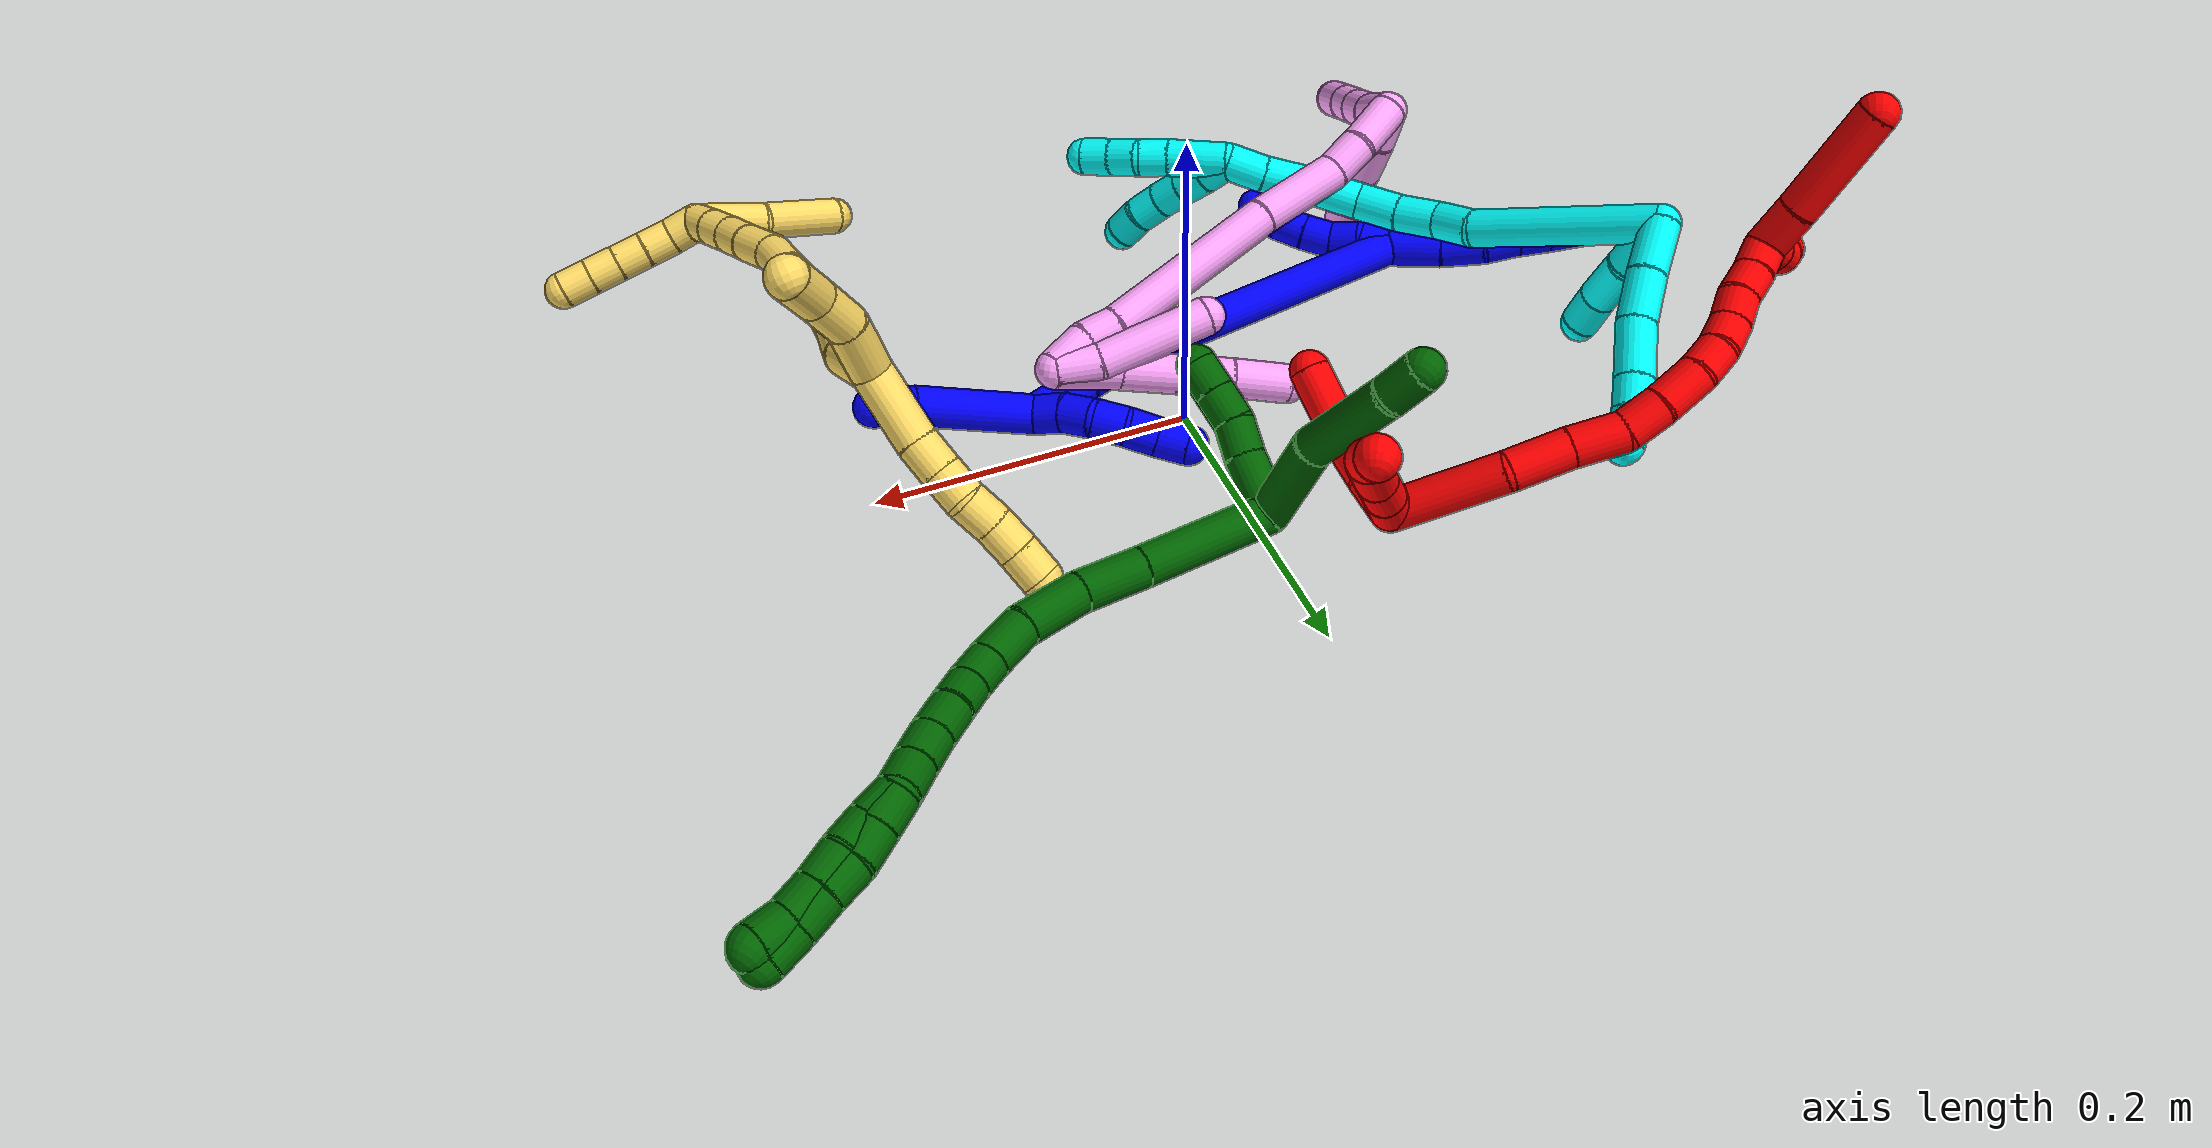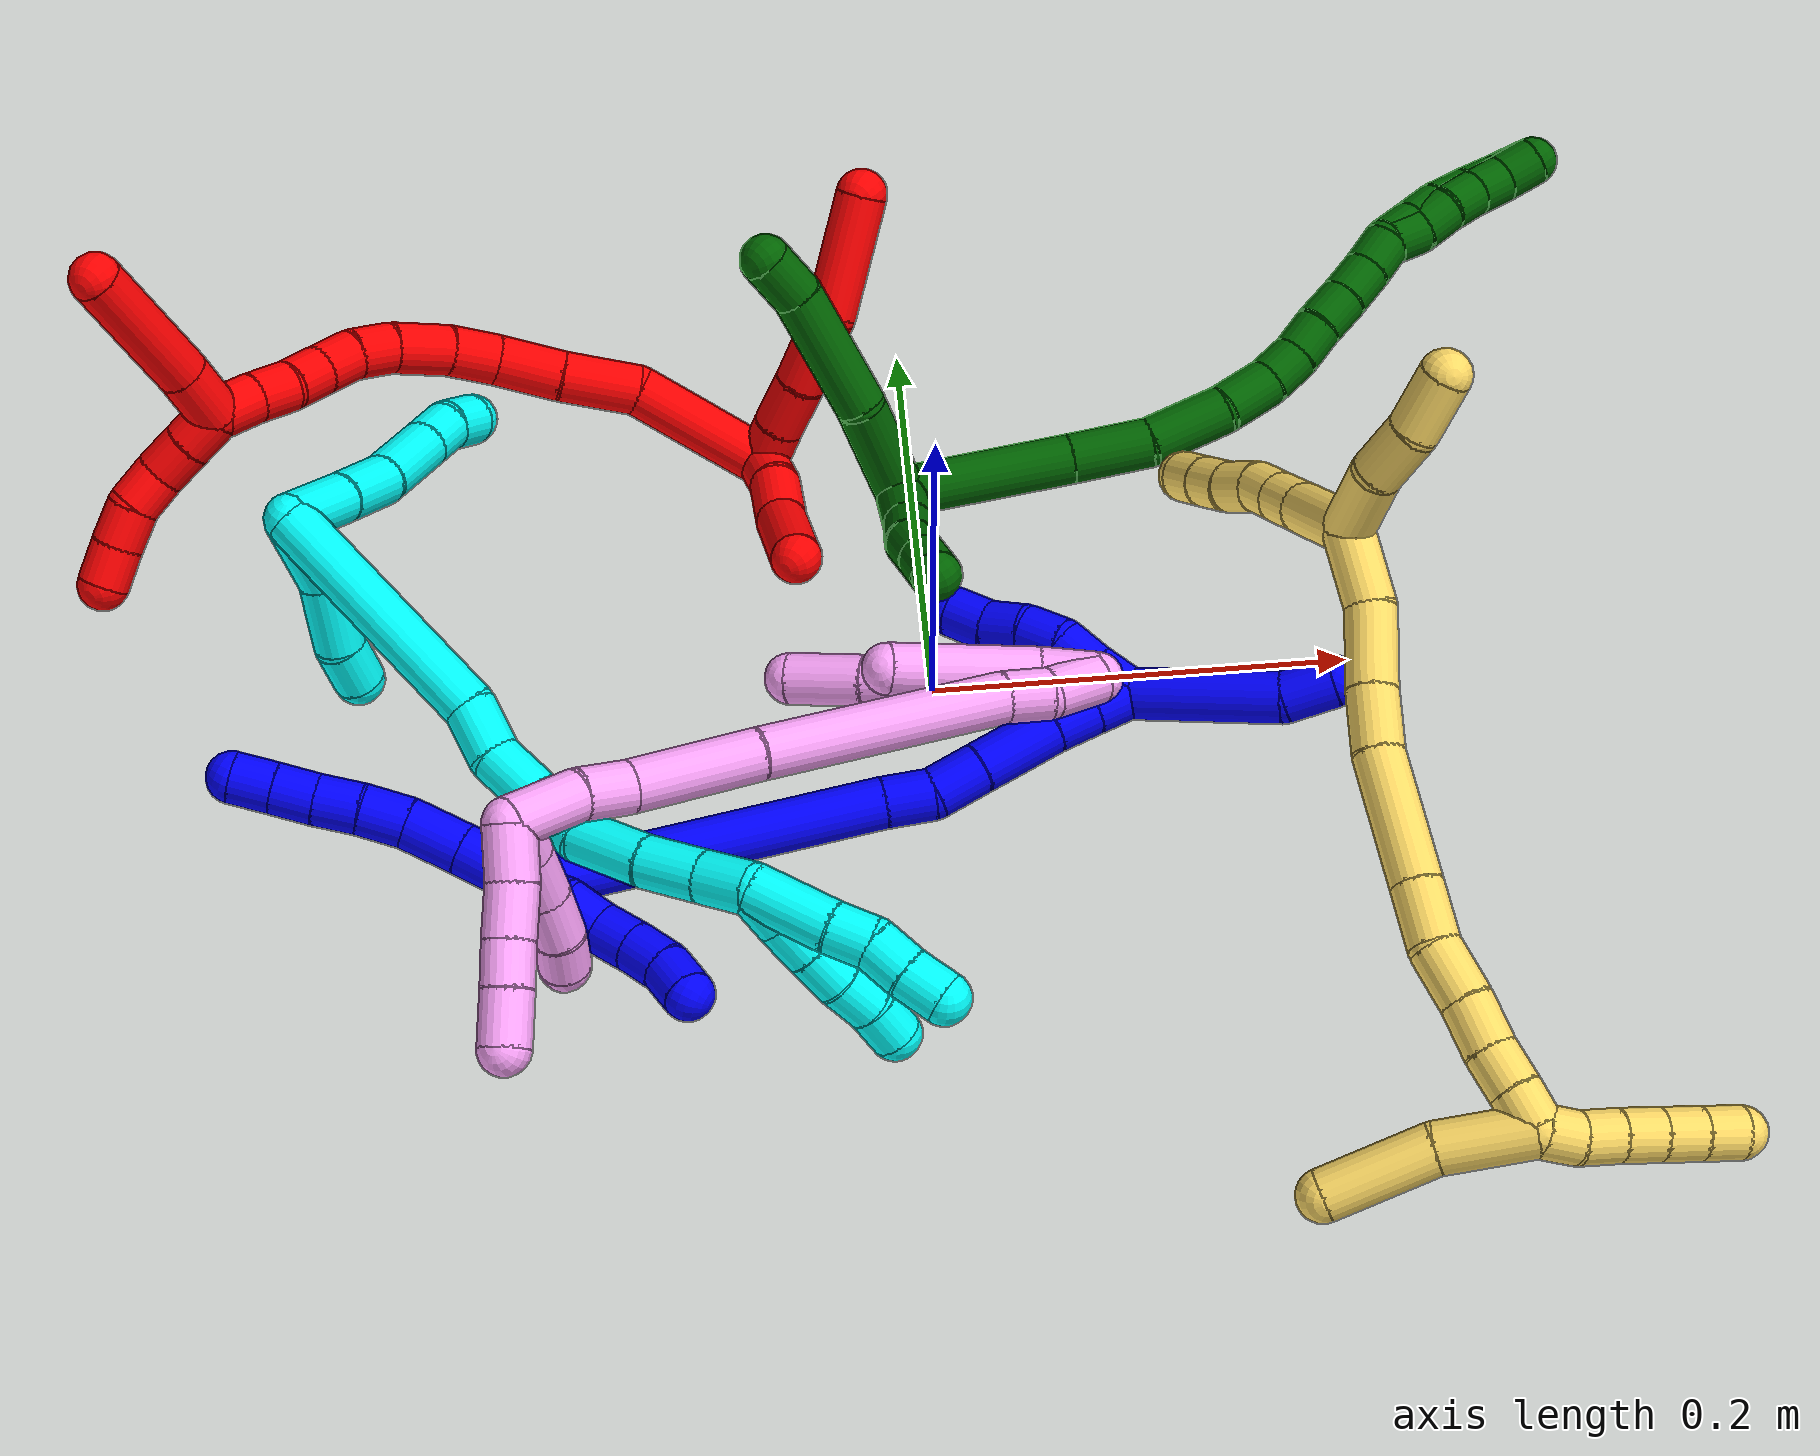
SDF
<sdf version="1.7">
 <world name="default">
  <plugin name="TubeGeneratorPlugin" filename="libtube_generator_plugin.so"/>
  <model name="photoneo_s_sensor">
   <static>1</static>
   <pose>0 0 2 1.57079 1.57079 3.14159</pose>
   <link name="link">
    <inertial><mass>0.1</mass></inertial>
    <sensor name="sensor" type="depth">
     <update_rate>30</update_rate>
     <camera>
      <horizontal_fov>1.22</horizontal_fov>
      <image><width>1920</width><height>1200</height><format>B8G8R8</format></image>
      <clip><near>0.1</near><far>4</far></clip>
      <depth_camera><output>points</output></depth_camera>
     </camera>
     <plugin name="camera_plugin" filename="libgazebo_ros_depth_camera.so">
      <baseline>0.2</baseline>
      <alwaysOn>1</alwaysOn>
      <updateRate>0.0</updateRate>
      <cameraName>camera_ir</cameraName>
      <imageTopicName>/camera/color/image_raw</imageTopicName>
      <cameraInfoTopicName>/camera/color/camera_info</cameraInfoTopicName>
      <depthImageTopicName>/camera/depth/image_raw</depthImageTopicName>
      <depthImageCameraInfoTopicName>/camera/depth/camera_info</depthImageCameraInfoTopicName>
      <pointCloudTopicName>/camera/depth/points</pointCloudTopicName>
      <frameName>fr_optical</frameName>
      <pointCloudCutoff>0.1</pointCloudCutoff>
      <pointCloudCutoffMax>2.0</pointCloudCutoffMax>
      <distortionK1>0</distortionK1>
      <distortionK2>0</distortionK2>
      <distortionK3>0</distortionK3>
      <distortionT1>0</distortionT1>
      <distortionT2>0</distortionT2>
      <CxPrime>0</CxPrime>
      <Cx>0</Cx>
      <Cy>0</Cy>
      <focalLength>0</focalLength>
      <hackBaseline>0</hackBaseline>
     </plugin>
    </sensor>
   </link>
  </model>
  <gravity>0 0 -9.8</gravity>
  <magnetic_field>6e-06 2.3e-05 -4.2e-05</magnetic_field>
  <atmosphere type="adiabatic"/>
  <physics name="default_physics" default="0" type="ode">
   <max_step_size>0.003</max_step_size>
   <real_time_factor>1</real_time_factor>
   <real_time_update_rate>1000</real_time_update_rate>
   <max_contacts>10000</max_contacts>
   <ode>
    <solver>
     <type>quick</type>
     <iters>100</iters>
     <sor>1.3</sor>
     <use_dynamic_moi_rescaling>0</use_dynamic_moi_rescaling>
    </solver>
    <constraints>
     <contact_max_correcting_vel>0</contact_max_correcting_vel>
     <contact_surface_layer>0.001</contact_surface_layer>
     <cfm>0</cfm>
     <erp>0.2</erp>
    </constraints>
   </ode>
  </physics>
  <scene><ambient>0.4 0.4 0.4 1</ambient><background>0.7 0.7 0.7 1</background><shadows>0</shadows></scene>
  <audio><device>default</device></audio>
  <spherical_coordinates>
   <surface_model>EARTH_WGS84</surface_model>
   <latitude_deg>0</latitude_deg>
   <longitude_deg>0</longitude_deg>
   <elevation>0</elevation>
   <heading_deg>0</heading_deg>
  </spherical_coordinates>
  <model name="bin">
   <static>1</static>
   <link name="bottom">
    <collision name="collision-bottom">
     <pose>0 0 -0.01 0 -0 0</pose>
     <geometry><box><size>0.8 0.6 0.02</size></box></geometry>
     <surface>
      <friction><ode><mu>100</mu><mu2>100</mu2></ode></friction>
      <contact><collide_bitmask>65535</collide_bitmask></contact>
     </surface>
    </collision>
   </link>
   <link name="west_wall">
    <collision name="collision-west_wall">
     <pose>-0.41 0 0.1 0 -0 0</pose>
     <geometry><box><size>0.02 0.6 0.2</size></box></geometry>
     <surface>
      <friction><ode><mu>100</mu><mu2>100</mu2></ode></friction>
      <contact><collide_bitmask>65535</collide_bitmask></contact>
     </surface>
    </collision>
   </link>
   <link name="east_wall">
    <collision name="collision-east_wall">
     <pose>0.41 0 0.1 0 -0 0</pose>
     <geometry><box><size>0.02 0.6 0.2</size></box></geometry>
     <surface>
      <friction><ode><mu>100</mu><mu2>100</mu2></ode></friction>
      <contact><collide_bitmask>65535</collide_bitmask></contact>
     </surface>
    </collision>
   </link>
   <link name="south_wall">
    <collision name="collision-south_wall">
     <pose>0 -0.31 0.1 0 -0 0</pose>
     <geometry><box><size>0.8 0.02 0.2</size></box></geometry>
     <surface>
      <friction><ode><mu>100</mu><mu2>100</mu2></ode></friction>
      <contact><collide_bitmask>65535</collide_bitmask></contact>
     </surface>
    </collision>
   </link>
   <link name="north_wall">
    <collision name="collision-north_wall">
     <pose>0 0.31 0.1 0 -0 0</pose>
     <geometry><box><size>0.8 0.02 0.2</size></box></geometry>
     <surface>
      <friction><ode><mu>100</mu><mu2>100</mu2></ode></friction>
      <contact><collide_bitmask>65535</collide_bitmask></contact>
     </surface>
    </collision>
   </link>
  </model>
  <model name="1">
   <static>0</static>
   <link name="1">
    <collision name="collision-cylinder-e_1_2_8">
     <pose>3e-05 -3.6e-05 0.018359 0.001963 0.001641 2e-06</pose>
     <geometry><cylinder><radius>0.0125</radius><length>0.036718</length></cylinder></geometry>
     <surface>
      <friction><ode><mu>1.16</mu><mu2>1.16</mu2><slip1>0</slip1><slip2>0</slip2></ode></friction>
      <contact><ode><kp>1e+06</kp><kd>1</kd><max_vel>0</max_vel><min_depth>0.001</min_depth></ode></contact>
     </surface>
    </collision>
    <visual name="visual-cylinder-e_1_2_8">
     <pose>3e-05 -3.6e-05 0.018359 0.001963 0.001641 2e-06</pose>
     <geometry><cylinder><radius>0.0125</radius><length>0.036718</length></cylinder></geometry>
     <material><ambient>0 0 1 1</ambient></material>
    </visual>
    <collision name="collision-cylinder-e_2_8_9">
     <pose>0.000289 -0.001512 0.051095 0.099801 0.015853 0.000792</pose>
     <geometry><cylinder><radius>0.0125</radius><length>0.028903</length></cylinder></geometry>
     <surface>
      <friction><ode><mu>1.16</mu><mu2>1.16</mu2><slip1>0</slip1><slip2>0</slip2></ode></friction>
      <contact><ode><kp>1e+06</kp><kd>1</kd><max_vel>0</max_vel><min_depth>0.001</min_depth></ode></contact>
     </surface>
    </collision>
    <visual name="visual-cylinder-e_2_8_9">
     <pose>0.000289 -0.001512 0.051095 0.099801 0.015853 0.000792</pose>
     <geometry><cylinder><radius>0.0125</radius><length>0.028903</length></cylinder></geometry>
     <material><ambient>0 0 1 1</ambient></material>
    </visual>
    <collision name="collision-cylinder-e_3_9_10">
     <pose>-0.000356 -0.005992 0.076378 0.271946 -0.077096 -0.010553</pose>
     <geometry><cylinder><radius>0.0125</radius><length>0.022709</length></cylinder></geometry>
     <surface>
      <friction><ode><mu>1.16</mu><mu2>1.16</mu2><slip1>0</slip1><slip2>0</slip2></ode></friction>
      <contact><ode><kp>1e+06</kp><kd>1</kd><max_vel>0</max_vel><min_depth>0.001</min_depth></ode></contact>
     </surface>
    </collision>
    <visual name="visual-cylinder-e_3_9_10">
     <pose>-0.000356 -0.005992 0.076378 0.271946 -0.077096 -0.010553</pose>
     <geometry><cylinder><radius>0.0125</radius><length>0.022709</length></cylinder></geometry>
     <material><ambient>0 0 1 1</ambient></material>
    </visual>
    <collision name="collision-cylinder-e_4_10_11">
     <pose>-0.003152 -0.011409 0.097521 0.228044 -0.180839 -0.020765</pose>
     <geometry><cylinder><radius>0.0125</radius><length>0.02137</length></cylinder></geometry>
     <surface>
      <friction><ode><mu>1.16</mu><mu2>1.16</mu2><slip1>0</slip1><slip2>0</slip2></ode></friction>
      <contact><ode><kp>1e+06</kp><kd>1</kd><max_vel>0</max_vel><min_depth>0.001</min_depth></ode></contact>
     </surface>
    </collision>
    <visual name="visual-cylinder-e_4_10_11">
     <pose>-0.003152 -0.011409 0.097521 0.228044 -0.180839 -0.020765</pose>
     <geometry><cylinder><radius>0.0125</radius><length>0.02137</length></cylinder></geometry>
     <material><ambient>0 0 1 1</ambient></material>
    </visual>
    <collision name="collision-cylinder-e_5_11_12">
     <pose>-0.00626 -0.016148 0.117515 0.237602 -0.117623 -0.014056</pose>
     <geometry><cylinder><radius>0.0125</radius><length>0.020213</length></cylinder></geometry>
     <surface>
      <friction><ode><mu>1.16</mu><mu2>1.16</mu2><slip1>0</slip1><slip2>0</slip2></ode></friction>
      <contact><ode><kp>1e+06</kp><kd>1</kd><max_vel>0</max_vel><min_depth>0.001</min_depth></ode></contact>
     </surface>
    </collision>
    <visual name="visual-cylinder-e_5_11_12">
     <pose>-0.00626 -0.016148 0.117515 0.237602 -0.117623 -0.014056</pose>
     <geometry><cylinder><radius>0.0125</radius><length>0.020213</length></cylinder></geometry>
     <material><ambient>0 0 1 1</ambient></material>
    </visual>
    <collision name="collision-cylinder-e_6_12_6">
     <pose>-0.008784 -0.020814 0.136953 0.233504 -0.133547 -0.015686</pose>
     <geometry><cylinder><radius>0.0125</radius><length>0.020087</length></cylinder></geometry>
     <surface>
      <friction><ode><mu>1.16</mu><mu2>1.16</mu2><slip1>0</slip1><slip2>0</slip2></ode></friction>
      <contact><ode><kp>1e+06</kp><kd>1</kd><max_vel>0</max_vel><min_depth>0.001</min_depth></ode></contact>
     </surface>
    </collision>
    <visual name="visual-cylinder-e_6_12_6">
     <pose>-0.008784 -0.020814 0.136953 0.233504 -0.133547 -0.015686</pose>
     <geometry><cylinder><radius>0.0125</radius><length>0.020087</length></cylinder></geometry>
     <material><ambient>0 0 1 1</ambient></material>
    </visual>
    <collision name="collision-cylinder-e_1_2_13">
     <pose>0.000846 -0.002404 -0.00967 2.89791 0.084709 0.66641</pose>
     <geometry><cylinder><radius>0.0125</radius><length>0.02</length></cylinder></geometry>
     <surface>
      <friction><ode><mu>1.16</mu><mu2>1.16</mu2><slip1>0</slip1><slip2>0</slip2></ode></friction>
      <contact><ode><kp>1e+06</kp><kd>1</kd><max_vel>0</max_vel><min_depth>0.001</min_depth></ode></contact>
     </surface>
    </collision>
    <visual name="visual-cylinder-e_1_2_13">
     <pose>0.000846 -0.002404 -0.00967 2.89791 0.084709 0.66641</pose>
     <geometry><cylinder><radius>0.0125</radius><length>0.02</length></cylinder></geometry>
     <material><ambient>0 0 1 1</ambient></material>
    </visual>
    <collision name="collision-cylinder-e_2_13_14">
     <pose>0.000185 -0.004862 -0.029225 3.13619 -0.151336 -3.07038</pose>
     <geometry><cylinder><radius>0.0125</radius><length>0.02</length></cylinder></geometry>
     <surface>
      <friction><ode><mu>1.16</mu><mu2>1.16</mu2><slip1>0</slip1><slip2>0</slip2></ode></friction>
      <contact><ode><kp>1e+06</kp><kd>1</kd><max_vel>0</max_vel><min_depth>0.001</min_depth></ode></contact>
     </surface>
    </collision>
    <visual name="visual-cylinder-e_2_13_14">
     <pose>0.000185 -0.004862 -0.029225 3.13619 -0.151336 -3.07038</pose>
     <geometry><cylinder><radius>0.0125</radius><length>0.02</length></cylinder></geometry>
     <material><ambient>0 0 1 1</ambient></material>
    </visual>
    <collision name="collision-cylinder-e_3_14_15">
     <pose>-0.000541 -0.007361 -0.048775 2.89375 0.078241 0.608916</pose>
     <geometry><cylinder><radius>0.0125</radius><length>0.02</length></cylinder></geometry>
     <surface>
      <friction><ode><mu>1.16</mu><mu2>1.16</mu2><slip1>0</slip1><slip2>0</slip2></ode></friction>
      <contact><ode><kp>1e+06</kp><kd>1</kd><max_vel>0</max_vel><min_depth>0.001</min_depth></ode></contact>
     </surface>
    </collision>
    <visual name="visual-cylinder-e_3_14_15">
     <pose>-0.000541 -0.007361 -0.048775 2.89375 0.078241 0.608916</pose>
     <geometry><cylinder><radius>0.0125</radius><length>0.02</length></cylinder></geometry>
     <material><ambient>0 0 1 1</ambient></material>
    </visual>
    <collision name="collision-cylinder-e_4_15_16">
     <pose>0.000851 -0.013107 -0.06786 2.8046 0.061073 0.355349</pose>
     <geometry><cylinder><radius>0.0125</radius><length>0.02</length></cylinder></geometry>
     <surface>
      <friction><ode><mu>1.16</mu><mu2>1.16</mu2><slip1>0</slip1><slip2>0</slip2></ode></friction>
      <contact><ode><kp>1e+06</kp><kd>1</kd><max_vel>0</max_vel><min_depth>0.001</min_depth></ode></contact>
     </surface>
    </collision>
    <visual name="visual-cylinder-e_4_15_16">
     <pose>0.000851 -0.013107 -0.06786 2.8046 0.061073 0.355349</pose>
     <geometry><cylinder><radius>0.0125</radius><length>0.02</length></cylinder></geometry>
     <material><ambient>0 0 1 1</ambient></material>
    </visual>
    <collision name="collision-cylinder-e_5_16_5">
     <pose>0.000591 -0.021902 -0.085589 2.55726 -0.087084 -0.287715</pose>
     <geometry><cylinder><radius>0.0125</radius><length>0.02</length></cylinder></geometry>
     <surface>
      <friction><ode><mu>1.16</mu><mu2>1.16</mu2><slip1>0</slip1><slip2>0</slip2></ode></friction>
      <contact><ode><kp>1e+06</kp><kd>1</kd><max_vel>0</max_vel><min_depth>0.001</min_depth></ode></contact>
     </surface>
    </collision>
    <visual name="visual-cylinder-e_5_16_5">
     <pose>0.000591 -0.021902 -0.085589 2.55726 -0.087084 -0.287715</pose>
     <geometry><cylinder><radius>0.0125</radius><length>0.02</length></cylinder></geometry>
     <material><ambient>0 0 1 1</ambient></material>
    </visual>
    <collision name="collision-cylinder-e_1_2_17">
     <pose>0.040876 0.04115 -0.061436 -2.55142 0.504985 -1.40759</pose>
     <geometry><cylinder><radius>0.0125</radius><length>0.16898</length></cylinder></geometry>
     <surface>
      <friction><ode><mu>1.16</mu><mu2>1.16</mu2><slip1>0</slip1><slip2>0</slip2></ode></friction>
      <contact><ode><kp>1e+06</kp><kd>1</kd><max_vel>0</max_vel><min_depth>0.001</min_depth></ode></contact>
     </surface>
    </collision>
    <visual name="visual-cylinder-e_1_2_17">
     <pose>0.040876 0.04115 -0.061436 -2.55142 0.504985 -1.40759</pose>
     <geometry><cylinder><radius>0.0125</radius><length>0.16898</length></cylinder></geometry>
     <material><ambient>0 0 1 1</ambient></material>
    </visual>
    <collision name="collision-cylinder-e_2_17_18">
     <pose>0.087232 0.087373 -0.132036 -2.636 0.482106 -1.52127</pose>
     <geometry><cylinder><radius>0.0125</radius><length>0.023643</length></cylinder></geometry>
     <surface>
      <friction><ode><mu>1.16</mu><mu2>1.16</mu2><slip1>0</slip1><slip2>0</slip2></ode></friction>
      <contact><ode><kp>1e+06</kp><kd>1</kd><max_vel>0</max_vel><min_depth>0.001</min_depth></ode></contact>
     </surface>
    </collision>
    <visual name="visual-cylinder-e_2_17_18">
     <pose>0.087232 0.087373 -0.132036 -2.636 0.482106 -1.52127</pose>
     <geometry><cylinder><radius>0.0125</radius><length>0.023643</length></cylinder></geometry>
     <material><ambient>0 0 1 1</ambient></material>
    </visual>
    <collision name="collision-cylinder-e_3_18_19">
     <pose>0.100964 0.099544 -0.147731 -2.31466 0.707591 -1.3994</pose>
     <geometry><cylinder><radius>0.0125</radius><length>0.025386</length></cylinder></geometry>
     <surface>
      <friction><ode><mu>1.16</mu><mu2>1.16</mu2><slip1>0</slip1><slip2>0</slip2></ode></friction>
      <contact><ode><kp>1e+06</kp><kd>1</kd><max_vel>0</max_vel><min_depth>0.001</min_depth></ode></contact>
     </surface>
    </collision>
    <visual name="visual-cylinder-e_3_18_19">
     <pose>0.100964 0.099544 -0.147731 -2.31466 0.707591 -1.3994</pose>
     <geometry><cylinder><radius>0.0125</radius><length>0.025386</length></cylinder></geometry>
     <material><ambient>0 0 1 1</ambient></material>
    </visual>
    <collision name="collision-cylinder-e_4_19_20">
     <pose>0.121961 0.118357 -0.164597 -2.29366 0.684372 -1.33625</pose>
     <geometry><cylinder><radius>0.0125</radius><length>0.040325</length></cylinder></geometry>
     <surface>
      <friction><ode><mu>1.16</mu><mu2>1.16</mu2><slip1>0</slip1><slip2>0</slip2></ode></friction>
      <contact><ode><kp>1e+06</kp><kd>1</kd><max_vel>0</max_vel><min_depth>0.001</min_depth></ode></contact>
     </surface>
    </collision>
    <visual name="visual-cylinder-e_4_19_20">
     <pose>0.121961 0.118357 -0.164597 -2.29366 0.684372 -1.33625</pose>
     <geometry><cylinder><radius>0.0125</radius><length>0.040325</length></cylinder></geometry>
     <material><ambient>0 0 1 1</ambient></material>
    </visual>
    <collision name="collision-cylinder-e_5_20_21">
     <pose>0.140854 0.136486 -0.180933 -2.32293 0.610625 -1.25654</pose>
     <geometry><cylinder><radius>0.0125</radius><length>0.02144</length></cylinder></geometry>
     <surface>
      <friction><ode><mu>1.16</mu><mu2>1.16</mu2><slip1>0</slip1><slip2>0</slip2></ode></friction>
      <contact><ode><kp>1e+06</kp><kd>1</kd><max_vel>0</max_vel><min_depth>0.001</min_depth></ode></contact>
     </surface>
    </collision>
    <visual name="visual-cylinder-e_5_20_21">
     <pose>0.140854 0.136486 -0.180933 -2.32293 0.610625 -1.25654</pose>
     <geometry><cylinder><radius>0.0125</radius><length>0.02144</length></cylinder></geometry>
     <material><ambient>0 0 1 1</ambient></material>
    </visual>
    <collision name="collision-cylinder-e_6_21_1">
     <pose>0.15284 0.148803 -0.192705 -2.34495 0.615566 -1.2939</pose>
     <geometry><cylinder><radius>0.0125</radius><length>0.020226</length></cylinder></geometry>
     <surface>
      <friction><ode><mu>1.16</mu><mu2>1.16</mu2><slip1>0</slip1><slip2>0</slip2></ode></friction>
      <contact><ode><kp>1e+06</kp><kd>1</kd><max_vel>0</max_vel><min_depth>0.001</min_depth></ode></contact>
     </surface>
    </collision>
    <visual name="visual-cylinder-e_6_21_1">
     <pose>0.15284 0.148803 -0.192705 -2.34495 0.615566 -1.2939</pose>
     <geometry><cylinder><radius>0.0125</radius><length>0.020226</length></cylinder></geometry>
     <material><ambient>0 0 1 1</ambient></material>
    </visual>
    <collision name="collision-cylinder-e_1_1_22">
     <pose>0.174164 0.15632 -0.232429 -3.09411 0.427464 -2.92364</pose>
     <geometry><cylinder><radius>0.0125</radius><length>0.0747</length></cylinder></geometry>
     <surface>
      <friction><ode><mu>1.16</mu><mu2>1.16</mu2><slip1>0</slip1><slip2>0</slip2></ode></friction>
      <contact><ode><kp>1e+06</kp><kd>1</kd><max_vel>0</max_vel><min_depth>0.001</min_depth></ode></contact>
     </surface>
    </collision>
    <visual name="visual-cylinder-e_1_1_22">
     <pose>0.174164 0.15632 -0.232429 -3.09411 0.427464 -2.92364</pose>
     <geometry><cylinder><radius>0.0125</radius><length>0.0747</length></cylinder></geometry>
     <material><ambient>0 0 1 1</ambient></material>
    </visual>
    <collision name="collision-cylinder-e_2_22_4">
     <pose>0.198006 0.160412 -0.275546 -2.87747 0.721824 -2.4648</pose>
     <geometry><cylinder><radius>0.0125</radius><length>0.0253</length></cylinder></geometry>
     <surface>
      <friction><ode><mu>1.16</mu><mu2>1.16</mu2><slip1>0</slip1><slip2>0</slip2></ode></friction>
      <contact><ode><kp>1e+06</kp><kd>1</kd><max_vel>0</max_vel><min_depth>0.001</min_depth></ode></contact>
     </surface>
    </collision>
    <visual name="visual-cylinder-e_2_22_4">
     <pose>0.198006 0.160412 -0.275546 -2.87747 0.721824 -2.4648</pose>
     <geometry><cylinder><radius>0.0125</radius><length>0.0253</length></cylinder></geometry>
     <material><ambient>0 0 1 1</ambient></material>
    </visual>
    <collision name="collision-cylinder-e_1_1_23">
     <pose>0.160434 0.154211 -0.188645 0.050345 0.176321 0.004451</pose>
     <geometry><cylinder><radius>0.0125</radius><length>0.02</length></cylinder></geometry>
     <surface>
      <friction><ode><mu>1.16</mu><mu2>1.16</mu2><slip1>0</slip1><slip2>0</slip2></ode></friction>
      <contact><ode><kp>1e+06</kp><kd>1</kd><max_vel>0</max_vel><min_depth>0.001</min_depth></ode></contact>
     </surface>
    </collision>
    <visual name="visual-cylinder-e_1_1_23">
     <pose>0.160434 0.154211 -0.188645 0.050345 0.176321 0.004451</pose>
     <geometry><cylinder><radius>0.0125</radius><length>0.02</length></cylinder></geometry>
     <material><ambient>0 0 1 1</ambient></material>
    </visual>
    <collision name="collision-cylinder-e_2_23_24">
     <pose>0.163986 0.155315 -0.169107 -0.163346 0.180822 -0.014841</pose>
     <geometry><cylinder><radius>0.0125</radius><length>0.02</length></cylinder></geometry>
     <surface>
      <friction><ode><mu>1.16</mu><mu2>1.16</mu2><slip1>0</slip1><slip2>0</slip2></ode></friction>
      <contact><ode><kp>1e+06</kp><kd>1</kd><max_vel>0</max_vel><min_depth>0.001</min_depth></ode></contact>
     </surface>
    </collision>
    <visual name="visual-cylinder-e_2_23_24">
     <pose>0.163986 0.155315 -0.169107 -0.163346 0.180822 -0.014841</pose>
     <geometry><cylinder><radius>0.0125</radius><length>0.02</length></cylinder></geometry>
     <material><ambient>0 0 1 1</ambient></material>
    </visual>
    <collision name="collision-cylinder-e_3_24_25">
     <pose>0.164199 0.158746 -0.149698 -0.186524 -0.159205 0.014922</pose>
     <geometry><cylinder><radius>0.0125</radius><length>0.02</length></cylinder></geometry>
     <surface>
      <friction><ode><mu>1.16</mu><mu2>1.16</mu2><slip1>0</slip1><slip2>0</slip2></ode></friction>
      <contact><ode><kp>1e+06</kp><kd>1</kd><max_vel>0</max_vel><min_depth>0.001</min_depth></ode></contact>
     </surface>
    </collision>
    <visual name="visual-cylinder-e_3_24_25">
     <pose>0.164199 0.158746 -0.149698 -0.186524 -0.159205 0.014922</pose>
     <geometry><cylinder><radius>0.0125</radius><length>0.02</length></cylinder></geometry>
     <material><ambient>0 0 1 1</ambient></material>
    </visual>
    <collision name="collision-cylinder-e_4_25_26">
     <pose>0.158652 0.162586 -0.131037 -0.220578 -0.40733 0.045733</pose>
     <geometry><cylinder><radius>0.0125</radius><length>0.02</length></cylinder></geometry>
     <surface>
      <friction><ode><mu>1.16</mu><mu2>1.16</mu2><slip1>0</slip1><slip2>0</slip2></ode></friction>
      <contact><ode><kp>1e+06</kp><kd>1</kd><max_vel>0</max_vel><min_depth>0.001</min_depth></ode></contact>
     </surface>
    </collision>
    <visual name="visual-cylinder-e_4_25_26">
     <pose>0.158652 0.162586 -0.131037 -0.220578 -0.40733 0.045733</pose>
     <geometry><cylinder><radius>0.0125</radius><length>0.02</length></cylinder></geometry>
     <material><ambient>0 0 1 1</ambient></material>
    </visual>
    <collision name="collision-cylinder-e_5_26_3">
     <pose>0.153315 0.166561 -0.11237 -0.199793 -0.138057 0.013859</pose>
     <geometry><cylinder><radius>0.0125</radius><length>0.02</length></cylinder></geometry>
     <surface>
      <friction><ode><mu>1.16</mu><mu2>1.16</mu2><slip1>0</slip1><slip2>0</slip2></ode></friction>
      <contact><ode><kp>1e+06</kp><kd>1</kd><max_vel>0</max_vel><min_depth>0.001</min_depth></ode></contact>
     </surface>
    </collision>
    <visual name="visual-cylinder-e_5_26_3">
     <pose>0.153315 0.166561 -0.11237 -0.199793 -0.138057 0.013859</pose>
     <geometry><cylinder><radius>0.0125</radius><length>0.02</length></cylinder></geometry>
     <material><ambient>0 0 1 1</ambient></material>
    </visual>
    <collision name="collision-sphere-3">
     <pose>0.151938 0.168526 -0.102662 0 -0 0</pose>
     <geometry><sphere><radius>0.0125</radius></sphere></geometry>
     <surface>
      <friction><ode><mu>1.16</mu><mu2>1.16</mu2><slip1>0</slip1><slip2>0</slip2></ode></friction>
      <contact><ode><kp>1e+06</kp><kd>1</kd><max_vel>0</max_vel><min_depth>0.001</min_depth></ode></contact>
     </surface>
    </collision>
    <visual name="visual-sphere-3">
     <pose>0.151938 0.168526 -0.102662 0 -0 0</pose>
     <geometry><sphere><radius>0.0125</radius></sphere></geometry>
     <material><ambient>0 0 1 1</ambient></material>
    </visual>
    <collision name="collision-sphere-26">
     <pose>0.154691 0.164595 -0.122077 0 -0 0</pose>
     <geometry><sphere><radius>0.0125</radius></sphere></geometry>
     <surface>
      <friction><ode><mu>1.16</mu><mu2>1.16</mu2><slip1>0</slip1><slip2>0</slip2></ode></friction>
      <contact><ode><kp>1e+06</kp><kd>1</kd><max_vel>0</max_vel><min_depth>0.001</min_depth></ode></contact>
     </surface>
    </collision>
    <visual name="visual-sphere-26">
     <pose>0.154691 0.164595 -0.122077 0 -0 0</pose>
     <geometry><sphere><radius>0.0125</radius></sphere></geometry>
     <material><ambient>0 0 1 1</ambient></material>
    </visual>
    <collision name="collision-sphere-25">
     <pose>0.162614 0.160577 -0.139996 0 -0 0</pose>
     <geometry><sphere><radius>0.0125</radius></sphere></geometry>
     <surface>
      <friction><ode><mu>1.16</mu><mu2>1.16</mu2><slip1>0</slip1><slip2>0</slip2></ode></friction>
      <contact><ode><kp>1e+06</kp><kd>1</kd><max_vel>0</max_vel><min_depth>0.001</min_depth></ode></contact>
     </surface>
    </collision>
    <visual name="visual-sphere-25">
     <pose>0.162614 0.160577 -0.139996 0 -0 0</pose>
     <geometry><sphere><radius>0.0125</radius></sphere></geometry>
     <material><ambient>0 0 1 1</ambient></material>
    </visual>
    <collision name="collision-sphere-24">
     <pose>0.165785 0.156915 -0.159401 0 -0 0</pose>
     <geometry><sphere><radius>0.0125</radius></sphere></geometry>
     <surface>
      <friction><ode><mu>1.16</mu><mu2>1.16</mu2><slip1>0</slip1><slip2>0</slip2></ode></friction>
      <contact><ode><kp>1e+06</kp><kd>1</kd><max_vel>0</max_vel><min_depth>0.001</min_depth></ode></contact>
     </surface>
    </collision>
    <visual name="visual-sphere-24">
     <pose>0.165785 0.156915 -0.159401 0 -0 0</pose>
     <geometry><sphere><radius>0.0125</radius></sphere></geometry>
     <material><ambient>0 0 1 1</ambient></material>
    </visual>
    <collision name="collision-sphere-23">
     <pose>0.162188 0.153716 -0.178813 0 -0 0</pose>
     <geometry><sphere><radius>0.0125</radius></sphere></geometry>
     <surface>
      <friction><ode><mu>1.16</mu><mu2>1.16</mu2><slip1>0</slip1><slip2>0</slip2></ode></friction>
      <contact><ode><kp>1e+06</kp><kd>1</kd><max_vel>0</max_vel><min_depth>0.001</min_depth></ode></contact>
     </surface>
    </collision>
    <visual name="visual-sphere-23">
     <pose>0.162188 0.153716 -0.178813 0 -0 0</pose>
     <geometry><sphere><radius>0.0125</radius></sphere></geometry>
     <material><ambient>0 0 1 1</ambient></material>
    </visual>
    <collision name="collision-sphere-4">
     <pose>0.206365 0.162891 -0.284711 0 -0 0</pose>
     <geometry><sphere><radius>0.0125</radius></sphere></geometry>
     <surface>
      <friction><ode><mu>1.16</mu><mu2>1.16</mu2><slip1>0</slip1><slip2>0</slip2></ode></friction>
      <contact><ode><kp>1e+06</kp><kd>1</kd><max_vel>0</max_vel><min_depth>0.001</min_depth></ode></contact>
     </surface>
    </collision>
    <visual name="visual-sphere-4">
     <pose>0.206365 0.162891 -0.284711 0 -0 0</pose>
     <geometry><sphere><radius>0.0125</radius></sphere></geometry>
     <material><ambient>0 0 1 1</ambient></material>
    </visual>
    <collision name="collision-sphere-22">
     <pose>0.189648 0.157933 -0.26638 0 -0 0</pose>
     <geometry><sphere><radius>0.0125</radius></sphere></geometry>
     <surface>
      <friction><ode><mu>1.16</mu><mu2>1.16</mu2><slip1>0</slip1><slip2>0</slip2></ode></friction>
      <contact><ode><kp>1e+06</kp><kd>1</kd><max_vel>0</max_vel><min_depth>0.001</min_depth></ode></contact>
     </surface>
    </collision>
    <visual name="visual-sphere-22">
     <pose>0.189648 0.157933 -0.26638 0 -0 0</pose>
     <geometry><sphere><radius>0.0125</radius></sphere></geometry>
     <material><ambient>0 0 1 1</ambient></material>
    </visual>
    <collision name="collision-sphere-1">
     <pose>0.15868 0.154707 -0.198478 0 -0 0</pose>
     <geometry><sphere><radius>0.0125</radius></sphere></geometry>
     <surface>
      <friction><ode><mu>1.16</mu><mu2>1.16</mu2><slip1>0</slip1><slip2>0</slip2></ode></friction>
      <contact><ode><kp>1e+06</kp><kd>1</kd><max_vel>0</max_vel><min_depth>0.001</min_depth></ode></contact>
     </surface>
    </collision>
    <visual name="visual-sphere-1">
     <pose>0.15868 0.154707 -0.198478 0 -0 0</pose>
     <geometry><sphere><radius>0.0125</radius></sphere></geometry>
     <material><ambient>0 0 1 1</ambient></material>
    </visual>
    <collision name="collision-sphere-21">
     <pose>0.147001 0.142899 -0.186933 0 -0 0</pose>
     <geometry><sphere><radius>0.0125</radius></sphere></geometry>
     <surface>
      <friction><ode><mu>1.16</mu><mu2>1.16</mu2><slip1>0</slip1><slip2>0</slip2></ode></friction>
      <contact><ode><kp>1e+06</kp><kd>1</kd><max_vel>0</max_vel><min_depth>0.001</min_depth></ode></contact>
     </surface>
    </collision>
    <visual name="visual-sphere-21">
     <pose>0.147001 0.142899 -0.186933 0 -0 0</pose>
     <geometry><sphere><radius>0.0125</radius></sphere></geometry>
     <material><ambient>0 0 1 1</ambient></material>
    </visual>
    <collision name="collision-sphere-12">
     <pose>-0.007446 -0.01851 0.127269 0 -0 0</pose>
     <geometry><sphere><radius>0.0125</radius></sphere></geometry>
     <surface>
      <friction><ode><mu>1.16</mu><mu2>1.16</mu2><slip1>0</slip1><slip2>0</slip2></ode></friction>
      <contact><ode><kp>1e+06</kp><kd>1</kd><max_vel>0</max_vel><min_depth>0.001</min_depth></ode></contact>
     </surface>
    </collision>
    <visual name="visual-sphere-12">
     <pose>-0.007446 -0.01851 0.127269 0 -0 0</pose>
     <geometry><sphere><radius>0.0125</radius></sphere></geometry>
     <material><ambient>0 0 1 1</ambient></material>
    </visual>
    <collision name="collision-sphere-11">
     <pose>-0.005074 -0.013786 0.10776 0 -0 0</pose>
     <geometry><sphere><radius>0.0125</radius></sphere></geometry>
     <surface>
      <friction><ode><mu>1.16</mu><mu2>1.16</mu2><slip1>0</slip1><slip2>0</slip2></ode></friction>
      <contact><ode><kp>1e+06</kp><kd>1</kd><max_vel>0</max_vel><min_depth>0.001</min_depth></ode></contact>
     </surface>
    </collision>
    <visual name="visual-sphere-11">
     <pose>-0.005074 -0.013786 0.10776 0 -0 0</pose>
     <geometry><sphere><radius>0.0125</radius></sphere></geometry>
     <material><ambient>0 0 1 1</ambient></material>
    </visual>
    <collision name="collision-sphere-10">
     <pose>-0.001231 -0.009033 0.087282 0 -0 0</pose>
     <geometry><sphere><radius>0.0125</radius></sphere></geometry>
     <surface>
      <friction><ode><mu>1.16</mu><mu2>1.16</mu2><slip1>0</slip1><slip2>0</slip2></ode></friction>
      <contact><ode><kp>1e+06</kp><kd>1</kd><max_vel>0</max_vel><min_depth>0.001</min_depth></ode></contact>
     </surface>
    </collision>
    <visual name="visual-sphere-10">
     <pose>-0.001231 -0.009033 0.087282 0 -0 0</pose>
     <geometry><sphere><radius>0.0125</radius></sphere></geometry>
     <material><ambient>0 0 1 1</ambient></material>
    </visual>
    <collision name="collision-sphere-9">
     <pose>0.000518 -0.002951 0.065473 0 -0 0</pose>
     <geometry><sphere><radius>0.0125</radius></sphere></geometry>
     <surface>
      <friction><ode><mu>1.16</mu><mu2>1.16</mu2><slip1>0</slip1><slip2>0</slip2></ode></friction>
      <contact><ode><kp>1e+06</kp><kd>1</kd><max_vel>0</max_vel><min_depth>0.001</min_depth></ode></contact>
     </surface>
    </collision>
    <visual name="visual-sphere-9">
     <pose>0.000518 -0.002951 0.065473 0 -0 0</pose>
     <geometry><sphere><radius>0.0125</radius></sphere></geometry>
     <material><ambient>0 0 1 1</ambient></material>
    </visual>
    <collision name="collision-sphere-2">
     <geometry><sphere><radius>0.0125</radius></sphere></geometry>
     <surface>
      <friction><ode><mu>1.16</mu><mu2>1.16</mu2><slip1>0</slip1><slip2>0</slip2></ode></friction>
      <contact><ode><kp>1e+06</kp><kd>1</kd><max_vel>0</max_vel><min_depth>0.001</min_depth></ode></contact>
     </surface>
    </collision>
    <visual name="visual-sphere-2">
     <geometry><sphere><radius>0.0125</radius></sphere></geometry>
     <material><ambient>0 0 1 1</ambient></material>
    </visual>
    <collision name="collision-sphere-19">
     <pose>0.109215 0.106642 -0.154263 0 -0 0</pose>
     <geometry><sphere><radius>0.0125</radius></sphere></geometry>
     <surface>
      <friction><ode><mu>1.16</mu><mu2>1.16</mu2><slip1>0</slip1><slip2>0</slip2></ode></friction>
      <contact><ode><kp>1e+06</kp><kd>1</kd><max_vel>0</max_vel><min_depth>0.001</min_depth></ode></contact>
     </surface>
    </collision>
    <visual name="visual-sphere-19">
     <pose>0.109215 0.106642 -0.154263 0 -0 0</pose>
     <geometry><sphere><radius>0.0125</radius></sphere></geometry>
     <material><ambient>0 0 1 1</ambient></material>
    </visual>
    <collision name="collision-sphere-8">
     <pose>6e-05 -7.2e-05 0.036717 0 -0 0</pose>
     <geometry><sphere><radius>0.0125</radius></sphere></geometry>
     <surface>
      <friction><ode><mu>1.16</mu><mu2>1.16</mu2><slip1>0</slip1><slip2>0</slip2></ode></friction>
      <contact><ode><kp>1e+06</kp><kd>1</kd><max_vel>0</max_vel><min_depth>0.001</min_depth></ode></contact>
     </surface>
    </collision>
    <visual name="visual-sphere-8">
     <pose>6e-05 -7.2e-05 0.036717 0 -0 0</pose>
     <geometry><sphere><radius>0.0125</radius></sphere></geometry>
     <material><ambient>0 0 1 1</ambient></material>
    </visual>
    <collision name="collision-sphere-6">
     <pose>-0.010121 -0.023117 0.146637 0 -0 0</pose>
     <geometry><sphere><radius>0.0125</radius></sphere></geometry>
     <surface>
      <friction><ode><mu>1.16</mu><mu2>1.16</mu2><slip1>0</slip1><slip2>0</slip2></ode></friction>
      <contact><ode><kp>1e+06</kp><kd>1</kd><max_vel>0</max_vel><min_depth>0.001</min_depth></ode></contact>
     </surface>
    </collision>
    <visual name="visual-sphere-6">
     <pose>-0.010121 -0.023117 0.146637 0 -0 0</pose>
     <geometry><sphere><radius>0.0125</radius></sphere></geometry>
     <material><ambient>0 0 1 1</ambient></material>
    </visual>
    <collision name="collision-sphere-13">
     <pose>0.001692 -0.004808 -0.01934 0 -0 0</pose>
     <geometry><sphere><radius>0.0125</radius></sphere></geometry>
     <surface>
      <friction><ode><mu>1.16</mu><mu2>1.16</mu2><slip1>0</slip1><slip2>0</slip2></ode></friction>
      <contact><ode><kp>1e+06</kp><kd>1</kd><max_vel>0</max_vel><min_depth>0.001</min_depth></ode></contact>
     </surface>
    </collision>
    <visual name="visual-sphere-13">
     <pose>0.001692 -0.004808 -0.01934 0 -0 0</pose>
     <geometry><sphere><radius>0.0125</radius></sphere></geometry>
     <material><ambient>0 0 1 1</ambient></material>
    </visual>
    <collision name="collision-sphere-14">
     <pose>-0.001323 -0.004915 -0.039111 0 -0 0</pose>
     <geometry><sphere><radius>0.0125</radius></sphere></geometry>
     <surface>
      <friction><ode><mu>1.16</mu><mu2>1.16</mu2><slip1>0</slip1><slip2>0</slip2></ode></friction>
      <contact><ode><kp>1e+06</kp><kd>1</kd><max_vel>0</max_vel><min_depth>0.001</min_depth></ode></contact>
     </surface>
    </collision>
    <visual name="visual-sphere-14">
     <pose>-0.001323 -0.004915 -0.039111 0 -0 0</pose>
     <geometry><sphere><radius>0.0125</radius></sphere></geometry>
     <material><ambient>0 0 1 1</ambient></material>
    </visual>
    <collision name="collision-sphere-15">
     <pose>0.00024 -0.009806 -0.05844 0 -0 0</pose>
     <geometry><sphere><radius>0.0125</radius></sphere></geometry>
     <surface>
      <friction><ode><mu>1.16</mu><mu2>1.16</mu2><slip1>0</slip1><slip2>0</slip2></ode></friction>
      <contact><ode><kp>1e+06</kp><kd>1</kd><max_vel>0</max_vel><min_depth>0.001</min_depth></ode></contact>
     </surface>
    </collision>
    <visual name="visual-sphere-15">
     <pose>0.00024 -0.009806 -0.05844 0 -0 0</pose>
     <geometry><sphere><radius>0.0125</radius></sphere></geometry>
     <material><ambient>0 0 1 1</ambient></material>
    </visual>
    <collision name="collision-sphere-16">
     <pose>0.001461 -0.016407 -0.07728 0 -0 0</pose>
     <geometry><sphere><radius>0.0125</radius></sphere></geometry>
     <surface>
      <friction><ode><mu>1.16</mu><mu2>1.16</mu2><slip1>0</slip1><slip2>0</slip2></ode></friction>
      <contact><ode><kp>1e+06</kp><kd>1</kd><max_vel>0</max_vel><min_depth>0.001</min_depth></ode></contact>
     </surface>
    </collision>
    <visual name="visual-sphere-16">
     <pose>0.001461 -0.016407 -0.07728 0 -0 0</pose>
     <geometry><sphere><radius>0.0125</radius></sphere></geometry>
     <material><ambient>0 0 1 1</ambient></material>
    </visual>
    <collision name="collision-sphere-5">
     <pose>-0.000279 -0.027398 -0.093898 0 -0 0</pose>
     <geometry><sphere><radius>0.0125</radius></sphere></geometry>
     <surface>
      <friction><ode><mu>1.16</mu><mu2>1.16</mu2><slip1>0</slip1><slip2>0</slip2></ode></friction>
      <contact><ode><kp>1e+06</kp><kd>1</kd><max_vel>0</max_vel><min_depth>0.001</min_depth></ode></contact>
     </surface>
    </collision>
    <visual name="visual-sphere-5">
     <pose>-0.000279 -0.027398 -0.093898 0 -0 0</pose>
     <geometry><sphere><radius>0.0125</radius></sphere></geometry>
     <material><ambient>0 0 1 1</ambient></material>
    </visual>
    <collision name="collision-sphere-17">
     <pose>0.081751 0.0823 -0.122872 0 -0 0</pose>
     <geometry><sphere><radius>0.0125</radius></sphere></geometry>
     <surface>
      <friction><ode><mu>1.16</mu><mu2>1.16</mu2><slip1>0</slip1><slip2>0</slip2></ode></friction>
      <contact><ode><kp>1e+06</kp><kd>1</kd><max_vel>0</max_vel><min_depth>0.001</min_depth></ode></contact>
     </surface>
    </collision>
    <visual name="visual-sphere-17">
     <pose>0.081751 0.0823 -0.122872 0 -0 0</pose>
     <geometry><sphere><radius>0.0125</radius></sphere></geometry>
     <material><ambient>0 0 1 1</ambient></material>
    </visual>
    <collision name="collision-sphere-18">
     <pose>0.092713 0.092446 -0.1412 0 -0 0</pose>
     <geometry><sphere><radius>0.0125</radius></sphere></geometry>
     <surface>
      <friction><ode><mu>1.16</mu><mu2>1.16</mu2><slip1>0</slip1><slip2>0</slip2></ode></friction>
      <contact><ode><kp>1e+06</kp><kd>1</kd><max_vel>0</max_vel><min_depth>0.001</min_depth></ode></contact>
     </surface>
    </collision>
    <visual name="visual-sphere-18">
     <pose>0.092713 0.092446 -0.1412 0 -0 0</pose>
     <geometry><sphere><radius>0.0125</radius></sphere></geometry>
     <material><ambient>0 0 1 1</ambient></material>
    </visual>
    <collision name="collision-sphere-20">
     <pose>0.134707 0.130072 -0.174932 0 -0 0</pose>
     <geometry><sphere><radius>0.0125</radius></sphere></geometry>
     <surface>
      <friction><ode><mu>1.16</mu><mu2>1.16</mu2><slip1>0</slip1><slip2>0</slip2></ode></friction>
      <contact><ode><kp>1e+06</kp><kd>1</kd><max_vel>0</max_vel><min_depth>0.001</min_depth></ode></contact>
     </surface>
    </collision>
    <visual name="visual-sphere-20">
     <pose>0.134707 0.130072 -0.174932 0 -0 0</pose>
     <geometry><sphere><radius>0.0125</radius></sphere></geometry>
     <material><ambient>0 0 1 1</ambient></material>
    </visual>
    <inertial>
     <pose>0.075017 0.069036 -0.086327 0 -0 0</pose>
     <mass>0.75</mass>
     <inertia>
      <ixx>-0.000305</ixx>
      <ixy>0</ixy>
      <ixz>0</ixz>
      <iyy>-0.000246</iyy>
      <iyz>0</iyz>
      <izz>-0.000439</izz>
     </inertia>
    </inertial>
   </link>
   <pose>-0.195754 -0.099029 0.013398 -1.43242 -0.868417 0.895305</pose>
  </model>
  <model name="2">
   <static>0</static>
   <link name="2">
    <collision name="collision-cylinder-e_1_2_8">
     <pose>0.005195 0.010118 0.002071 -1.36886 0.466074 -0.382622</pose>
     <geometry><cylinder><radius>0.0125</radius><length>0.023121</length></cylinder></geometry>
     <surface>
      <friction><ode><mu>1.16</mu><mu2>1.16</mu2><slip1>0</slip1><slip2>0</slip2></ode></friction>
      <contact><ode><kp>1e+06</kp><kd>1</kd><max_vel>0</max_vel><min_depth>0.001</min_depth></ode></contact>
     </surface>
    </collision>
    <visual name="visual-cylinder-e_1_2_8">
     <pose>0.005195 0.010118 0.002071 -1.36886 0.466074 -0.382622</pose>
     <geometry><cylinder><radius>0.0125</radius><length>0.023121</length></cylinder></geometry>
     <material><ambient>1 0 0 1</ambient></material>
    </visual>
    <collision name="collision-cylinder-e_2_8_9">
     <pose>0.015996 0.032218 0.006834 -1.34989 0.428207 -0.344591</pose>
     <geometry><cylinder><radius>0.0125</radius><length>0.027</length></cylinder></geometry>
     <surface>
      <friction><ode><mu>1.16</mu><mu2>1.16</mu2><slip1>0</slip1><slip2>0</slip2></ode></friction>
      <contact><ode><kp>1e+06</kp><kd>1</kd><max_vel>0</max_vel><min_depth>0.001</min_depth></ode></contact>
     </surface>
    </collision>
    <visual name="visual-cylinder-e_2_8_9">
     <pose>0.015996 0.032218 0.006834 -1.34989 0.428207 -0.344591</pose>
     <geometry><cylinder><radius>0.0125</radius><length>0.027</length></cylinder></geometry>
     <material><ambient>1 0 0 1</ambient></material>
    </visual>
    <collision name="collision-cylinder-e_3_9_10">
     <pose>0.030707 0.060914 0.014832 -1.26331 0.47892 -0.353529</pose>
     <geometry><cylinder><radius>0.0125</radius><length>0.039517</length></cylinder></geometry>
     <surface>
      <friction><ode><mu>1.16</mu><mu2>1.16</mu2><slip1>0</slip1><slip2>0</slip2></ode></friction>
      <contact><ode><kp>1e+06</kp><kd>1</kd><max_vel>0</max_vel><min_depth>0.001</min_depth></ode></contact>
     </surface>
    </collision>
    <visual name="visual-cylinder-e_3_9_10">
     <pose>0.030707 0.060914 0.014832 -1.26331 0.47892 -0.353529</pose>
     <geometry><cylinder><radius>0.0125</radius><length>0.039517</length></cylinder></geometry>
     <material><ambient>1 0 0 1</ambient></material>
    </visual>
    <collision name="collision-cylinder-e_4_10_6">
     <pose>0.058108 0.09664 0.03479 -0.914277 0.651283 -0.32918</pose>
     <geometry><cylinder><radius>0.0125</radius><length>0.060362</length></cylinder></geometry>
     <surface>
      <friction><ode><mu>1.16</mu><mu2>1.16</mu2><slip1>0</slip1><slip2>0</slip2></ode></friction>
      <contact><ode><kp>1e+06</kp><kd>1</kd><max_vel>0</max_vel><min_depth>0.001</min_depth></ode></contact>
     </surface>
    </collision>
    <visual name="visual-cylinder-e_4_10_6">
     <pose>0.058108 0.09664 0.03479 -0.914277 0.651283 -0.32918</pose>
     <geometry><cylinder><radius>0.0125</radius><length>0.060362</length></cylinder></geometry>
     <material><ambient>1 0 0 1</ambient></material>
    </visual>
    <collision name="collision-cylinder-e_1_2_11">
     <pose>-0.004803 0.006804 -0.008802 -2.48352 -0.407545 1.08846</pose>
     <geometry><cylinder><radius>0.0125</radius><length>0.024236</length></cylinder></geometry>
     <surface>
      <friction><ode><mu>1.16</mu><mu2>1.16</mu2><slip1>0</slip1><slip2>0</slip2></ode></friction>
      <contact><ode><kp>1e+06</kp><kd>1</kd><max_vel>0</max_vel><min_depth>0.001</min_depth></ode></contact>
     </surface>
    </collision>
    <visual name="visual-cylinder-e_1_2_11">
     <pose>-0.004803 0.006804 -0.008802 -2.48352 -0.407545 1.08846</pose>
     <geometry><cylinder><radius>0.0125</radius><length>0.024236</length></cylinder></geometry>
     <material><ambient>1 0 0 1</ambient></material>
    </visual>
    <collision name="collision-cylinder-e_2_11_12">
     <pose>-0.015988 0.018355 -0.028801 -2.74067 -0.483254 1.76258</pose>
     <geometry><cylinder><radius>0.0125</radius><length>0.027469</length></cylinder></geometry>
     <surface>
      <friction><ode><mu>1.16</mu><mu2>1.16</mu2><slip1>0</slip1><slip2>0</slip2></ode></friction>
      <contact><ode><kp>1e+06</kp><kd>1</kd><max_vel>0</max_vel><min_depth>0.001</min_depth></ode></contact>
     </surface>
    </collision>
    <visual name="visual-cylinder-e_2_11_12">
     <pose>-0.015988 0.018355 -0.028801 -2.74067 -0.483254 1.76258</pose>
     <geometry><cylinder><radius>0.0125</radius><length>0.027469</length></cylinder></geometry>
     <material><ambient>1 0 0 1</ambient></material>
    </visual>
    <collision name="collision-cylinder-e_3_12_5">
     <pose>-0.028095 0.037172 -0.058769 -2.49832 -0.239352 0.692688</pose>
     <geometry><cylinder><radius>0.0125</radius><length>0.048295</length></cylinder></geometry>
     <surface>
      <friction><ode><mu>1.16</mu><mu2>1.16</mu2><slip1>0</slip1><slip2>0</slip2></ode></friction>
      <contact><ode><kp>1e+06</kp><kd>1</kd><max_vel>0</max_vel><min_depth>0.001</min_depth></ode></contact>
     </surface>
    </collision>
    <visual name="visual-cylinder-e_3_12_5">
     <pose>-0.028095 0.037172 -0.058769 -2.49832 -0.239352 0.692688</pose>
     <geometry><cylinder><radius>0.0125</radius><length>0.048295</length></cylinder></geometry>
     <material><ambient>1 0 0 1</ambient></material>
    </visual>
    <collision name="collision-cylinder-e_1_2_13">
     <pose>0.033374 -0.008298 -0.009923 2.44516 1.20103 2.16684</pose>
     <geometry><cylinder><radius>0.0125</radius><length>0.071587</length></cylinder></geometry>
     <surface>
      <friction><ode><mu>1.16</mu><mu2>1.16</mu2><slip1>0</slip1><slip2>0</slip2></ode></friction>
      <contact><ode><kp>1e+06</kp><kd>1</kd><max_vel>0</max_vel><min_depth>0.001</min_depth></ode></contact>
     </surface>
    </collision>
    <visual name="visual-cylinder-e_1_2_13">
     <pose>0.033374 -0.008298 -0.009923 2.44516 1.20103 2.16684</pose>
     <geometry><cylinder><radius>0.0125</radius><length>0.071587</length></cylinder></geometry>
     <material><ambient>1 0 0 1</ambient></material>
    </visual>
    <collision name="collision-cylinder-e_2_13_14">
     <pose>0.081176 -0.024898 -0.02893 2.40108 0.864653 1.74288</pose>
     <geometry><cylinder><radius>0.0125</radius><length>0.037926</length></cylinder></geometry>
     <surface>
      <friction><ode><mu>1.16</mu><mu2>1.16</mu2><slip1>0</slip1><slip2>0</slip2></ode></friction>
      <contact><ode><kp>1e+06</kp><kd>1</kd><max_vel>0</max_vel><min_depth>0.001</min_depth></ode></contact>
     </surface>
    </collision>
    <visual name="visual-cylinder-e_2_13_14">
     <pose>0.081176 -0.024898 -0.02893 2.40108 0.864653 1.74288</pose>
     <geometry><cylinder><radius>0.0125</radius><length>0.037926</length></cylinder></geometry>
     <material><ambient>1 0 0 1</ambient></material>
    </visual>
    <collision name="collision-cylinder-e_3_14_15">
     <pose>0.108705 -0.04063 -0.044477 2.28677 0.926142 1.66246</pose>
     <geometry><cylinder><radius>0.0125</radius><length>0.03278</length></cylinder></geometry>
     <surface>
      <friction><ode><mu>1.16</mu><mu2>1.16</mu2><slip1>0</slip1><slip2>0</slip2></ode></friction>
      <contact><ode><kp>1e+06</kp><kd>1</kd><max_vel>0</max_vel><min_depth>0.001</min_depth></ode></contact>
     </surface>
    </collision>
    <visual name="visual-cylinder-e_3_14_15">
     <pose>0.108705 -0.04063 -0.044477 2.28677 0.926142 1.66246</pose>
     <geometry><cylinder><radius>0.0125</radius><length>0.03278</length></cylinder></geometry>
     <material><ambient>1 0 0 1</ambient></material>
    </visual>
    <collision name="collision-cylinder-e_4_15_16">
     <pose>0.131255 -0.050861 -0.058888 2.80284 0.842625 2.4125</pose>
     <geometry><cylinder><radius>0.0125</radius><length>0.025321</length></cylinder></geometry>
     <surface>
      <friction><ode><mu>1.16</mu><mu2>1.16</mu2><slip1>0</slip1><slip2>0</slip2></ode></friction>
      <contact><ode><kp>1e+06</kp><kd>1</kd><max_vel>0</max_vel><min_depth>0.001</min_depth></ode></contact>
     </surface>
    </collision>
    <visual name="visual-cylinder-e_4_15_16">
     <pose>0.131255 -0.050861 -0.058888 2.80284 0.842625 2.4125</pose>
     <geometry><cylinder><radius>0.0125</radius><length>0.025321</length></cylinder></geometry>
     <material><ambient>1 0 0 1</ambient></material>
    </visual>
    <collision name="collision-cylinder-e_5_16_17">
     <pose>0.150044 -0.057237 -0.077458 2.81687 0.694598 2.29168</pose>
     <geometry><cylinder><radius>0.0125</radius><length>0.029179</length></cylinder></geometry>
     <surface>
      <friction><ode><mu>1.16</mu><mu2>1.16</mu2><slip1>0</slip1><slip2>0</slip2></ode></friction>
      <contact><ode><kp>1e+06</kp><kd>1</kd><max_vel>0</max_vel><min_depth>0.001</min_depth></ode></contact>
     </surface>
    </collision>
    <visual name="visual-cylinder-e_5_16_17">
     <pose>0.150044 -0.057237 -0.077458 2.81687 0.694598 2.29168</pose>
     <geometry><cylinder><radius>0.0125</radius><length>0.029179</length></cylinder></geometry>
     <material><ambient>1 0 0 1</ambient></material>
    </visual>
    <collision name="collision-cylinder-e_6_17_18">
     <pose>0.164186 -0.063428 -0.096841 2.85157 0.483825 2.07279</pose>
     <geometry><cylinder><radius>0.0125</radius><length>0.020653</length></cylinder></geometry>
     <surface>
      <friction><ode><mu>1.16</mu><mu2>1.16</mu2><slip1>0</slip1><slip2>0</slip2></ode></friction>
      <contact><ode><kp>1e+06</kp><kd>1</kd><max_vel>0</max_vel><min_depth>0.001</min_depth></ode></contact>
     </surface>
    </collision>
    <visual name="visual-cylinder-e_6_17_18">
     <pose>0.164186 -0.063428 -0.096841 2.85157 0.483825 2.07279</pose>
     <geometry><cylinder><radius>0.0125</radius><length>0.020653</length></cylinder></geometry>
     <material><ambient>1 0 0 1</ambient></material>
    </visual>
    <collision name="collision-cylinder-e_7_18_19">
     <pose>0.171258 -0.06859 -0.115153 2.88093 0.225631 1.42556</pose>
     <geometry><cylinder><radius>0.0125</radius><length>0.020286</length></cylinder></geometry>
     <surface>
      <friction><ode><mu>1.16</mu><mu2>1.16</mu2><slip1>0</slip1><slip2>0</slip2></ode></friction>
      <contact><ode><kp>1e+06</kp><kd>1</kd><max_vel>0</max_vel><min_depth>0.001</min_depth></ode></contact>
     </surface>
    </collision>
    <visual name="visual-cylinder-e_7_18_19">
     <pose>0.171258 -0.06859 -0.115153 2.88093 0.225631 1.42556</pose>
     <geometry><cylinder><radius>0.0125</radius><length>0.020286</length></cylinder></geometry>
     <material><ambient>1 0 0 1</ambient></material>
    </visual>
    <collision name="collision-cylinder-e_8_19_20">
     <pose>0.175617 -0.071893 -0.134624 3.06559 0.207013 2.43988</pose>
     <geometry><cylinder><radius>0.0125</radius><length>0.020329</length></cylinder></geometry>
     <surface>
      <friction><ode><mu>1.16</mu><mu2>1.16</mu2><slip1>0</slip1><slip2>0</slip2></ode></friction>
      <contact><ode><kp>1e+06</kp><kd>1</kd><max_vel>0</max_vel><min_depth>0.001</min_depth></ode></contact>
     </surface>
    </collision>
    <visual name="visual-cylinder-e_8_19_20">
     <pose>0.175617 -0.071893 -0.134624 3.06559 0.207013 2.43988</pose>
     <geometry><cylinder><radius>0.0125</radius><length>0.020329</length></cylinder></geometry>
     <material><ambient>1 0 0 1</ambient></material>
    </visual>
    <collision name="collision-cylinder-e_9_20_21">
     <pose>0.181053 -0.075087 -0.153776 2.88333 0.337043 1.83776</pose>
     <geometry><cylinder><radius>0.0125</radius><length>0.020239</length></cylinder></geometry>
     <surface>
      <friction><ode><mu>1.16</mu><mu2>1.16</mu2><slip1>0</slip1><slip2>0</slip2></ode></friction>
      <contact><ode><kp>1e+06</kp><kd>1</kd><max_vel>0</max_vel><min_depth>0.001</min_depth></ode></contact>
     </surface>
    </collision>
    <visual name="visual-cylinder-e_9_20_21">
     <pose>0.181053 -0.075087 -0.153776 2.88333 0.337043 1.83776</pose>
     <geometry><cylinder><radius>0.0125</radius><length>0.020239</length></cylinder></geometry>
     <material><ambient>1 0 0 1</ambient></material>
    </visual>
    <collision name="collision-cylinder-e_10_21_1">
     <pose>0.187102 -0.07944 -0.173342 2.95844 0.251786 1.88619</pose>
     <geometry><cylinder><radius>0.0125</radius><length>0.0217</length></cylinder></geometry>
     <surface>
      <friction><ode><mu>1.16</mu><mu2>1.16</mu2><slip1>0</slip1><slip2>0</slip2></ode></friction>
      <contact><ode><kp>1e+06</kp><kd>1</kd><max_vel>0</max_vel><min_depth>0.001</min_depth></ode></contact>
     </surface>
    </collision>
    <visual name="visual-cylinder-e_10_21_1">
     <pose>0.187102 -0.07944 -0.173342 2.95844 0.251786 1.88619</pose>
     <geometry><cylinder><radius>0.0125</radius><length>0.0217</length></cylinder></geometry>
     <material><ambient>1 0 0 1</ambient></material>
    </visual>
    <collision name="collision-cylinder-e_1_1_22">
     <pose>0.202805 -0.07526 -0.188719 -2.26223 1.0241 -1.74789</pose>
     <geometry><cylinder><radius>0.0125</radius><length>0.030435</length></cylinder></geometry>
     <surface>
      <friction><ode><mu>1.16</mu><mu2>1.16</mu2><slip1>0</slip1><slip2>0</slip2></ode></friction>
      <contact><ode><kp>1e+06</kp><kd>1</kd><max_vel>0</max_vel><min_depth>0.001</min_depth></ode></contact>
     </surface>
    </collision>
    <visual name="visual-cylinder-e_1_1_22">
     <pose>0.202805 -0.07526 -0.188719 -2.26223 1.0241 -1.74789</pose>
     <geometry><cylinder><radius>0.0125</radius><length>0.030435</length></cylinder></geometry>
     <material><ambient>1 0 0 1</ambient></material>
    </visual>
    <collision name="collision-cylinder-e_2_22_4">
     <pose>0.244876 -0.055852 -0.207453 -2.37014 0.989597 -1.85129</pose>
     <geometry><cylinder><radius>0.0125</radius><length>0.069565</length></cylinder></geometry>
     <surface>
      <friction><ode><mu>1.16</mu><mu2>1.16</mu2><slip1>0</slip1><slip2>0</slip2></ode></friction>
      <contact><ode><kp>1e+06</kp><kd>1</kd><max_vel>0</max_vel><min_depth>0.001</min_depth></ode></contact>
     </surface>
    </collision>
    <visual name="visual-cylinder-e_2_22_4">
     <pose>0.244876 -0.055852 -0.207453 -2.37014 0.989597 -1.85129</pose>
     <geometry><cylinder><radius>0.0125</radius><length>0.069565</length></cylinder></geometry>
     <material><ambient>1 0 0 1</ambient></material>
    </visual>
    <collision name="collision-cylinder-e_1_1_23">
     <pose>0.188468 -0.089801 -0.188856 2.12105 -0.13418 -0.238945</pose>
     <geometry><cylinder><radius>0.0125</radius><length>0.02</length></cylinder></geometry>
     <surface>
      <friction><ode><mu>1.16</mu><mu2>1.16</mu2><slip1>0</slip1><slip2>0</slip2></ode></friction>
      <contact><ode><kp>1e+06</kp><kd>1</kd><max_vel>0</max_vel><min_depth>0.001</min_depth></ode></contact>
     </surface>
    </collision>
    <visual name="visual-cylinder-e_1_1_23">
     <pose>0.188468 -0.089801 -0.188856 2.12105 -0.13418 -0.238945</pose>
     <geometry><cylinder><radius>0.0125</radius><length>0.02</length></cylinder></geometry>
     <material><ambient>1 0 0 1</ambient></material>
    </visual>
    <collision name="collision-cylinder-e_2_23_24">
     <pose>0.18577 -0.106761 -0.199106 2.10781 -0.136428 -0.239228</pose>
     <geometry><cylinder><radius>0.0125</radius><length>0.02</length></cylinder></geometry>
     <surface>
      <friction><ode><mu>1.16</mu><mu2>1.16</mu2><slip1>0</slip1><slip2>0</slip2></ode></friction>
      <contact><ode><kp>1e+06</kp><kd>1</kd><max_vel>0</max_vel><min_depth>0.001</min_depth></ode></contact>
     </surface>
    </collision>
    <visual name="visual-cylinder-e_2_23_24">
     <pose>0.18577 -0.106761 -0.199106 2.10781 -0.136428 -0.239228</pose>
     <geometry><cylinder><radius>0.0125</radius><length>0.02</length></cylinder></geometry>
     <material><ambient>1 0 0 1</ambient></material>
    </visual>
    <collision name="collision-cylinder-e_3_24_25">
     <pose>0.182463 -0.121983 -0.211329 2.38831 -0.19593 -0.487093</pose>
     <geometry><cylinder><radius>0.0125</radius><length>0.02</length></cylinder></geometry>
     <surface>
      <friction><ode><mu>1.16</mu><mu2>1.16</mu2><slip1>0</slip1><slip2>0</slip2></ode></friction>
      <contact><ode><kp>1e+06</kp><kd>1</kd><max_vel>0</max_vel><min_depth>0.001</min_depth></ode></contact>
     </surface>
    </collision>
    <visual name="visual-cylinder-e_3_24_25">
     <pose>0.182463 -0.121983 -0.211329 2.38831 -0.19593 -0.487093</pose>
     <geometry><cylinder><radius>0.0125</radius><length>0.02</length></cylinder></geometry>
     <material><ambient>1 0 0 1</ambient></material>
    </visual>
    <collision name="collision-cylinder-e_4_25_26">
     <pose>0.175773 -0.135269 -0.224337 2.29802 -0.494135 -1.02416</pose>
     <geometry><cylinder><radius>0.0125</radius><length>0.02</length></cylinder></geometry>
     <surface>
      <friction><ode><mu>1.16</mu><mu2>1.16</mu2><slip1>0</slip1><slip2>0</slip2></ode></friction>
      <contact><ode><kp>1e+06</kp><kd>1</kd><max_vel>0</max_vel><min_depth>0.001</min_depth></ode></contact>
     </surface>
    </collision>
    <visual name="visual-cylinder-e_4_25_26">
     <pose>0.175773 -0.135269 -0.224337 2.29802 -0.494135 -1.02416</pose>
     <geometry><cylinder><radius>0.0125</radius><length>0.02</length></cylinder></geometry>
     <material><ambient>1 0 0 1</ambient></material>
    </visual>
    <collision name="collision-cylinder-e_5_26_3">
     <pose>0.165858 -0.147997 -0.236141 2.33972 -0.543628 -1.16326</pose>
     <geometry><cylinder><radius>0.0125</radius><length>0.02</length></cylinder></geometry>
     <surface>
      <friction><ode><mu>1.16</mu><mu2>1.16</mu2><slip1>0</slip1><slip2>0</slip2></ode></friction>
      <contact><ode><kp>1e+06</kp><kd>1</kd><max_vel>0</max_vel><min_depth>0.001</min_depth></ode></contact>
     </surface>
    </collision>
    <visual name="visual-cylinder-e_5_26_3">
     <pose>0.165858 -0.147997 -0.236141 2.33972 -0.543628 -1.16326</pose>
     <geometry><cylinder><radius>0.0125</radius><length>0.02</length></cylinder></geometry>
     <material><ambient>1 0 0 1</ambient></material>
    </visual>
    <collision name="collision-sphere-3">
     <pose>0.160686 -0.154147 -0.242092 0 -0 0</pose>
     <geometry><sphere><radius>0.0125</radius></sphere></geometry>
     <surface>
      <friction><ode><mu>1.16</mu><mu2>1.16</mu2><slip1>0</slip1><slip2>0</slip2></ode></friction>
      <contact><ode><kp>1e+06</kp><kd>1</kd><max_vel>0</max_vel><min_depth>0.001</min_depth></ode></contact>
     </surface>
    </collision>
    <visual name="visual-sphere-3">
     <pose>0.160686 -0.154147 -0.242092 0 -0 0</pose>
     <geometry><sphere><radius>0.0125</radius></sphere></geometry>
     <material><ambient>1 0 0 1</ambient></material>
    </visual>
    <collision name="collision-sphere-26">
     <pose>0.171031 -0.141846 -0.23019 0 -0 0</pose>
     <geometry><sphere><radius>0.0125</radius></sphere></geometry>
     <surface>
      <friction><ode><mu>1.16</mu><mu2>1.16</mu2><slip1>0</slip1><slip2>0</slip2></ode></friction>
      <contact><ode><kp>1e+06</kp><kd>1</kd><max_vel>0</max_vel><min_depth>0.001</min_depth></ode></contact>
     </surface>
    </collision>
    <visual name="visual-sphere-26">
     <pose>0.171031 -0.141846 -0.23019 0 -0 0</pose>
     <geometry><sphere><radius>0.0125</radius></sphere></geometry>
     <material><ambient>1 0 0 1</ambient></material>
    </visual>
    <collision name="collision-sphere-25">
     <pose>0.180516 -0.128693 -0.218484 0 -0 0</pose>
     <geometry><sphere><radius>0.0125</radius></sphere></geometry>
     <surface>
      <friction><ode><mu>1.16</mu><mu2>1.16</mu2><slip1>0</slip1><slip2>0</slip2></ode></friction>
      <contact><ode><kp>1e+06</kp><kd>1</kd><max_vel>0</max_vel><min_depth>0.001</min_depth></ode></contact>
     </surface>
    </collision>
    <visual name="visual-sphere-25">
     <pose>0.180516 -0.128693 -0.218484 0 -0 0</pose>
     <geometry><sphere><radius>0.0125</radius></sphere></geometry>
     <material><ambient>1 0 0 1</ambient></material>
    </visual>
    <collision name="collision-sphere-24">
     <pose>0.18441 -0.115274 -0.204174 0 -0 0</pose>
     <geometry><sphere><radius>0.0125</radius></sphere></geometry>
     <surface>
      <friction><ode><mu>1.16</mu><mu2>1.16</mu2><slip1>0</slip1><slip2>0</slip2></ode></friction>
      <contact><ode><kp>1e+06</kp><kd>1</kd><max_vel>0</max_vel><min_depth>0.001</min_depth></ode></contact>
     </surface>
    </collision>
    <visual name="visual-sphere-24">
     <pose>0.18441 -0.115274 -0.204174 0 -0 0</pose>
     <geometry><sphere><radius>0.0125</radius></sphere></geometry>
     <material><ambient>1 0 0 1</ambient></material>
    </visual>
    <collision name="collision-sphere-23">
     <pose>0.18713 -0.098249 -0.194038 0 -0 0</pose>
     <geometry><sphere><radius>0.0125</radius></sphere></geometry>
     <surface>
      <friction><ode><mu>1.16</mu><mu2>1.16</mu2><slip1>0</slip1><slip2>0</slip2></ode></friction>
      <contact><ode><kp>1e+06</kp><kd>1</kd><max_vel>0</max_vel><min_depth>0.001</min_depth></ode></contact>
     </surface>
    </collision>
    <visual name="visual-sphere-23">
     <pose>0.18713 -0.098249 -0.194038 0 -0 0</pose>
     <geometry><sphere><radius>0.0125</radius></sphere></geometry>
     <material><ambient>1 0 0 1</ambient></material>
    </visual>
    <collision name="collision-sphere-4">
     <pose>0.273947 -0.042538 -0.221144 0 -0 0</pose>
     <geometry><sphere><radius>0.0125</radius></sphere></geometry>
     <surface>
      <friction><ode><mu>1.16</mu><mu2>1.16</mu2><slip1>0</slip1><slip2>0</slip2></ode></friction>
      <contact><ode><kp>1e+06</kp><kd>1</kd><max_vel>0</max_vel><min_depth>0.001</min_depth></ode></contact>
     </surface>
    </collision>
    <visual name="visual-sphere-4">
     <pose>0.273947 -0.042538 -0.221144 0 -0 0</pose>
     <geometry><sphere><radius>0.0125</radius></sphere></geometry>
     <material><ambient>1 0 0 1</ambient></material>
    </visual>
    <collision name="collision-sphere-22">
     <pose>0.215805 -0.069165 -0.193763 0 -0 0</pose>
     <geometry><sphere><radius>0.0125</radius></sphere></geometry>
     <surface>
      <friction><ode><mu>1.16</mu><mu2>1.16</mu2><slip1>0</slip1><slip2>0</slip2></ode></friction>
      <contact><ode><kp>1e+06</kp><kd>1</kd><max_vel>0</max_vel><min_depth>0.001</min_depth></ode></contact>
     </surface>
    </collision>
    <visual name="visual-sphere-22">
     <pose>0.215805 -0.069165 -0.193763 0 -0 0</pose>
     <geometry><sphere><radius>0.0125</radius></sphere></geometry>
     <material><ambient>1 0 0 1</ambient></material>
    </visual>
    <collision name="collision-sphere-1">
     <pose>0.189805 -0.081354 -0.183674 0 -0 0</pose>
     <geometry><sphere><radius>0.0125</radius></sphere></geometry>
     <surface>
      <friction><ode><mu>1.16</mu><mu2>1.16</mu2><slip1>0</slip1><slip2>0</slip2></ode></friction>
      <contact><ode><kp>1e+06</kp><kd>1</kd><max_vel>0</max_vel><min_depth>0.001</min_depth></ode></contact>
     </surface>
    </collision>
    <visual name="visual-sphere-1">
     <pose>0.189805 -0.081354 -0.183674 0 -0 0</pose>
     <geometry><sphere><radius>0.0125</radius></sphere></geometry>
     <material><ambient>1 0 0 1</ambient></material>
    </visual>
    <collision name="collision-sphere-21">
     <pose>0.184399 -0.077526 -0.16301 0 -0 0</pose>
     <geometry><sphere><radius>0.0125</radius></sphere></geometry>
     <surface>
      <friction><ode><mu>1.16</mu><mu2>1.16</mu2><slip1>0</slip1><slip2>0</slip2></ode></friction>
      <contact><ode><kp>1e+06</kp><kd>1</kd><max_vel>0</max_vel><min_depth>0.001</min_depth></ode></contact>
     </surface>
    </collision>
    <visual name="visual-sphere-21">
     <pose>0.184399 -0.077526 -0.16301 0 -0 0</pose>
     <geometry><sphere><radius>0.0125</radius></sphere></geometry>
     <material><ambient>1 0 0 1</ambient></material>
    </visual>
    <collision name="collision-sphere-11">
     <pose>-0.009606 0.013608 -0.017604 0 -0 0</pose>
     <geometry><sphere><radius>0.0125</radius></sphere></geometry>
     <surface>
      <friction><ode><mu>1.16</mu><mu2>1.16</mu2><slip1>0</slip1><slip2>0</slip2></ode></friction>
      <contact><ode><kp>1e+06</kp><kd>1</kd><max_vel>0</max_vel><min_depth>0.001</min_depth></ode></contact>
     </surface>
    </collision>
    <visual name="visual-sphere-11">
     <pose>-0.009606 0.013608 -0.017604 0 -0 0</pose>
     <geometry><sphere><radius>0.0125</radius></sphere></geometry>
     <material><ambient>1 0 0 1</ambient></material>
    </visual>
    <collision name="collision-sphere-6">
     <pose>0.076404 0.115653 0.049441 0 -0 0</pose>
     <geometry><sphere><radius>0.0125</radius></sphere></geometry>
     <surface>
      <friction><ode><mu>1.16</mu><mu2>1.16</mu2><slip1>0</slip1><slip2>0</slip2></ode></friction>
      <contact><ode><kp>1e+06</kp><kd>1</kd><max_vel>0</max_vel><min_depth>0.001</min_depth></ode></contact>
     </surface>
    </collision>
    <visual name="visual-sphere-6">
     <pose>0.076404 0.115653 0.049441 0 -0 0</pose>
     <geometry><sphere><radius>0.0125</radius></sphere></geometry>
     <material><ambient>1 0 0 1</ambient></material>
    </visual>
    <collision name="collision-sphere-10">
     <pose>0.039812 0.077626 0.02014 0 -0 0</pose>
     <geometry><sphere><radius>0.0125</radius></sphere></geometry>
     <surface>
      <friction><ode><mu>1.16</mu><mu2>1.16</mu2><slip1>0</slip1><slip2>0</slip2></ode></friction>
      <contact><ode><kp>1e+06</kp><kd>1</kd><max_vel>0</max_vel><min_depth>0.001</min_depth></ode></contact>
     </surface>
    </collision>
    <visual name="visual-sphere-10">
     <pose>0.039812 0.077626 0.02014 0 -0 0</pose>
     <geometry><sphere><radius>0.0125</radius></sphere></geometry>
     <material><ambient>1 0 0 1</ambient></material>
    </visual>
    <collision name="collision-sphere-9">
     <pose>0.021602 0.044201 0.009525 0 -0 0</pose>
     <geometry><sphere><radius>0.0125</radius></sphere></geometry>
     <surface>
      <friction><ode><mu>1.16</mu><mu2>1.16</mu2><slip1>0</slip1><slip2>0</slip2></ode></friction>
      <contact><ode><kp>1e+06</kp><kd>1</kd><max_vel>0</max_vel><min_depth>0.001</min_depth></ode></contact>
     </surface>
    </collision>
    <visual name="visual-sphere-9">
     <pose>0.021602 0.044201 0.009525 0 -0 0</pose>
     <geometry><sphere><radius>0.0125</radius></sphere></geometry>
     <material><ambient>1 0 0 1</ambient></material>
    </visual>
    <collision name="collision-sphere-2">
     <geometry><sphere><radius>0.0125</radius></sphere></geometry>
     <surface>
      <friction><ode><mu>1.16</mu><mu2>1.16</mu2><slip1>0</slip1><slip2>0</slip2></ode></friction>
      <contact><ode><kp>1e+06</kp><kd>1</kd><max_vel>0</max_vel><min_depth>0.001</min_depth></ode></contact>
     </surface>
    </collision>
    <visual name="visual-sphere-2">
     <geometry><sphere><radius>0.0125</radius></sphere></geometry>
     <material><ambient>1 0 0 1</ambient></material>
    </visual>
    <collision name="collision-sphere-19">
     <pose>0.173528 -0.071137 -0.124705 0 -0 0</pose>
     <geometry><sphere><radius>0.0125</radius></sphere></geometry>
     <surface>
      <friction><ode><mu>1.16</mu><mu2>1.16</mu2><slip1>0</slip1><slip2>0</slip2></ode></friction>
      <contact><ode><kp>1e+06</kp><kd>1</kd><max_vel>0</max_vel><min_depth>0.001</min_depth></ode></contact>
     </surface>
    </collision>
    <visual name="visual-sphere-19">
     <pose>0.173528 -0.071137 -0.124705 0 -0 0</pose>
     <geometry><sphere><radius>0.0125</radius></sphere></geometry>
     <material><ambient>1 0 0 1</ambient></material>
    </visual>
    <collision name="collision-sphere-8">
     <pose>0.01039 0.020236 0.004143 0 -0 0</pose>
     <geometry><sphere><radius>0.0125</radius></sphere></geometry>
     <surface>
      <friction><ode><mu>1.16</mu><mu2>1.16</mu2><slip1>0</slip1><slip2>0</slip2></ode></friction>
      <contact><ode><kp>1e+06</kp><kd>1</kd><max_vel>0</max_vel><min_depth>0.001</min_depth></ode></contact>
     </surface>
    </collision>
    <visual name="visual-sphere-8">
     <pose>0.01039 0.020236 0.004143 0 -0 0</pose>
     <geometry><sphere><radius>0.0125</radius></sphere></geometry>
     <material><ambient>1 0 0 1</ambient></material>
    </visual>
    <collision name="collision-sphere-12">
     <pose>-0.02237 0.023101 -0.039999 0 -0 0</pose>
     <geometry><sphere><radius>0.0125</radius></sphere></geometry>
     <surface>
      <friction><ode><mu>1.16</mu><mu2>1.16</mu2><slip1>0</slip1><slip2>0</slip2></ode></friction>
      <contact><ode><kp>1e+06</kp><kd>1</kd><max_vel>0</max_vel><min_depth>0.001</min_depth></ode></contact>
     </surface>
    </collision>
    <visual name="visual-sphere-12">
     <pose>-0.02237 0.023101 -0.039999 0 -0 0</pose>
     <geometry><sphere><radius>0.0125</radius></sphere></geometry>
     <material><ambient>1 0 0 1</ambient></material>
    </visual>
    <collision name="collision-sphere-5">
     <pose>-0.033819 0.051243 -0.07754 0 -0 0</pose>
     <geometry><sphere><radius>0.0125</radius></sphere></geometry>
     <surface>
      <friction><ode><mu>1.16</mu><mu2>1.16</mu2><slip1>0</slip1><slip2>0</slip2></ode></friction>
      <contact><ode><kp>1e+06</kp><kd>1</kd><max_vel>0</max_vel><min_depth>0.001</min_depth></ode></contact>
     </surface>
    </collision>
    <visual name="visual-sphere-5">
     <pose>-0.033819 0.051243 -0.07754 0 -0 0</pose>
     <geometry><sphere><radius>0.0125</radius></sphere></geometry>
     <material><ambient>1 0 0 1</ambient></material>
    </visual>
    <collision name="collision-sphere-13">
     <pose>0.066748 -0.016596 -0.019847 0 -0 0</pose>
     <geometry><sphere><radius>0.0125</radius></sphere></geometry>
     <surface>
      <friction><ode><mu>1.16</mu><mu2>1.16</mu2><slip1>0</slip1><slip2>0</slip2></ode></friction>
      <contact><ode><kp>1e+06</kp><kd>1</kd><max_vel>0</max_vel><min_depth>0.001</min_depth></ode></contact>
     </surface>
    </collision>
    <visual name="visual-sphere-13">
     <pose>0.066748 -0.016596 -0.019847 0 -0 0</pose>
     <geometry><sphere><radius>0.0125</radius></sphere></geometry>
     <material><ambient>1 0 0 1</ambient></material>
    </visual>
    <collision name="collision-sphere-14">
     <pose>0.095605 -0.0332 -0.038012 0 -0 0</pose>
     <geometry><sphere><radius>0.0125</radius></sphere></geometry>
     <surface>
      <friction><ode><mu>1.16</mu><mu2>1.16</mu2><slip1>0</slip1><slip2>0</slip2></ode></friction>
      <contact><ode><kp>1e+06</kp><kd>1</kd><max_vel>0</max_vel><min_depth>0.001</min_depth></ode></contact>
     </surface>
    </collision>
    <visual name="visual-sphere-14">
     <pose>0.095605 -0.0332 -0.038012 0 -0 0</pose>
     <geometry><sphere><radius>0.0125</radius></sphere></geometry>
     <material><ambient>1 0 0 1</ambient></material>
    </visual>
    <collision name="collision-sphere-15">
     <pose>0.121806 -0.048061 -0.050941 0 -0 0</pose>
     <geometry><sphere><radius>0.0125</radius></sphere></geometry>
     <surface>
      <friction><ode><mu>1.16</mu><mu2>1.16</mu2><slip1>0</slip1><slip2>0</slip2></ode></friction>
      <contact><ode><kp>1e+06</kp><kd>1</kd><max_vel>0</max_vel><min_depth>0.001</min_depth></ode></contact>
     </surface>
    </collision>
    <visual name="visual-sphere-15">
     <pose>0.121806 -0.048061 -0.050941 0 -0 0</pose>
     <geometry><sphere><radius>0.0125</radius></sphere></geometry>
     <material><ambient>1 0 0 1</ambient></material>
    </visual>
    <collision name="collision-sphere-16">
     <pose>0.140705 -0.053661 -0.066835 0 -0 0</pose>
     <geometry><sphere><radius>0.0125</radius></sphere></geometry>
     <surface>
      <friction><ode><mu>1.16</mu><mu2>1.16</mu2><slip1>0</slip1><slip2>0</slip2></ode></friction>
      <contact><ode><kp>1e+06</kp><kd>1</kd><max_vel>0</max_vel><min_depth>0.001</min_depth></ode></contact>
     </surface>
    </collision>
    <visual name="visual-sphere-16">
     <pose>0.140705 -0.053661 -0.066835 0 -0 0</pose>
     <geometry><sphere><radius>0.0125</radius></sphere></geometry>
     <material><ambient>1 0 0 1</ambient></material>
    </visual>
    <collision name="collision-sphere-17">
     <pose>0.159382 -0.060814 -0.088082 0 -0 0</pose>
     <geometry><sphere><radius>0.0125</radius></sphere></geometry>
     <surface>
      <friction><ode><mu>1.16</mu><mu2>1.16</mu2><slip1>0</slip1><slip2>0</slip2></ode></friction>
      <contact><ode><kp>1e+06</kp><kd>1</kd><max_vel>0</max_vel><min_depth>0.001</min_depth></ode></contact>
     </surface>
    </collision>
    <visual name="visual-sphere-17">
     <pose>0.159382 -0.060814 -0.088082 0 -0 0</pose>
     <geometry><sphere><radius>0.0125</radius></sphere></geometry>
     <material><ambient>1 0 0 1</ambient></material>
    </visual>
    <collision name="collision-sphere-18">
     <pose>0.168989 -0.066042 -0.105601 0 -0 0</pose>
     <geometry><sphere><radius>0.0125</radius></sphere></geometry>
     <surface>
      <friction><ode><mu>1.16</mu><mu2>1.16</mu2><slip1>0</slip1><slip2>0</slip2></ode></friction>
      <contact><ode><kp>1e+06</kp><kd>1</kd><max_vel>0</max_vel><min_depth>0.001</min_depth></ode></contact>
     </surface>
    </collision>
    <visual name="visual-sphere-18">
     <pose>0.168989 -0.066042 -0.105601 0 -0 0</pose>
     <geometry><sphere><radius>0.0125</radius></sphere></geometry>
     <material><ambient>1 0 0 1</ambient></material>
    </visual>
    <collision name="collision-sphere-20">
     <pose>0.177706 -0.072648 -0.144543 0 -0 0</pose>
     <geometry><sphere><radius>0.0125</radius></sphere></geometry>
     <surface>
      <friction><ode><mu>1.16</mu><mu2>1.16</mu2><slip1>0</slip1><slip2>0</slip2></ode></friction>
      <contact><ode><kp>1e+06</kp><kd>1</kd><max_vel>0</max_vel><min_depth>0.001</min_depth></ode></contact>
     </surface>
    </collision>
    <visual name="visual-sphere-20">
     <pose>0.177706 -0.072648 -0.144543 0 -0 0</pose>
     <geometry><sphere><radius>0.0125</radius></sphere></geometry>
     <material><ambient>1 0 0 1</ambient></material>
    </visual>
    <inertial>
     <pose>0.105903 -0.026184 -0.084344 0 -0 0</pose>
     <mass>0.75</mass>
     <inertia><ixx>5e-05</ixx><ixy>0</ixy><ixz>0</ixz><iyy>9.4e-05</iyy><iyz>0</iyz><izz>-0.000133</izz></inertia>
    </inertial>
   </link>
   <pose>-0.072375 0.13434 0.011494 1.94039 -0.612972 2.34013</pose>
  </model>
  <model name="3">
   <static>0</static>
   <link name="3">
    <collision name="collision-cylinder-e_1_2_8">
     <pose>0.001882 0.017134 -0.005216 -1.86631 0.104681 -0.141186</pose>
     <geometry><cylinder><radius>0.0125</radius><length>0.036017</length></cylinder></geometry>
     <surface>
      <friction><ode><mu>1.16</mu><mu2>1.16</mu2><slip1>0</slip1><slip2>0</slip2></ode></friction>
      <contact><ode><kp>1e+06</kp><kd>1</kd><max_vel>0</max_vel><min_depth>0.001</min_depth></ode></contact>
     </surface>
    </collision>
    <visual name="visual-cylinder-e_1_2_8">
     <pose>0.001882 0.017134 -0.005216 -1.86631 0.104681 -0.141186</pose>
     <geometry><cylinder><radius>0.0125</radius><length>0.036017</length></cylinder></geometry>
     <material><ambient>0.003922 1 0.996078 1</ambient></material>
    </visual>
    <collision name="collision-cylinder-e_2_8_9">
     <pose>0.004596 0.049907 -0.01566 -1.8934 0.050437 -0.070027</pose>
     <geometry><cylinder><radius>0.0125</radius><length>0.033024</length></cylinder></geometry>
     <surface>
      <friction><ode><mu>1.16</mu><mu2>1.16</mu2><slip1>0</slip1><slip2>0</slip2></ode></friction>
      <contact><ode><kp>1e+06</kp><kd>1</kd><max_vel>0</max_vel><min_depth>0.001</min_depth></ode></contact>
     </surface>
    </collision>
    <visual name="visual-cylinder-e_2_8_9">
     <pose>0.004596 0.049907 -0.01566 -1.8934 0.050437 -0.070027</pose>
     <geometry><cylinder><radius>0.0125</radius><length>0.033024</length></cylinder></geometry>
     <material><ambient>0.003922 1 0.996078 1</ambient></material>
    </visual>
    <collision name="collision-cylinder-e_3_9_10">
     <pose>0.00356 0.084726 -0.024958 -1.7799 -0.095035 0.117271</pose>
     <geometry><cylinder><radius>0.0125</radius><length>0.039388</length></cylinder></geometry>
     <surface>
      <friction><ode><mu>1.16</mu><mu2>1.16</mu2><slip1>0</slip1><slip2>0</slip2></ode></friction>
      <contact><ode><kp>1e+06</kp><kd>1</kd><max_vel>0</max_vel><min_depth>0.001</min_depth></ode></contact>
     </surface>
    </collision>
    <visual name="visual-cylinder-e_3_9_10">
     <pose>0.00356 0.084726 -0.024958 -1.7799 -0.095035 0.117271</pose>
     <geometry><cylinder><radius>0.0125</radius><length>0.039388</length></cylinder></geometry>
     <material><ambient>0.003922 1 0.996078 1</ambient></material>
    </visual>
    <collision name="collision-cylinder-e_4_10_11">
     <pose>0.000979 0.114528 -0.030637 -1.72116 -0.066152 0.076919</pose>
     <geometry><cylinder><radius>0.0125</radius><length>0.021538</length></cylinder></geometry>
     <surface>
      <friction><ode><mu>1.16</mu><mu2>1.16</mu2><slip1>0</slip1><slip2>0</slip2></ode></friction>
      <contact><ode><kp>1e+06</kp><kd>1</kd><max_vel>0</max_vel><min_depth>0.001</min_depth></ode></contact>
     </surface>
    </collision>
    <visual name="visual-cylinder-e_4_10_11">
     <pose>0.000979 0.114528 -0.030637 -1.72116 -0.066152 0.076919</pose>
     <geometry><cylinder><radius>0.0125</radius><length>0.021538</length></cylinder></geometry>
     <material><ambient>0.003922 1 0.996078 1</ambient></material>
    </visual>
    <collision name="collision-cylinder-e_5_11_6">
     <pose>0.001401 0.134298 -0.03617 -1.97601 0.113446 -0.171867</pose>
     <geometry><cylinder><radius>0.0125</radius><length>0.020033</length></cylinder></geometry>
     <surface>
      <friction><ode><mu>1.16</mu><mu2>1.16</mu2><slip1>0</slip1><slip2>0</slip2></ode></friction>
      <contact><ode><kp>1e+06</kp><kd>1</kd><max_vel>0</max_vel><min_depth>0.001</min_depth></ode></contact>
     </surface>
    </collision>
    <visual name="visual-cylinder-e_5_11_6">
     <pose>0.001401 0.134298 -0.03617 -1.97601 0.113446 -0.171867</pose>
     <geometry><cylinder><radius>0.0125</radius><length>0.020033</length></cylinder></geometry>
     <material><ambient>0.003922 1 0.996078 1</ambient></material>
    </visual>
    <collision name="collision-cylinder-e_1_2_12">
     <pose>0.007688 0.00323 -0.017312 -2.95711 0.411624 -2.30741</pose>
     <geometry><cylinder><radius>0.0125</radius><length>0.038432</length></cylinder></geometry>
     <surface>
      <friction><ode><mu>1.16</mu><mu2>1.16</mu2><slip1>0</slip1><slip2>0</slip2></ode></friction>
      <contact><ode><kp>1e+06</kp><kd>1</kd><max_vel>0</max_vel><min_depth>0.001</min_depth></ode></contact>
     </surface>
    </collision>
    <visual name="visual-cylinder-e_1_2_12">
     <pose>0.007688 0.00323 -0.017312 -2.95711 0.411624 -2.30741</pose>
     <geometry><cylinder><radius>0.0125</radius><length>0.038432</length></cylinder></geometry>
     <material><ambient>0.003922 1 0.996078 1</ambient></material>
    </visual>
    <collision name="collision-cylinder-e_2_12_13">
     <pose>0.021335 0.00537 -0.052319 3.08002 0.324238 2.76939</pose>
     <geometry><cylinder><radius>0.0125</radius><length>0.037406</length></cylinder></geometry>
     <surface>
      <friction><ode><mu>1.16</mu><mu2>1.16</mu2><slip1>0</slip1><slip2>0</slip2></ode></friction>
      <contact><ode><kp>1e+06</kp><kd>1</kd><max_vel>0</max_vel><min_depth>0.001</min_depth></ode></contact>
     </surface>
    </collision>
    <visual name="visual-cylinder-e_2_12_13">
     <pose>0.021335 0.00537 -0.052319 3.08002 0.324238 2.76939</pose>
     <geometry><cylinder><radius>0.0125</radius><length>0.037406</length></cylinder></geometry>
     <material><ambient>0.003922 1 0.996078 1</ambient></material>
    </visual>
    <collision name="collision-cylinder-e_3_13_5">
     <pose>0.031543 0.006646 -0.081072 -2.93072 0.359452 -2.08671</pose>
     <geometry><cylinder><radius>0.0125</radius><length>0.024162</length></cylinder></geometry>
     <surface>
      <friction><ode><mu>1.16</mu><mu2>1.16</mu2><slip1>0</slip1><slip2>0</slip2></ode></friction>
      <contact><ode><kp>1e+06</kp><kd>1</kd><max_vel>0</max_vel><min_depth>0.001</min_depth></ode></contact>
     </surface>
    </collision>
    <visual name="visual-cylinder-e_3_13_5">
     <pose>0.031543 0.006646 -0.081072 -2.93072 0.359452 -2.08671</pose>
     <geometry><cylinder><radius>0.0125</radius><length>0.024162</length></cylinder></geometry>
     <material><ambient>0.003922 1 0.996078 1</ambient></material>
    </visual>
    <collision name="collision-cylinder-e_1_2_14">
     <pose>0.056966 -0.006508 -0.021019 2.84132 1.20219 2.70735</pose>
     <geometry><cylinder><radius>0.0125</radius><length>0.122135</length></cylinder></geometry>
     <surface>
      <friction><ode><mu>1.16</mu><mu2>1.16</mu2><slip1>0</slip1><slip2>0</slip2></ode></friction>
      <contact><ode><kp>1e+06</kp><kd>1</kd><max_vel>0</max_vel><min_depth>0.001</min_depth></ode></contact>
     </surface>
    </collision>
    <visual name="visual-cylinder-e_1_2_14">
     <pose>0.056966 -0.006508 -0.021019 2.84132 1.20219 2.70735</pose>
     <geometry><cylinder><radius>0.0125</radius><length>0.122135</length></cylinder></geometry>
     <material><ambient>0.003922 1 0.996078 1</ambient></material>
    </visual>
    <collision name="collision-cylinder-e_2_14_15">
     <pose>0.12545 -0.018761 -0.046615 2.24366 1.00313 1.69982</pose>
     <geometry><cylinder><radius>0.0125</radius><length>0.027321</length></cylinder></geometry>
     <surface>
      <friction><ode><mu>1.16</mu><mu2>1.16</mu2><slip1>0</slip1><slip2>0</slip2></ode></friction>
      <contact><ode><kp>1e+06</kp><kd>1</kd><max_vel>0</max_vel><min_depth>0.001</min_depth></ode></contact>
     </surface>
    </collision>
    <visual name="visual-cylinder-e_2_14_15">
     <pose>0.12545 -0.018761 -0.046615 2.24366 1.00313 1.69982</pose>
     <geometry><cylinder><radius>0.0125</radius><length>0.027321</length></cylinder></geometry>
     <material><ambient>0.003922 1 0.996078 1</ambient></material>
    </visual>
    <collision name="collision-cylinder-e_3_15_16">
     <pose>0.150681 -0.027026 -0.053123 2.22404 1.34326 2.02964</pose>
     <geometry><cylinder><radius>0.0125</radius><length>0.028153</length></cylinder></geometry>
     <surface>
      <friction><ode><mu>1.16</mu><mu2>1.16</mu2><slip1>0</slip1><slip2>0</slip2></ode></friction>
      <contact><ode><kp>1e+06</kp><kd>1</kd><max_vel>0</max_vel><min_depth>0.001</min_depth></ode></contact>
     </surface>
    </collision>
    <visual name="visual-cylinder-e_3_15_16">
     <pose>0.150681 -0.027026 -0.053123 2.22404 1.34326 2.02964</pose>
     <geometry><cylinder><radius>0.0125</radius><length>0.028153</length></cylinder></geometry>
     <material><ambient>0.003922 1 0.996078 1</ambient></material>
    </visual>
    <collision name="collision-cylinder-e_4_16_17">
     <pose>0.178678 -0.033016 -0.055754 1.77039 1.32795 1.52648</pose>
     <geometry><cylinder><radius>0.0125</radius><length>0.02943</length></cylinder></geometry>
     <surface>
      <friction><ode><mu>1.16</mu><mu2>1.16</mu2><slip1>0</slip1><slip2>0</slip2></ode></friction>
      <contact><ode><kp>1e+06</kp><kd>1</kd><max_vel>0</max_vel><min_depth>0.001</min_depth></ode></contact>
     </surface>
    </collision>
    <visual name="visual-cylinder-e_4_16_17">
     <pose>0.178678 -0.033016 -0.055754 1.77039 1.32795 1.52648</pose>
     <geometry><cylinder><radius>0.0125</radius><length>0.02943</length></cylinder></geometry>
     <material><ambient>0.003922 1 0.996078 1</ambient></material>
    </visual>
    <collision name="collision-cylinder-e_5_17_18">
     <pose>0.210814 -0.03677 -0.052445 0.071086 1.34924 0.056863</pose>
     <geometry><cylinder><radius>0.0125</radius><length>0.036599</length></cylinder></geometry>
     <surface>
      <friction><ode><mu>1.16</mu><mu2>1.16</mu2><slip1>0</slip1><slip2>0</slip2></ode></friction>
      <contact><ode><kp>1e+06</kp><kd>1</kd><max_vel>0</max_vel><min_depth>0.001</min_depth></ode></contact>
     </surface>
    </collision>
    <visual name="visual-cylinder-e_5_17_18">
     <pose>0.210814 -0.03677 -0.052445 0.071086 1.34924 0.056863</pose>
     <geometry><cylinder><radius>0.0125</radius><length>0.036599</length></cylinder></geometry>
     <material><ambient>0.003922 1 0.996078 1</ambient></material>
    </visual>
    <collision name="collision-cylinder-e_6_18_19">
     <pose>0.243296 -0.035527 -0.0449 -0.408178 1.31352 -0.316451</pose>
     <geometry><cylinder><radius>0.0125</radius><length>0.030256</length></cylinder></geometry>
     <surface>
      <friction><ode><mu>1.16</mu><mu2>1.16</mu2><slip1>0</slip1><slip2>0</slip2></ode></friction>
      <contact><ode><kp>1e+06</kp><kd>1</kd><max_vel>0</max_vel><min_depth>0.001</min_depth></ode></contact>
     </surface>
    </collision>
    <visual name="visual-cylinder-e_6_18_19">
     <pose>0.243296 -0.035527 -0.0449 -0.408178 1.31352 -0.316451</pose>
     <geometry><cylinder><radius>0.0125</radius><length>0.030256</length></cylinder></geometry>
     <material><ambient>0.003922 1 0.996078 1</ambient></material>
    </visual>
    <collision name="collision-cylinder-e_7_19_1">
     <pose>0.270321 -0.033574 -0.037296 -0.10421 1.25183 -0.075364</pose>
     <geometry><cylinder><radius>0.0125</radius><length>0.026105</length></cylinder></geometry>
     <surface>
      <friction><ode><mu>1.16</mu><mu2>1.16</mu2><slip1>0</slip1><slip2>0</slip2></ode></friction>
      <contact><ode><kp>1e+06</kp><kd>1</kd><max_vel>0</max_vel><min_depth>0.001</min_depth></ode></contact>
     </surface>
    </collision>
    <visual name="visual-cylinder-e_7_19_1">
     <pose>0.270321 -0.033574 -0.037296 -0.10421 1.25183 -0.075364</pose>
     <geometry><cylinder><radius>0.0125</radius><length>0.026105</length></cylinder></geometry>
     <material><ambient>0.003922 1 0.996078 1</ambient></material>
    </visual>
    <collision name="collision-cylinder-e_1_1_20">
     <pose>0.290046 -0.031928 -0.039916 -2.96119 0.822941 -2.73285</pose>
     <geometry><cylinder><radius>0.0125</radius><length>0.02</length></cylinder></geometry>
     <surface>
      <friction><ode><mu>1.16</mu><mu2>1.16</mu2><slip1>0</slip1><slip2>0</slip2></ode></friction>
      <contact><ode><kp>1e+06</kp><kd>1</kd><max_vel>0</max_vel><min_depth>0.001</min_depth></ode></contact>
     </surface>
    </collision>
    <visual name="visual-cylinder-e_1_1_20">
     <pose>0.290046 -0.031928 -0.039916 -2.96119 0.822941 -2.73285</pose>
     <geometry><cylinder><radius>0.0125</radius><length>0.02</length></cylinder></geometry>
     <material><ambient>0.003922 1 0.996078 1</ambient></material>
    </visual>
    <collision name="collision-cylinder-e_2_20_21">
     <pose>0.305096 -0.02949 -0.052846 -2.94893 0.881774 -2.73761</pose>
     <geometry><cylinder><radius>0.0125</radius><length>0.02</length></cylinder></geometry>
     <surface>
      <friction><ode><mu>1.16</mu><mu2>1.16</mu2><slip1>0</slip1><slip2>0</slip2></ode></friction>
      <contact><ode><kp>1e+06</kp><kd>1</kd><max_vel>0</max_vel><min_depth>0.001</min_depth></ode></contact>
     </surface>
    </collision>
    <visual name="visual-cylinder-e_2_20_21">
     <pose>0.305096 -0.02949 -0.052846 -2.94893 0.881774 -2.73761</pose>
     <geometry><cylinder><radius>0.0125</radius><length>0.02</length></cylinder></geometry>
     <material><ambient>0.003922 1 0.996078 1</ambient></material>
    </visual>
    <collision name="collision-cylinder-e_3_21_22">
     <pose>0.320459 -0.026673 -0.065332 -2.89091 0.870095 -2.61208</pose>
     <geometry><cylinder><radius>0.0125</radius><length>0.02</length></cylinder></geometry>
     <surface>
      <friction><ode><mu>1.16</mu><mu2>1.16</mu2><slip1>0</slip1><slip2>0</slip2></ode></friction>
      <contact><ode><kp>1e+06</kp><kd>1</kd><max_vel>0</max_vel><min_depth>0.001</min_depth></ode></contact>
     </surface>
    </collision>
    <visual name="visual-cylinder-e_3_21_22">
     <pose>0.320459 -0.026673 -0.065332 -2.89091 0.870095 -2.61208</pose>
     <geometry><cylinder><radius>0.0125</radius><length>0.02</length></cylinder></geometry>
     <material><ambient>0.003922 1 0.996078 1</ambient></material>
    </visual>
    <collision name="collision-cylinder-e_4_22_23">
     <pose>0.33555 -0.022322 -0.077659 -2.71655 0.840105 -2.24148</pose>
     <geometry><cylinder><radius>0.0125</radius><length>0.02</length></cylinder></geometry>
     <surface>
      <friction><ode><mu>1.16</mu><mu2>1.16</mu2><slip1>0</slip1><slip2>0</slip2></ode></friction>
      <contact><ode><kp>1e+06</kp><kd>1</kd><max_vel>0</max_vel><min_depth>0.001</min_depth></ode></contact>
     </surface>
    </collision>
    <visual name="visual-cylinder-e_4_22_23">
     <pose>0.33555 -0.022322 -0.077659 -2.71655 0.840105 -2.24148</pose>
     <geometry><cylinder><radius>0.0125</radius><length>0.02</length></cylinder></geometry>
     <material><ambient>0.003922 1 0.996078 1</ambient></material>
    </visual>
    <collision name="collision-cylinder-e_5_23_4">
     <pose>0.349219 -0.017435 -0.091271 -2.86536 0.671502 -2.38347</pose>
     <geometry><cylinder><radius>0.0125</radius><length>0.02</length></cylinder></geometry>
     <surface>
      <friction><ode><mu>1.16</mu><mu2>1.16</mu2><slip1>0</slip1><slip2>0</slip2></ode></friction>
      <contact><ode><kp>1e+06</kp><kd>1</kd><max_vel>0</max_vel><min_depth>0.001</min_depth></ode></contact>
     </surface>
    </collision>
    <visual name="visual-cylinder-e_5_23_4">
     <pose>0.349219 -0.017435 -0.091271 -2.86536 0.671502 -2.38347</pose>
     <geometry><cylinder><radius>0.0125</radius><length>0.02</length></cylinder></geometry>
     <material><ambient>0.003922 1 0.996078 1</ambient></material>
    </visual>
    <collision name="collision-cylinder-e_1_1_24">
     <pose>0.30253 -0.031441 -0.033709 -1.84666 1.48153 -1.75971</pose>
     <geometry><cylinder><radius>0.0125</radius><length>0.03979</length></cylinder></geometry>
     <surface>
      <friction><ode><mu>1.16</mu><mu2>1.16</mu2><slip1>0</slip1><slip2>0</slip2></ode></friction>
      <contact><ode><kp>1e+06</kp><kd>1</kd><max_vel>0</max_vel><min_depth>0.001</min_depth></ode></contact>
     </surface>
    </collision>
    <visual name="visual-cylinder-e_1_1_24">
     <pose>0.30253 -0.031441 -0.033709 -1.84666 1.48153 -1.75971</pose>
     <geometry><cylinder><radius>0.0125</radius><length>0.03979</length></cylinder></geometry>
     <material><ambient>0.003922 1 0.996078 1</ambient></material>
    </visual>
    <collision name="collision-cylinder-e_2_24_25">
     <pose>0.332184 -0.027897 -0.034486 -1.72934 1.38379 -1.54191</pose>
     <geometry><cylinder><radius>0.0125</radius><length>0.020025</length></cylinder></geometry>
     <surface>
      <friction><ode><mu>1.16</mu><mu2>1.16</mu2><slip1>0</slip1><slip2>0</slip2></ode></friction>
      <contact><ode><kp>1e+06</kp><kd>1</kd><max_vel>0</max_vel><min_depth>0.001</min_depth></ode></contact>
     </surface>
    </collision>
    <visual name="visual-cylinder-e_2_24_25">
     <pose>0.332184 -0.027897 -0.034486 -1.72934 1.38379 -1.54191</pose>
     <geometry><cylinder><radius>0.0125</radius><length>0.020025</length></cylinder></geometry>
     <material><ambient>0.003922 1 0.996078 1</ambient></material>
    </visual>
    <collision name="collision-cylinder-e_3_25_26">
     <pose>0.351748 -0.026899 -0.036993 2.77887 1.33196 2.68304</pose>
     <geometry><cylinder><radius>0.0125</radius><length>0.020021</length></cylinder></geometry>
     <surface>
      <friction><ode><mu>1.16</mu><mu2>1.16</mu2><slip1>0</slip1><slip2>0</slip2></ode></friction>
      <contact><ode><kp>1e+06</kp><kd>1</kd><max_vel>0</max_vel><min_depth>0.001</min_depth></ode></contact>
     </surface>
    </collision>
    <visual name="visual-cylinder-e_3_25_26">
     <pose>0.351748 -0.026899 -0.036993 2.77887 1.33196 2.68304</pose>
     <geometry><cylinder><radius>0.0125</radius><length>0.020021</length></cylinder></geometry>
     <material><ambient>0.003922 1 0.996078 1</ambient></material>
    </visual>
    <collision name="collision-cylinder-e_4_26_3">
     <pose>0.371408 -0.02762 -0.040927 -3.07246 1.39901 -3.05945</pose>
     <geometry><cylinder><radius>0.0125</radius><length>0.020164</length></cylinder></geometry>
     <surface>
      <friction><ode><mu>1.16</mu><mu2>1.16</mu2><slip1>0</slip1><slip2>0</slip2></ode></friction>
      <contact><ode><kp>1e+06</kp><kd>1</kd><max_vel>0</max_vel><min_depth>0.001</min_depth></ode></contact>
     </surface>
    </collision>
    <visual name="visual-cylinder-e_4_26_3">
     <pose>0.371408 -0.02762 -0.040927 -3.07246 1.39901 -3.05945</pose>
     <geometry><cylinder><radius>0.0125</radius><length>0.020164</length></cylinder></geometry>
     <material><ambient>0.003922 1 0.996078 1</ambient></material>
    </visual>
    <collision name="collision-sphere-3">
     <pose>0.381342 -0.027501 -0.042646 0 -0 0</pose>
     <geometry><sphere><radius>0.0125</radius></sphere></geometry>
     <surface>
      <friction><ode><mu>1.16</mu><mu2>1.16</mu2><slip1>0</slip1><slip2>0</slip2></ode></friction>
      <contact><ode><kp>1e+06</kp><kd>1</kd><max_vel>0</max_vel><min_depth>0.001</min_depth></ode></contact>
     </surface>
    </collision>
    <visual name="visual-sphere-3">
     <pose>0.381342 -0.027501 -0.042646 0 -0 0</pose>
     <geometry><sphere><radius>0.0125</radius></sphere></geometry>
     <material><ambient>0.003922 1 0.996078 1</ambient></material>
    </visual>
    <collision name="collision-sphere-26">
     <pose>0.361475 -0.027739 -0.039208 0 -0 0</pose>
     <geometry><sphere><radius>0.0125</radius></sphere></geometry>
     <surface>
      <friction><ode><mu>1.16</mu><mu2>1.16</mu2><slip1>0</slip1><slip2>0</slip2></ode></friction>
      <contact><ode><kp>1e+06</kp><kd>1</kd><max_vel>0</max_vel><min_depth>0.001</min_depth></ode></contact>
     </surface>
    </collision>
    <visual name="visual-sphere-26">
     <pose>0.361475 -0.027739 -0.039208 0 -0 0</pose>
     <geometry><sphere><radius>0.0125</radius></sphere></geometry>
     <material><ambient>0.003922 1 0.996078 1</ambient></material>
    </visual>
    <collision name="collision-sphere-25">
     <pose>0.342022 -0.026059 -0.034779 0 -0 0</pose>
     <geometry><sphere><radius>0.0125</radius></sphere></geometry>
     <surface>
      <friction><ode><mu>1.16</mu><mu2>1.16</mu2><slip1>0</slip1><slip2>0</slip2></ode></friction>
      <contact><ode><kp>1e+06</kp><kd>1</kd><max_vel>0</max_vel><min_depth>0.001</min_depth></ode></contact>
     </surface>
    </collision>
    <visual name="visual-sphere-25">
     <pose>0.342022 -0.026059 -0.034779 0 -0 0</pose>
     <geometry><sphere><radius>0.0125</radius></sphere></geometry>
     <material><ambient>0.003922 1 0.996078 1</ambient></material>
    </visual>
    <collision name="collision-sphere-24">
     <pose>0.322346 -0.029735 -0.034192 0 -0 0</pose>
     <geometry><sphere><radius>0.0125</radius></sphere></geometry>
     <surface>
      <friction><ode><mu>1.16</mu><mu2>1.16</mu2><slip1>0</slip1><slip2>0</slip2></ode></friction>
      <contact><ode><kp>1e+06</kp><kd>1</kd><max_vel>0</max_vel><min_depth>0.001</min_depth></ode></contact>
     </surface>
    </collision>
    <visual name="visual-sphere-24">
     <pose>0.322346 -0.029735 -0.034192 0 -0 0</pose>
     <geometry><sphere><radius>0.0125</radius></sphere></geometry>
     <material><ambient>0.003922 1 0.996078 1</ambient></material>
    </visual>
    <collision name="collision-sphere-4">
     <pose>0.35544 -0.0153 -0.098803 0 -0 0</pose>
     <geometry><sphere><radius>0.0125</radius></sphere></geometry>
     <surface>
      <friction><ode><mu>1.16</mu><mu2>1.16</mu2><slip1>0</slip1><slip2>0</slip2></ode></friction>
      <contact><ode><kp>1e+06</kp><kd>1</kd><max_vel>0</max_vel><min_depth>0.001</min_depth></ode></contact>
     </surface>
    </collision>
    <visual name="visual-sphere-4">
     <pose>0.35544 -0.0153 -0.098803 0 -0 0</pose>
     <geometry><sphere><radius>0.0125</radius></sphere></geometry>
     <material><ambient>0.003922 1 0.996078 1</ambient></material>
    </visual>
    <collision name="collision-sphere-23">
     <pose>0.342997 -0.01957 -0.083739 0 -0 0</pose>
     <geometry><sphere><radius>0.0125</radius></sphere></geometry>
     <surface>
      <friction><ode><mu>1.16</mu><mu2>1.16</mu2><slip1>0</slip1><slip2>0</slip2></ode></friction>
      <contact><ode><kp>1e+06</kp><kd>1</kd><max_vel>0</max_vel><min_depth>0.001</min_depth></ode></contact>
     </surface>
    </collision>
    <visual name="visual-sphere-23">
     <pose>0.342997 -0.01957 -0.083739 0 -0 0</pose>
     <geometry><sphere><radius>0.0125</radius></sphere></geometry>
     <material><ambient>0.003922 1 0.996078 1</ambient></material>
    </visual>
    <collision name="collision-sphere-22">
     <pose>0.328103 -0.025074 -0.071578 0 -0 0</pose>
     <geometry><sphere><radius>0.0125</radius></sphere></geometry>
     <surface>
      <friction><ode><mu>1.16</mu><mu2>1.16</mu2><slip1>0</slip1><slip2>0</slip2></ode></friction>
      <contact><ode><kp>1e+06</kp><kd>1</kd><max_vel>0</max_vel><min_depth>0.001</min_depth></ode></contact>
     </surface>
    </collision>
    <visual name="visual-sphere-22">
     <pose>0.328103 -0.025074 -0.071578 0 -0 0</pose>
     <geometry><sphere><radius>0.0125</radius></sphere></geometry>
     <material><ambient>0.003922 1 0.996078 1</ambient></material>
    </visual>
    <collision name="collision-sphere-21">
     <pose>0.312815 -0.028273 -0.059086 0 -0 0</pose>
     <geometry><sphere><radius>0.0125</radius></sphere></geometry>
     <surface>
      <friction><ode><mu>1.16</mu><mu2>1.16</mu2><slip1>0</slip1><slip2>0</slip2></ode></friction>
      <contact><ode><kp>1e+06</kp><kd>1</kd><max_vel>0</max_vel><min_depth>0.001</min_depth></ode></contact>
     </surface>
    </collision>
    <visual name="visual-sphere-21">
     <pose>0.312815 -0.028273 -0.059086 0 -0 0</pose>
     <geometry><sphere><radius>0.0125</radius></sphere></geometry>
     <material><ambient>0.003922 1 0.996078 1</ambient></material>
    </visual>
    <collision name="collision-sphere-20">
     <pose>0.297378 -0.030708 -0.046606 0 -0 0</pose>
     <geometry><sphere><radius>0.0125</radius></sphere></geometry>
     <surface>
      <friction><ode><mu>1.16</mu><mu2>1.16</mu2><slip1>0</slip1><slip2>0</slip2></ode></friction>
      <contact><ode><kp>1e+06</kp><kd>1</kd><max_vel>0</max_vel><min_depth>0.001</min_depth></ode></contact>
     </surface>
    </collision>
    <visual name="visual-sphere-20">
     <pose>0.297378 -0.030708 -0.046606 0 -0 0</pose>
     <geometry><sphere><radius>0.0125</radius></sphere></geometry>
     <material><ambient>0.003922 1 0.996078 1</ambient></material>
    </visual>
    <collision name="collision-sphere-6">
     <pose>0.002535 0.143445 -0.040093 0 -0 0</pose>
     <geometry><sphere><radius>0.0125</radius></sphere></geometry>
     <surface>
      <friction><ode><mu>1.16</mu><mu2>1.16</mu2><slip1>0</slip1><slip2>0</slip2></ode></friction>
      <contact><ode><kp>1e+06</kp><kd>1</kd><max_vel>0</max_vel><min_depth>0.001</min_depth></ode></contact>
     </surface>
    </collision>
    <visual name="visual-sphere-6">
     <pose>0.002535 0.143445 -0.040093 0 -0 0</pose>
     <geometry><sphere><radius>0.0125</radius></sphere></geometry>
     <material><ambient>0.003922 1 0.996078 1</ambient></material>
    </visual>
    <collision name="collision-sphere-11">
     <pose>0.000267 0.125152 -0.032247 0 -0 0</pose>
     <geometry><sphere><radius>0.0125</radius></sphere></geometry>
     <surface>
      <friction><ode><mu>1.16</mu><mu2>1.16</mu2><slip1>0</slip1><slip2>0</slip2></ode></friction>
      <contact><ode><kp>1e+06</kp><kd>1</kd><max_vel>0</max_vel><min_depth>0.001</min_depth></ode></contact>
     </surface>
    </collision>
    <visual name="visual-sphere-11">
     <pose>0.000267 0.125152 -0.032247 0 -0 0</pose>
     <geometry><sphere><radius>0.0125</radius></sphere></geometry>
     <material><ambient>0.003922 1 0.996078 1</ambient></material>
    </visual>
    <collision name="collision-sphere-10">
     <pose>0.001691 0.103904 -0.029028 0 -0 0</pose>
     <geometry><sphere><radius>0.0125</radius></sphere></geometry>
     <surface>
      <friction><ode><mu>1.16</mu><mu2>1.16</mu2><slip1>0</slip1><slip2>0</slip2></ode></friction>
      <contact><ode><kp>1e+06</kp><kd>1</kd><max_vel>0</max_vel><min_depth>0.001</min_depth></ode></contact>
     </surface>
    </collision>
    <visual name="visual-sphere-10">
     <pose>0.001691 0.103904 -0.029028 0 -0 0</pose>
     <geometry><sphere><radius>0.0125</radius></sphere></geometry>
     <material><ambient>0.003922 1 0.996078 1</ambient></material>
    </visual>
    <collision name="collision-sphere-9">
     <pose>0.005428 0.065547 -0.020888 0 -0 0</pose>
     <geometry><sphere><radius>0.0125</radius></sphere></geometry>
     <surface>
      <friction><ode><mu>1.16</mu><mu2>1.16</mu2><slip1>0</slip1><slip2>0</slip2></ode></friction>
      <contact><ode><kp>1e+06</kp><kd>1</kd><max_vel>0</max_vel><min_depth>0.001</min_depth></ode></contact>
     </surface>
    </collision>
    <visual name="visual-sphere-9">
     <pose>0.005428 0.065547 -0.020888 0 -0 0</pose>
     <geometry><sphere><radius>0.0125</radius></sphere></geometry>
     <material><ambient>0.003922 1 0.996078 1</ambient></material>
    </visual>
    <collision name="collision-sphere-2">
     <geometry><sphere><radius>0.0125</radius></sphere></geometry>
     <surface>
      <friction><ode><mu>1.16</mu><mu2>1.16</mu2><slip1>0</slip1><slip2>0</slip2></ode></friction>
      <contact><ode><kp>1e+06</kp><kd>1</kd><max_vel>0</max_vel><min_depth>0.001</min_depth></ode></contact>
     </surface>
    </collision>
    <visual name="visual-sphere-2">
     <geometry><sphere><radius>0.0125</radius></sphere></geometry>
     <material><ambient>0.003922 1 0.996078 1</ambient></material>
    </visual>
    <collision name="collision-sphere-19">
     <pose>0.257926 -0.033999 -0.041367 0 -0 0</pose>
     <geometry><sphere><radius>0.0125</radius></sphere></geometry>
     <surface>
      <friction><ode><mu>1.16</mu><mu2>1.16</mu2><slip1>0</slip1><slip2>0</slip2></ode></friction>
      <contact><ode><kp>1e+06</kp><kd>1</kd><max_vel>0</max_vel><min_depth>0.001</min_depth></ode></contact>
     </surface>
    </collision>
    <visual name="visual-sphere-19">
     <pose>0.257926 -0.033999 -0.041367 0 -0 0</pose>
     <geometry><sphere><radius>0.0125</radius></sphere></geometry>
     <material><ambient>0.003922 1 0.996078 1</ambient></material>
    </visual>
    <collision name="collision-sphere-8">
     <pose>0.003763 0.034267 -0.010432 0 -0 0</pose>
     <geometry><sphere><radius>0.0125</radius></sphere></geometry>
     <surface>
      <friction><ode><mu>1.16</mu><mu2>1.16</mu2><slip1>0</slip1><slip2>0</slip2></ode></friction>
      <contact><ode><kp>1e+06</kp><kd>1</kd><max_vel>0</max_vel><min_depth>0.001</min_depth></ode></contact>
     </surface>
    </collision>
    <visual name="visual-sphere-8">
     <pose>0.003763 0.034267 -0.010432 0 -0 0</pose>
     <geometry><sphere><radius>0.0125</radius></sphere></geometry>
     <material><ambient>0.003922 1 0.996078 1</ambient></material>
    </visual>
    <collision name="collision-sphere-12">
     <pose>0.015377 0.006461 -0.034624 0 -0 0</pose>
     <geometry><sphere><radius>0.0125</radius></sphere></geometry>
     <surface>
      <friction><ode><mu>1.16</mu><mu2>1.16</mu2><slip1>0</slip1><slip2>0</slip2></ode></friction>
      <contact><ode><kp>1e+06</kp><kd>1</kd><max_vel>0</max_vel><min_depth>0.001</min_depth></ode></contact>
     </surface>
    </collision>
    <visual name="visual-sphere-12">
     <pose>0.015377 0.006461 -0.034624 0 -0 0</pose>
     <geometry><sphere><radius>0.0125</radius></sphere></geometry>
     <material><ambient>0.003922 1 0.996078 1</ambient></material>
    </visual>
    <collision name="collision-sphere-13">
     <pose>0.027294 0.004279 -0.070014 0 -0 0</pose>
     <geometry><sphere><radius>0.0125</radius></sphere></geometry>
     <surface>
      <friction><ode><mu>1.16</mu><mu2>1.16</mu2><slip1>0</slip1><slip2>0</slip2></ode></friction>
      <contact><ode><kp>1e+06</kp><kd>1</kd><max_vel>0</max_vel><min_depth>0.001</min_depth></ode></contact>
     </surface>
    </collision>
    <visual name="visual-sphere-13">
     <pose>0.027294 0.004279 -0.070014 0 -0 0</pose>
     <geometry><sphere><radius>0.0125</radius></sphere></geometry>
     <material><ambient>0.003922 1 0.996078 1</ambient></material>
    </visual>
    <collision name="collision-sphere-5">
     <pose>0.035793 0.009014 -0.092131 0 -0 0</pose>
     <geometry><sphere><radius>0.0125</radius></sphere></geometry>
     <surface>
      <friction><ode><mu>1.16</mu><mu2>1.16</mu2><slip1>0</slip1><slip2>0</slip2></ode></friction>
      <contact><ode><kp>1e+06</kp><kd>1</kd><max_vel>0</max_vel><min_depth>0.001</min_depth></ode></contact>
     </surface>
    </collision>
    <visual name="visual-sphere-5">
     <pose>0.035793 0.009014 -0.092131 0 -0 0</pose>
     <geometry><sphere><radius>0.0125</radius></sphere></geometry>
     <material><ambient>0.003922 1 0.996078 1</ambient></material>
    </visual>
    <collision name="collision-sphere-14">
     <pose>0.113932 -0.013017 -0.042038 0 -0 0</pose>
     <geometry><sphere><radius>0.0125</radius></sphere></geometry>
     <surface>
      <friction><ode><mu>1.16</mu><mu2>1.16</mu2><slip1>0</slip1><slip2>0</slip2></ode></friction>
      <contact><ode><kp>1e+06</kp><kd>1</kd><max_vel>0</max_vel><min_depth>0.001</min_depth></ode></contact>
     </surface>
    </collision>
    <visual name="visual-sphere-14">
     <pose>0.113932 -0.013017 -0.042038 0 -0 0</pose>
     <geometry><sphere><radius>0.0125</radius></sphere></geometry>
     <material><ambient>0.003922 1 0.996078 1</ambient></material>
    </visual>
    <collision name="collision-sphere-15">
     <pose>0.136968 -0.024505 -0.051193 0 -0 0</pose>
     <geometry><sphere><radius>0.0125</radius></sphere></geometry>
     <surface>
      <friction><ode><mu>1.16</mu><mu2>1.16</mu2><slip1>0</slip1><slip2>0</slip2></ode></friction>
      <contact><ode><kp>1e+06</kp><kd>1</kd><max_vel>0</max_vel><min_depth>0.001</min_depth></ode></contact>
     </surface>
    </collision>
    <visual name="visual-sphere-15">
     <pose>0.136968 -0.024505 -0.051193 0 -0 0</pose>
     <geometry><sphere><radius>0.0125</radius></sphere></geometry>
     <material><ambient>0.003922 1 0.996078 1</ambient></material>
    </visual>
    <collision name="collision-sphere-16">
     <pose>0.164395 -0.029548 -0.055053 0 -0 0</pose>
     <geometry><sphere><radius>0.0125</radius></sphere></geometry>
     <surface>
      <friction><ode><mu>1.16</mu><mu2>1.16</mu2><slip1>0</slip1><slip2>0</slip2></ode></friction>
      <contact><ode><kp>1e+06</kp><kd>1</kd><max_vel>0</max_vel><min_depth>0.001</min_depth></ode></contact>
     </surface>
    </collision>
    <visual name="visual-sphere-16">
     <pose>0.164395 -0.029548 -0.055053 0 -0 0</pose>
     <geometry><sphere><radius>0.0125</radius></sphere></geometry>
     <material><ambient>0.003922 1 0.996078 1</ambient></material>
    </visual>
    <collision name="collision-sphere-17">
     <pose>0.192962 -0.036484 -0.056456 0 -0 0</pose>
     <geometry><sphere><radius>0.0125</radius></sphere></geometry>
     <surface>
      <friction><ode><mu>1.16</mu><mu2>1.16</mu2><slip1>0</slip1><slip2>0</slip2></ode></friction>
      <contact><ode><kp>1e+06</kp><kd>1</kd><max_vel>0</max_vel><min_depth>0.001</min_depth></ode></contact>
     </surface>
    </collision>
    <visual name="visual-sphere-17">
     <pose>0.192962 -0.036484 -0.056456 0 -0 0</pose>
     <geometry><sphere><radius>0.0125</radius></sphere></geometry>
     <material><ambient>0.003922 1 0.996078 1</ambient></material>
    </visual>
    <collision name="collision-sphere-18">
     <pose>0.228666 -0.037055 -0.048433 0 -0 0</pose>
     <geometry><sphere><radius>0.0125</radius></sphere></geometry>
     <surface>
      <friction><ode><mu>1.16</mu><mu2>1.16</mu2><slip1>0</slip1><slip2>0</slip2></ode></friction>
      <contact><ode><kp>1e+06</kp><kd>1</kd><max_vel>0</max_vel><min_depth>0.001</min_depth></ode></contact>
     </surface>
    </collision>
    <visual name="visual-sphere-18">
     <pose>0.228666 -0.037055 -0.048433 0 -0 0</pose>
     <geometry><sphere><radius>0.0125</radius></sphere></geometry>
     <material><ambient>0.003922 1 0.996078 1</ambient></material>
    </visual>
    <collision name="collision-sphere-1">
     <pose>0.282715 -0.033148 -0.033225 0 -0 0</pose>
     <geometry><sphere><radius>0.0125</radius></sphere></geometry>
     <surface>
      <friction><ode><mu>1.16</mu><mu2>1.16</mu2><slip1>0</slip1><slip2>0</slip2></ode></friction>
      <contact><ode><kp>1e+06</kp><kd>1</kd><max_vel>0</max_vel><min_depth>0.001</min_depth></ode></contact>
     </surface>
    </collision>
    <visual name="visual-sphere-1">
     <pose>0.282715 -0.033148 -0.033225 0 -0 0</pose>
     <geometry><sphere><radius>0.0125</radius></sphere></geometry>
     <material><ambient>0.003922 1 0.996078 1</ambient></material>
    </visual>
    <inertial>
     <pose>0.146016 -0.000739 -0.038694 0 -0 0</pose>
     <mass>0.75</mass>
     <inertia>
      <ixx>1.3e-05</ixx>
      <ixy>0</ixy>
      <ixz>0</ixz>
      <iyy>0.000227</iyy>
      <iyz>0</iyz>
      <izz>-0.000209</izz>
     </inertia>
    </inertial>
   </link>
   <pose>-0.295499 0.054094 0.103209 -0.217932 -0.00512 -0.652435</pose>
  </model>
  <model name="4">
   <static>0</static>
   <link name="4">
    <collision name="collision-cylinder-e_1_2_8">
     <pose>-0.014074 -0.014621 0.001544 1.4656 -0.763585 -0.693468</pose>
     <geometry><cylinder><radius>0.0125</radius><length>0.040705</length></cylinder></geometry>
     <surface>
      <friction><ode><mu>1.16</mu><mu2>1.16</mu2><slip1>0</slip1><slip2>0</slip2></ode></friction>
      <contact><ode><kp>1e+06</kp><kd>1</kd><max_vel>0</max_vel><min_depth>0.001</min_depth></ode></contact>
     </surface>
    </collision>
    <visual name="visual-cylinder-e_1_2_8">
     <pose>-0.014074 -0.014621 0.001544 1.4656 -0.763585 -0.693468</pose>
     <geometry><cylinder><radius>0.0125</radius><length>0.040705</length></cylinder></geometry>
     <material><ambient>1 0.65098 0.996078 1</ambient></material>
    </visual>
    <collision name="collision-cylinder-e_2_8_9">
     <pose>-0.041915 -0.041475 0.00364 1.52569 -0.843766 -0.810562</pose>
     <geometry><cylinder><radius>0.0125</radius><length>0.03685</length></cylinder></geometry>
     <surface>
      <friction><ode><mu>1.16</mu><mu2>1.16</mu2><slip1>0</slip1><slip2>0</slip2></ode></friction>
      <contact><ode><kp>1e+06</kp><kd>1</kd><max_vel>0</max_vel><min_depth>0.001</min_depth></ode></contact>
     </surface>
    </collision>
    <visual name="visual-cylinder-e_2_8_9">
     <pose>-0.041915 -0.041475 0.00364 1.52569 -0.843766 -0.810562</pose>
     <geometry><cylinder><radius>0.0125</radius><length>0.03685</length></cylinder></geometry>
     <material><ambient>1 0.65098 0.996078 1</ambient></material>
    </visual>
    <collision name="collision-cylinder-e_3_9_10">
     <pose>-0.068781 -0.065392 0.00487 1.51284 -0.84165 -0.79924</pose>
     <geometry><cylinder><radius>0.0125</radius><length>0.035132</length></cylinder></geometry>
     <surface>
      <friction><ode><mu>1.16</mu><mu2>1.16</mu2><slip1>0</slip1><slip2>0</slip2></ode></friction>
      <contact><ode><kp>1e+06</kp><kd>1</kd><max_vel>0</max_vel><min_depth>0.001</min_depth></ode></contact>
     </surface>
    </collision>
    <visual name="visual-cylinder-e_3_9_10">
     <pose>-0.068781 -0.065392 0.00487 1.51284 -0.84165 -0.79924</pose>
     <geometry><cylinder><radius>0.0125</radius><length>0.035132</length></cylinder></geometry>
     <material><ambient>1 0.65098 0.996078 1</ambient></material>
    </visual>
    <collision name="collision-cylinder-e_4_10_6">
     <pose>-0.095997 -0.089274 0.005571 1.56886 -0.858176 -0.856716</pose>
     <geometry><cylinder><radius>0.0125</radius><length>0.037313</length></cylinder></geometry>
     <surface>
      <friction><ode><mu>1.16</mu><mu2>1.16</mu2><slip1>0</slip1><slip2>0</slip2></ode></friction>
      <contact><ode><kp>1e+06</kp><kd>1</kd><max_vel>0</max_vel><min_depth>0.001</min_depth></ode></contact>
     </surface>
    </collision>
    <visual name="visual-cylinder-e_4_10_6">
     <pose>-0.095997 -0.089274 0.005571 1.56886 -0.858176 -0.856716</pose>
     <geometry><cylinder><radius>0.0125</radius><length>0.037313</length></cylinder></geometry>
     <material><ambient>1 0.65098 0.996078 1</ambient></material>
    </visual>
    <collision name="collision-cylinder-e_1_2_11">
     <pose>-0.010397 -0.008353 0.003634 1.16044 -0.851306 -0.57773</pose>
     <geometry><cylinder><radius>0.0125</radius><length>0.027646</length></cylinder></geometry>
     <surface>
      <friction><ode><mu>1.16</mu><mu2>1.16</mu2><slip1>0</slip1><slip2>0</slip2></ode></friction>
      <contact><ode><kp>1e+06</kp><kd>1</kd><max_vel>0</max_vel><min_depth>0.001</min_depth></ode></contact>
     </surface>
    </collision>
    <visual name="visual-cylinder-e_1_2_11">
     <pose>-0.010397 -0.008353 0.003634 1.16044 -0.851306 -0.57773</pose>
     <geometry><cylinder><radius>0.0125</radius><length>0.027646</length></cylinder></geometry>
     <material><ambient>1 0.65098 0.996078 1</ambient></material>
    </visual>
    <collision name="collision-cylinder-e_2_11_5">
     <pose>-0.043376 -0.038889 0.024781 0.902498 -0.674142 -0.336439</pose>
     <geometry><cylinder><radius>0.0125</radius><length>0.072354</length></cylinder></geometry>
     <surface>
      <friction><ode><mu>1.16</mu><mu2>1.16</mu2><slip1>0</slip1><slip2>0</slip2></ode></friction>
      <contact><ode><kp>1e+06</kp><kd>1</kd><max_vel>0</max_vel><min_depth>0.001</min_depth></ode></contact>
     </surface>
    </collision>
    <visual name="visual-cylinder-e_2_11_5">
     <pose>-0.043376 -0.038889 0.024781 0.902498 -0.674142 -0.336439</pose>
     <geometry><cylinder><radius>0.0125</radius><length>0.072354</length></cylinder></geometry>
     <material><ambient>1 0.65098 0.996078 1</ambient></material>
    </visual>
    <collision name="collision-cylinder-e_1_2_12">
     <pose>-0.003509 -0.009623 0.008861 0.8266 -0.262073 -0.115469</pose>
     <geometry><cylinder><radius>0.0125</radius><length>0.027088</length></cylinder></geometry>
     <surface>
      <friction><ode><mu>1.16</mu><mu2>1.16</mu2><slip1>0</slip1><slip2>0</slip2></ode></friction>
      <contact><ode><kp>1e+06</kp><kd>1</kd><max_vel>0</max_vel><min_depth>0.001</min_depth></ode></contact>
     </surface>
    </collision>
    <visual name="visual-cylinder-e_1_2_12">
     <pose>-0.003509 -0.009623 0.008861 0.8266 -0.262073 -0.115469</pose>
     <geometry><cylinder><radius>0.0125</radius><length>0.027088</length></cylinder></geometry>
     <material><ambient>1 0.65098 0.996078 1</ambient></material>
    </visual>
    <collision name="collision-cylinder-e_2_12_13">
     <pose>-0.012977 -0.026816 0.023344 0.931983 -0.563606 -0.289174</pose>
     <geometry><cylinder><radius>0.0125</radius><length>0.022308</length></cylinder></geometry>
     <surface>
      <friction><ode><mu>1.16</mu><mu2>1.16</mu2><slip1>0</slip1><slip2>0</slip2></ode></friction>
      <contact><ode><kp>1e+06</kp><kd>1</kd><max_vel>0</max_vel><min_depth>0.001</min_depth></ode></contact>
     </surface>
    </collision>
    <visual name="visual-cylinder-e_2_12_13">
     <pose>-0.012977 -0.026816 0.023344 0.931983 -0.563606 -0.289174</pose>
     <geometry><cylinder><radius>0.0125</radius><length>0.022308</length></cylinder></geometry>
     <material><ambient>1 0.65098 0.996078 1</ambient></material>
    </visual>
    <collision name="collision-cylinder-e_3_13_14">
     <pose>-0.041751 -0.078683 0.066302 0.870479 -0.375164 -0.176062</pose>
     <geometry><cylinder><radius>0.0125</radius><length>0.124528</length></cylinder></geometry>
     <surface>
      <friction><ode><mu>1.16</mu><mu2>1.16</mu2><slip1>0</slip1><slip2>0</slip2></ode></friction>
      <contact><ode><kp>1e+06</kp><kd>1</kd><max_vel>0</max_vel><min_depth>0.001</min_depth></ode></contact>
     </surface>
    </collision>
    <visual name="visual-cylinder-e_3_13_14">
     <pose>-0.041751 -0.078683 0.066302 0.870479 -0.375164 -0.176062</pose>
     <geometry><cylinder><radius>0.0125</radius><length>0.124528</length></cylinder></geometry>
     <material><ambient>1 0.65098 0.996078 1</ambient></material>
    </visual>
    <collision name="collision-cylinder-e_4_14_15">
     <pose>-0.07665 -0.14665 0.120512 0.951447 -0.393993 -0.204927</pose>
     <geometry><cylinder><radius>0.0125</radius><length>0.062959</length></cylinder></geometry>
     <surface>
      <friction><ode><mu>1.16</mu><mu2>1.16</mu2><slip1>0</slip1><slip2>0</slip2></ode></friction>
      <contact><ode><kp>1e+06</kp><kd>1</kd><max_vel>0</max_vel><min_depth>0.001</min_depth></ode></contact>
     </surface>
    </collision>
    <visual name="visual-cylinder-e_4_14_15">
     <pose>-0.07665 -0.14665 0.120512 0.951447 -0.393993 -0.204927</pose>
     <geometry><cylinder><radius>0.0125</radius><length>0.062959</length></cylinder></geometry>
     <material><ambient>1 0.65098 0.996078 1</ambient></material>
    </visual>
    <collision name="collision-cylinder-e_5_15_16">
     <pose>-0.093145 -0.178181 0.146922 0.689458 -0.342777 -0.12414</pose>
     <geometry><cylinder><radius>0.0125</radius><length>0.026247</length></cylinder></geometry>
     <surface>
      <friction><ode><mu>1.16</mu><mu2>1.16</mu2><slip1>0</slip1><slip2>0</slip2></ode></friction>
      <contact><ode><kp>1e+06</kp><kd>1</kd><max_vel>0</max_vel><min_depth>0.001</min_depth></ode></contact>
     </surface>
    </collision>
    <visual name="visual-cylinder-e_5_15_16">
     <pose>-0.093145 -0.178181 0.146922 0.689458 -0.342777 -0.12414</pose>
     <geometry><cylinder><radius>0.0125</radius><length>0.026247</length></cylinder></geometry>
     <material><ambient>1 0.65098 0.996078 1</ambient></material>
    </visual>
    <collision name="collision-cylinder-e_6_16_1">
     <pose>-0.100727 -0.199215 0.168961 0.811477 -0.17284 -0.074399</pose>
     <geometry><cylinder><radius>0.0125</radius><length>0.03687</length></cylinder></geometry>
     <surface>
      <friction><ode><mu>1.16</mu><mu2>1.16</mu2><slip1>0</slip1><slip2>0</slip2></ode></friction>
      <contact><ode><kp>1e+06</kp><kd>1</kd><max_vel>0</max_vel><min_depth>0.001</min_depth></ode></contact>
     </surface>
    </collision>
    <visual name="visual-cylinder-e_6_16_1">
     <pose>-0.100727 -0.199215 0.168961 0.811477 -0.17284 -0.074399</pose>
     <geometry><cylinder><radius>0.0125</radius><length>0.03687</length></cylinder></geometry>
     <material><ambient>1 0.65098 0.996078 1</ambient></material>
    </visual>
    <collision name="collision-cylinder-e_1_1_17">
     <pose>-0.100032 -0.216465 0.170861 2.77445 0.327956 1.45588</pose>
     <geometry><cylinder><radius>0.0125</radius><length>0.023999</length></cylinder></geometry>
     <surface>
      <friction><ode><mu>1.16</mu><mu2>1.16</mu2><slip1>0</slip1><slip2>0</slip2></ode></friction>
      <contact><ode><kp>1e+06</kp><kd>1</kd><max_vel>0</max_vel><min_depth>0.001</min_depth></ode></contact>
     </surface>
    </collision>
    <visual name="visual-cylinder-e_1_1_17">
     <pose>-0.100032 -0.216465 0.170861 2.77445 0.327956 1.45588</pose>
     <geometry><cylinder><radius>0.0125</radius><length>0.023999</length></cylinder></geometry>
     <material><ambient>1 0.65098 0.996078 1</ambient></material>
    </visual>
    <collision name="collision-cylinder-e_2_17_18">
     <pose>-0.090558 -0.226482 0.148785 2.66389 0.409631 1.41257</pose>
     <geometry><cylinder><radius>0.0125</radius><length>0.028167</length></cylinder></geometry>
     <surface>
      <friction><ode><mu>1.16</mu><mu2>1.16</mu2><slip1>0</slip1><slip2>0</slip2></ode></friction>
      <contact><ode><kp>1e+06</kp><kd>1</kd><max_vel>0</max_vel><min_depth>0.001</min_depth></ode></contact>
     </surface>
    </collision>
    <visual name="visual-cylinder-e_2_17_18">
     <pose>-0.090558 -0.226482 0.148785 2.66389 0.409631 1.41257</pose>
     <geometry><cylinder><radius>0.0125</radius><length>0.028167</length></cylinder></geometry>
     <material><ambient>1 0.65098 0.996078 1</ambient></material>
    </visual>
    <collision name="collision-cylinder-e_3_18_19">
     <pose>-0.078849 -0.238684 0.127056 2.59336 0.469693 1.41001</pose>
     <geometry><cylinder><radius>0.0125</radius><length>0.026955</length></cylinder></geometry>
     <surface>
      <friction><ode><mu>1.16</mu><mu2>1.16</mu2><slip1>0</slip1><slip2>0</slip2></ode></friction>
      <contact><ode><kp>1e+06</kp><kd>1</kd><max_vel>0</max_vel><min_depth>0.001</min_depth></ode></contact>
     </surface>
    </collision>
    <visual name="visual-cylinder-e_3_18_19">
     <pose>-0.078849 -0.238684 0.127056 2.59336 0.469693 1.41001</pose>
     <geometry><cylinder><radius>0.0125</radius><length>0.026955</length></cylinder></geometry>
     <material><ambient>1 0.65098 0.996078 1</ambient></material>
    </visual>
    <collision name="collision-cylinder-e_4_19_4">
     <pose>-0.069519 -0.25067 0.108687 2.52731 0.314499 0.927136</pose>
     <geometry><cylinder><radius>0.0125</radius><length>0.020878</length></cylinder></geometry>
     <surface>
      <friction><ode><mu>1.16</mu><mu2>1.16</mu2><slip1>0</slip1><slip2>0</slip2></ode></friction>
      <contact><ode><kp>1e+06</kp><kd>1</kd><max_vel>0</max_vel><min_depth>0.001</min_depth></ode></contact>
     </surface>
    </collision>
    <visual name="visual-cylinder-e_4_19_4">
     <pose>-0.069519 -0.25067 0.108687 2.52731 0.314499 0.927136</pose>
     <geometry><cylinder><radius>0.0125</radius><length>0.020878</length></cylinder></geometry>
     <material><ambient>1 0.65098 0.996078 1</ambient></material>
    </visual>
    <collision name="collision-cylinder-e_1_1_20">
     <pose>-0.094321 -0.221444 0.180236 1.70551 0.808697 0.910974</pose>
     <geometry><cylinder><radius>0.0125</radius><length>0.026475</length></cylinder></geometry>
     <surface>
      <friction><ode><mu>1.16</mu><mu2>1.16</mu2><slip1>0</slip1><slip2>0</slip2></ode></friction>
      <contact><ode><kp>1e+06</kp><kd>1</kd><max_vel>0</max_vel><min_depth>0.001</min_depth></ode></contact>
     </surface>
    </collision>
    <visual name="visual-cylinder-e_1_1_20">
     <pose>-0.094321 -0.221444 0.180236 1.70551 0.808697 0.910974</pose>
     <geometry><cylinder><radius>0.0125</radius><length>0.026475</length></cylinder></geometry>
     <material><ambient>1 0.65098 0.996078 1</ambient></material>
    </visual>
    <collision name="collision-cylinder-e_2_20_21">
     <pose>-0.07601 -0.239998 0.179775 1.49023 0.742052 0.68916</pose>
     <geometry><cylinder><radius>0.0125</radius><length>0.025854</length></cylinder></geometry>
     <surface>
      <friction><ode><mu>1.16</mu><mu2>1.16</mu2><slip1>0</slip1><slip2>0</slip2></ode></friction>
      <contact><ode><kp>1e+06</kp><kd>1</kd><max_vel>0</max_vel><min_depth>0.001</min_depth></ode></contact>
     </surface>
    </collision>
    <visual name="visual-cylinder-e_2_20_21">
     <pose>-0.07601 -0.239998 0.179775 1.49023 0.742052 0.68916</pose>
     <geometry><cylinder><radius>0.0125</radius><length>0.025854</length></cylinder></geometry>
     <material><ambient>1 0.65098 0.996078 1</ambient></material>
    </visual>
    <collision name="collision-cylinder-e_3_21_22">
     <pose>-0.059709 -0.256995 0.18143 1.45299 0.786227 0.706141</pose>
     <geometry><cylinder><radius>0.0125</radius><length>0.021377</length></cylinder></geometry>
     <surface>
      <friction><ode><mu>1.16</mu><mu2>1.16</mu2><slip1>0</slip1><slip2>0</slip2></ode></friction>
      <contact><ode><kp>1e+06</kp><kd>1</kd><max_vel>0</max_vel><min_depth>0.001</min_depth></ode></contact>
     </surface>
    </collision>
    <visual name="visual-cylinder-e_3_21_22">
     <pose>-0.059709 -0.256995 0.18143 1.45299 0.786227 0.706141</pose>
     <geometry><cylinder><radius>0.0125</radius><length>0.021377</length></cylinder></geometry>
     <material><ambient>1 0.65098 0.996078 1</ambient></material>
    </visual>
    <collision name="collision-cylinder-e_4_22_3">
     <pose>-0.043109 -0.27401 0.183108 1.48792 0.757834 0.70252</pose>
     <geometry><cylinder><radius>0.0125</radius><length>0.026295</length></cylinder></geometry>
     <surface>
      <friction><ode><mu>1.16</mu><mu2>1.16</mu2><slip1>0</slip1><slip2>0</slip2></ode></friction>
      <contact><ode><kp>1e+06</kp><kd>1</kd><max_vel>0</max_vel><min_depth>0.001</min_depth></ode></contact>
     </surface>
    </collision>
    <visual name="visual-cylinder-e_4_22_3">
     <pose>-0.043109 -0.27401 0.183108 1.48792 0.757834 0.70252</pose>
     <geometry><cylinder><radius>0.0125</radius><length>0.026295</length></cylinder></geometry>
     <material><ambient>1 0.65098 0.996078 1</ambient></material>
    </visual>
    <collision name="collision-sphere-3">
     <pose>-0.034072 -0.283527 0.183898 0 -0 0</pose>
     <geometry><sphere><radius>0.0125</radius></sphere></geometry>
     <surface>
      <friction><ode><mu>1.16</mu><mu2>1.16</mu2><slip1>0</slip1><slip2>0</slip2></ode></friction>
      <contact><ode><kp>1e+06</kp><kd>1</kd><max_vel>0</max_vel><min_depth>0.001</min_depth></ode></contact>
     </surface>
    </collision>
    <visual name="visual-sphere-3">
     <pose>-0.034072 -0.283527 0.183898 0 -0 0</pose>
     <geometry><sphere><radius>0.0125</radius></sphere></geometry>
     <material><ambient>1 0.65098 0.996078 1</ambient></material>
    </visual>
    <collision name="collision-sphere-22">
     <pose>-0.052145 -0.264494 0.182317 0 -0 0</pose>
     <geometry><sphere><radius>0.0125</radius></sphere></geometry>
     <surface>
      <friction><ode><mu>1.16</mu><mu2>1.16</mu2><slip1>0</slip1><slip2>0</slip2></ode></friction>
      <contact><ode><kp>1e+06</kp><kd>1</kd><max_vel>0</max_vel><min_depth>0.001</min_depth></ode></contact>
     </surface>
    </collision>
    <visual name="visual-sphere-22">
     <pose>-0.052145 -0.264494 0.182317 0 -0 0</pose>
     <geometry><sphere><radius>0.0125</radius></sphere></geometry>
     <material><ambient>1 0.65098 0.996078 1</ambient></material>
    </visual>
    <collision name="collision-sphere-21">
     <pose>-0.067273 -0.249496 0.180542 0 -0 0</pose>
     <geometry><sphere><radius>0.0125</radius></sphere></geometry>
     <surface>
      <friction><ode><mu>1.16</mu><mu2>1.16</mu2><slip1>0</slip1><slip2>0</slip2></ode></friction>
      <contact><ode><kp>1e+06</kp><kd>1</kd><max_vel>0</max_vel><min_depth>0.001</min_depth></ode></contact>
     </surface>
    </collision>
    <visual name="visual-sphere-21">
     <pose>-0.067273 -0.249496 0.180542 0 -0 0</pose>
     <geometry><sphere><radius>0.0125</radius></sphere></geometry>
     <material><ambient>1 0.65098 0.996078 1</ambient></material>
    </visual>
    <collision name="collision-sphere-20">
     <pose>-0.084746 -0.230501 0.179008 0 -0 0</pose>
     <geometry><sphere><radius>0.0125</radius></sphere></geometry>
     <surface>
      <friction><ode><mu>1.16</mu><mu2>1.16</mu2><slip1>0</slip1><slip2>0</slip2></ode></friction>
      <contact><ode><kp>1e+06</kp><kd>1</kd><max_vel>0</max_vel><min_depth>0.001</min_depth></ode></contact>
     </surface>
    </collision>
    <visual name="visual-sphere-20">
     <pose>-0.084746 -0.230501 0.179008 0 -0 0</pose>
     <geometry><sphere><radius>0.0125</radius></sphere></geometry>
     <material><ambient>1 0.65098 0.996078 1</ambient></material>
    </visual>
    <collision name="collision-sphere-4">
     <pose>-0.06629 -0.256392 0.100575 0 -0 0</pose>
     <geometry><sphere><radius>0.0125</radius></sphere></geometry>
     <surface>
      <friction><ode><mu>1.16</mu><mu2>1.16</mu2><slip1>0</slip1><slip2>0</slip2></ode></friction>
      <contact><ode><kp>1e+06</kp><kd>1</kd><max_vel>0</max_vel><min_depth>0.001</min_depth></ode></contact>
     </surface>
    </collision>
    <visual name="visual-sphere-4">
     <pose>-0.06629 -0.256392 0.100575 0 -0 0</pose>
     <geometry><sphere><radius>0.0125</radius></sphere></geometry>
     <material><ambient>1 0.65098 0.996078 1</ambient></material>
    </visual>
    <collision name="collision-sphere-11">
     <pose>-0.020794 -0.016706 0.007268 0 -0 0</pose>
     <geometry><sphere><radius>0.0125</radius></sphere></geometry>
     <surface>
      <friction><ode><mu>1.16</mu><mu2>1.16</mu2><slip1>0</slip1><slip2>0</slip2></ode></friction>
      <contact><ode><kp>1e+06</kp><kd>1</kd><max_vel>0</max_vel><min_depth>0.001</min_depth></ode></contact>
     </surface>
    </collision>
    <visual name="visual-sphere-11">
     <pose>-0.020794 -0.016706 0.007268 0 -0 0</pose>
     <geometry><sphere><radius>0.0125</radius></sphere></geometry>
     <material><ambient>1 0.65098 0.996078 1</ambient></material>
    </visual>
    <collision name="collision-sphere-6">
     <pose>-0.110113 -0.101471 0.005595 0 -0 0</pose>
     <geometry><sphere><radius>0.0125</radius></sphere></geometry>
     <surface>
      <friction><ode><mu>1.16</mu><mu2>1.16</mu2><slip1>0</slip1><slip2>0</slip2></ode></friction>
      <contact><ode><kp>1e+06</kp><kd>1</kd><max_vel>0</max_vel><min_depth>0.001</min_depth></ode></contact>
     </surface>
    </collision>
    <visual name="visual-sphere-6">
     <pose>-0.110113 -0.101471 0.005595 0 -0 0</pose>
     <geometry><sphere><radius>0.0125</radius></sphere></geometry>
     <material><ambient>1 0.65098 0.996078 1</ambient></material>
    </visual>
    <collision name="collision-sphere-10">
     <pose>-0.08188 -0.077076 0.005548 0 -0 0</pose>
     <geometry><sphere><radius>0.0125</radius></sphere></geometry>
     <surface>
      <friction><ode><mu>1.16</mu><mu2>1.16</mu2><slip1>0</slip1><slip2>0</slip2></ode></friction>
      <contact><ode><kp>1e+06</kp><kd>1</kd><max_vel>0</max_vel><min_depth>0.001</min_depth></ode></contact>
     </surface>
    </collision>
    <visual name="visual-sphere-10">
     <pose>-0.08188 -0.077076 0.005548 0 -0 0</pose>
     <geometry><sphere><radius>0.0125</radius></sphere></geometry>
     <material><ambient>1 0.65098 0.996078 1</ambient></material>
    </visual>
    <collision name="collision-sphere-9">
     <pose>-0.055681 -0.053709 0.004192 0 -0 0</pose>
     <geometry><sphere><radius>0.0125</radius></sphere></geometry>
     <surface>
      <friction><ode><mu>1.16</mu><mu2>1.16</mu2><slip1>0</slip1><slip2>0</slip2></ode></friction>
      <contact><ode><kp>1e+06</kp><kd>1</kd><max_vel>0</max_vel><min_depth>0.001</min_depth></ode></contact>
     </surface>
    </collision>
    <visual name="visual-sphere-9">
     <pose>-0.055681 -0.053709 0.004192 0 -0 0</pose>
     <geometry><sphere><radius>0.0125</radius></sphere></geometry>
     <material><ambient>1 0.65098 0.996078 1</ambient></material>
    </visual>
    <collision name="collision-sphere-2">
     <geometry><sphere><radius>0.0125</radius></sphere></geometry>
     <surface>
      <friction><ode><mu>1.16</mu><mu2>1.16</mu2><slip1>0</slip1><slip2>0</slip2></ode></friction>
      <contact><ode><kp>1e+06</kp><kd>1</kd><max_vel>0</max_vel><min_depth>0.001</min_depth></ode></contact>
     </surface>
    </collision>
    <visual name="visual-sphere-2">
     <geometry><sphere><radius>0.0125</radius></sphere></geometry>
     <material><ambient>1 0.65098 0.996078 1</ambient></material>
    </visual>
    <collision name="collision-sphere-19">
     <pose>-0.072748 -0.244948 0.116799 0 -0 0</pose>
     <geometry><sphere><radius>0.0125</radius></sphere></geometry>
     <surface>
      <friction><ode><mu>1.16</mu><mu2>1.16</mu2><slip1>0</slip1><slip2>0</slip2></ode></friction>
      <contact><ode><kp>1e+06</kp><kd>1</kd><max_vel>0</max_vel><min_depth>0.001</min_depth></ode></contact>
     </surface>
    </collision>
    <visual name="visual-sphere-19">
     <pose>-0.072748 -0.244948 0.116799 0 -0 0</pose>
     <geometry><sphere><radius>0.0125</radius></sphere></geometry>
     <material><ambient>1 0.65098 0.996078 1</ambient></material>
    </visual>
    <collision name="collision-sphere-8">
     <pose>-0.028148 -0.029241 0.003088 0 -0 0</pose>
     <geometry><sphere><radius>0.0125</radius></sphere></geometry>
     <surface>
      <friction><ode><mu>1.16</mu><mu2>1.16</mu2><slip1>0</slip1><slip2>0</slip2></ode></friction>
      <contact><ode><kp>1e+06</kp><kd>1</kd><max_vel>0</max_vel><min_depth>0.001</min_depth></ode></contact>
     </surface>
    </collision>
    <visual name="visual-sphere-8">
     <pose>-0.028148 -0.029241 0.003088 0 -0 0</pose>
     <geometry><sphere><radius>0.0125</radius></sphere></geometry>
     <material><ambient>1 0.65098 0.996078 1</ambient></material>
    </visual>
    <collision name="collision-sphere-5">
     <pose>-0.065959 -0.061072 0.042295 0 -0 0</pose>
     <geometry><sphere><radius>0.0125</radius></sphere></geometry>
     <surface>
      <friction><ode><mu>1.16</mu><mu2>1.16</mu2><slip1>0</slip1><slip2>0</slip2></ode></friction>
      <contact><ode><kp>1e+06</kp><kd>1</kd><max_vel>0</max_vel><min_depth>0.001</min_depth></ode></contact>
     </surface>
    </collision>
    <visual name="visual-sphere-5">
     <pose>-0.065959 -0.061072 0.042295 0 -0 0</pose>
     <geometry><sphere><radius>0.0125</radius></sphere></geometry>
     <material><ambient>1 0.65098 0.996078 1</ambient></material>
    </visual>
    <collision name="collision-sphere-12">
     <pose>-0.007018 -0.019246 0.017722 0 -0 0</pose>
     <geometry><sphere><radius>0.0125</radius></sphere></geometry>
     <surface>
      <friction><ode><mu>1.16</mu><mu2>1.16</mu2><slip1>0</slip1><slip2>0</slip2></ode></friction>
      <contact><ode><kp>1e+06</kp><kd>1</kd><max_vel>0</max_vel><min_depth>0.001</min_depth></ode></contact>
     </surface>
    </collision>
    <visual name="visual-sphere-12">
     <pose>-0.007018 -0.019246 0.017722 0 -0 0</pose>
     <geometry><sphere><radius>0.0125</radius></sphere></geometry>
     <material><ambient>1 0.65098 0.996078 1</ambient></material>
    </visual>
    <collision name="collision-sphere-13">
     <pose>-0.018936 -0.034385 0.028966 0 -0 0</pose>
     <geometry><sphere><radius>0.0125</radius></sphere></geometry>
     <surface>
      <friction><ode><mu>1.16</mu><mu2>1.16</mu2><slip1>0</slip1><slip2>0</slip2></ode></friction>
      <contact><ode><kp>1e+06</kp><kd>1</kd><max_vel>0</max_vel><min_depth>0.001</min_depth></ode></contact>
     </surface>
    </collision>
    <visual name="visual-sphere-13">
     <pose>-0.018936 -0.034385 0.028966 0 -0 0</pose>
     <geometry><sphere><radius>0.0125</radius></sphere></geometry>
     <material><ambient>1 0.65098 0.996078 1</ambient></material>
    </visual>
    <collision name="collision-sphere-14">
     <pose>-0.064566 -0.122982 0.103638 0 -0 0</pose>
     <geometry><sphere><radius>0.0125</radius></sphere></geometry>
     <surface>
      <friction><ode><mu>1.16</mu><mu2>1.16</mu2><slip1>0</slip1><slip2>0</slip2></ode></friction>
      <contact><ode><kp>1e+06</kp><kd>1</kd><max_vel>0</max_vel><min_depth>0.001</min_depth></ode></contact>
     </surface>
    </collision>
    <visual name="visual-sphere-14">
     <pose>-0.064566 -0.122982 0.103638 0 -0 0</pose>
     <geometry><sphere><radius>0.0125</radius></sphere></geometry>
     <material><ambient>1 0.65098 0.996078 1</ambient></material>
    </visual>
    <collision name="collision-sphere-15">
     <pose>-0.088735 -0.170319 0.137386 0 -0 0</pose>
     <geometry><sphere><radius>0.0125</radius></sphere></geometry>
     <surface>
      <friction><ode><mu>1.16</mu><mu2>1.16</mu2><slip1>0</slip1><slip2>0</slip2></ode></friction>
      <contact><ode><kp>1e+06</kp><kd>1</kd><max_vel>0</max_vel><min_depth>0.001</min_depth></ode></contact>
     </surface>
    </collision>
    <visual name="visual-sphere-15">
     <pose>-0.088735 -0.170319 0.137386 0 -0 0</pose>
     <geometry><sphere><radius>0.0125</radius></sphere></geometry>
     <material><ambient>1 0.65098 0.996078 1</ambient></material>
    </visual>
    <collision name="collision-sphere-16">
     <pose>-0.097556 -0.186044 0.156459 0 -0 0</pose>
     <geometry><sphere><radius>0.0125</radius></sphere></geometry>
     <surface>
      <friction><ode><mu>1.16</mu><mu2>1.16</mu2><slip1>0</slip1><slip2>0</slip2></ode></friction>
      <contact><ode><kp>1e+06</kp><kd>1</kd><max_vel>0</max_vel><min_depth>0.001</min_depth></ode></contact>
     </surface>
    </collision>
    <visual name="visual-sphere-16">
     <pose>-0.097556 -0.186044 0.156459 0 -0 0</pose>
     <geometry><sphere><radius>0.0125</radius></sphere></geometry>
     <material><ambient>1 0.65098 0.996078 1</ambient></material>
    </visual>
    <collision name="collision-sphere-1">
     <pose>-0.103897 -0.212387 0.181463 0 -0 0</pose>
     <geometry><sphere><radius>0.0125</radius></sphere></geometry>
     <surface>
      <friction><ode><mu>1.16</mu><mu2>1.16</mu2><slip1>0</slip1><slip2>0</slip2></ode></friction>
      <contact><ode><kp>1e+06</kp><kd>1</kd><max_vel>0</max_vel><min_depth>0.001</min_depth></ode></contact>
     </surface>
    </collision>
    <visual name="visual-sphere-1">
     <pose>-0.103897 -0.212387 0.181463 0 -0 0</pose>
     <geometry><sphere><radius>0.0125</radius></sphere></geometry>
     <material><ambient>1 0.65098 0.996078 1</ambient></material>
    </visual>
    <collision name="collision-sphere-18">
     <pose>-0.084949 -0.232421 0.137313 0 -0 0</pose>
     <geometry><sphere><radius>0.0125</radius></sphere></geometry>
     <surface>
      <friction><ode><mu>1.16</mu><mu2>1.16</mu2><slip1>0</slip1><slip2>0</slip2></ode></friction>
      <contact><ode><kp>1e+06</kp><kd>1</kd><max_vel>0</max_vel><min_depth>0.001</min_depth></ode></contact>
     </surface>
    </collision>
    <visual name="visual-sphere-18">
     <pose>-0.084949 -0.232421 0.137313 0 -0 0</pose>
     <geometry><sphere><radius>0.0125</radius></sphere></geometry>
     <material><ambient>1 0.65098 0.996078 1</ambient></material>
    </visual>
    <collision name="collision-sphere-17">
     <pose>-0.096167 -0.220542 0.160258 0 -0 0</pose>
     <geometry><sphere><radius>0.0125</radius></sphere></geometry>
     <surface>
      <friction><ode><mu>1.16</mu><mu2>1.16</mu2><slip1>0</slip1><slip2>0</slip2></ode></friction>
      <contact><ode><kp>1e+06</kp><kd>1</kd><max_vel>0</max_vel><min_depth>0.001</min_depth></ode></contact>
     </surface>
    </collision>
    <visual name="visual-sphere-17">
     <pose>-0.096167 -0.220542 0.160258 0 -0 0</pose>
     <geometry><sphere><radius>0.0125</radius></sphere></geometry>
     <material><ambient>1 0.65098 0.996078 1</ambient></material>
    </visual>
    <inertial>
     <pose>-0.058014 -0.120955 0.081677 0 -0 0</pose>
     <mass>0.75</mass>
     <inertia>
      <ixx>0.000175</ixx>
      <ixy>0</ixy>
      <ixz>0</ixz>
      <iyy>0.000103</iyy>
      <iyz>0</iyz>
      <izz>0.000309</izz>
     </inertia>
    </inertial>
   </link>
   <pose>0.074549 -0.027493 0.043345 0.517625 0.120467 -0.897521</pose>
  </model>
  <model name="5">
   <static>0</static>
   <link name="5">
    <collision name="collision-cylinder-e_1_2_8">
     <pose>-0.002248 0.002984 -0.023393 -3.0147 -0.095018 1.28493</pose>
     <geometry><cylinder><radius>0.0125</radius><length>0.047379</length></cylinder></geometry>
     <surface>
      <friction><ode><mu>1.16</mu><mu2>1.16</mu2><slip1>0</slip1><slip2>0</slip2></ode></friction>
      <contact><ode><kp>1e+06</kp><kd>1</kd><max_vel>0</max_vel><min_depth>0.001</min_depth></ode></contact>
     </surface>
    </collision>
    <visual name="visual-cylinder-e_1_2_8">
     <pose>-0.002248 0.002984 -0.023393 -3.0147 -0.095018 1.28493</pose>
     <geometry><cylinder><radius>0.0125</radius><length>0.047379</length></cylinder></geometry>
     <material><ambient>1 0.858824 0.4 1</ambient></material>
    </visual>
    <collision name="collision-cylinder-e_2_8_9">
     <pose>-0.006379 0.008098 -0.057005 -2.93617 -0.178581 1.43037</pose>
     <geometry><cylinder><radius>0.0125</radius><length>0.021214</length></cylinder></geometry>
     <surface>
      <friction><ode><mu>1.16</mu><mu2>1.16</mu2><slip1>0</slip1><slip2>0</slip2></ode></friction>
      <contact><ode><kp>1e+06</kp><kd>1</kd><max_vel>0</max_vel><min_depth>0.001</min_depth></ode></contact>
     </surface>
    </collision>
    <visual name="visual-cylinder-e_2_8_9">
     <pose>-0.006379 0.008098 -0.057005 -2.93617 -0.178581 1.43037</pose>
     <geometry><cylinder><radius>0.0125</radius><length>0.021214</length></cylinder></geometry>
     <material><ambient>1 0.858824 0.4 1</ambient></material>
    </visual>
    <collision name="collision-cylinder-e_3_9_10">
     <pose>-0.010156 0.012506 -0.076856 -2.90923 -0.188932 1.36384</pose>
     <geometry><cylinder><radius>0.0125</radius><length>0.020153</length></cylinder></geometry>
     <surface>
      <friction><ode><mu>1.16</mu><mu2>1.16</mu2><slip1>0</slip1><slip2>0</slip2></ode></friction>
      <contact><ode><kp>1e+06</kp><kd>1</kd><max_vel>0</max_vel><min_depth>0.001</min_depth></ode></contact>
     </surface>
    </collision>
    <visual name="visual-cylinder-e_3_9_10">
     <pose>-0.010156 0.012506 -0.076856 -2.90923 -0.188932 1.36384</pose>
     <geometry><cylinder><radius>0.0125</radius><length>0.020153</length></cylinder></geometry>
     <material><ambient>1 0.858824 0.4 1</ambient></material>
    </visual>
    <collision name="collision-cylinder-e_4_10_11">
     <pose>-0.016479 0.015351 -0.095901 -3.08163 -0.439172 2.87445</pose>
     <geometry><cylinder><radius>0.0125</radius><length>0.020839</length></cylinder></geometry>
     <surface>
      <friction><ode><mu>1.16</mu><mu2>1.16</mu2><slip1>0</slip1><slip2>0</slip2></ode></friction>
      <contact><ode><kp>1e+06</kp><kd>1</kd><max_vel>0</max_vel><min_depth>0.001</min_depth></ode></contact>
     </surface>
    </collision>
    <visual name="visual-cylinder-e_4_10_11">
     <pose>-0.016479 0.015351 -0.095901 -3.08163 -0.439172 2.87445</pose>
     <geometry><cylinder><radius>0.0125</radius><length>0.020839</length></cylinder></geometry>
     <material><ambient>1 0.858824 0.4 1</ambient></material>
    </visual>
    <collision name="collision-cylinder-e_5_11_12">
     <pose>-0.023748 0.017224 -0.114874 -3.00556 -0.286123 2.25808</pose>
     <geometry><cylinder><radius>0.0125</radius><length>0.020114</length></cylinder></geometry>
     <surface>
      <friction><ode><mu>1.16</mu><mu2>1.16</mu2><slip1>0</slip1><slip2>0</slip2></ode></friction>
      <contact><ode><kp>1e+06</kp><kd>1</kd><max_vel>0</max_vel><min_depth>0.001</min_depth></ode></contact>
     </surface>
    </collision>
    <visual name="visual-cylinder-e_5_11_12">
     <pose>-0.023748 0.017224 -0.114874 -3.00556 -0.286123 2.25808</pose>
     <geometry><cylinder><radius>0.0125</radius><length>0.020114</length></cylinder></geometry>
     <material><ambient>1 0.858824 0.4 1</ambient></material>
    </visual>
    <collision name="collision-cylinder-e_6_12_6">
     <pose>-0.029067 0.019724 -0.134202 -3.02022 -0.246904 2.23088</pose>
     <geometry><cylinder><radius>0.0125</radius><length>0.0203</length></cylinder></geometry>
     <surface>
      <friction><ode><mu>1.16</mu><mu2>1.16</mu2><slip1>0</slip1><slip2>0</slip2></ode></friction>
      <contact><ode><kp>1e+06</kp><kd>1</kd><max_vel>0</max_vel><min_depth>0.001</min_depth></ode></contact>
     </surface>
    </collision>
    <visual name="visual-cylinder-e_6_12_6">
     <pose>-0.029067 0.019724 -0.134202 -3.02022 -0.246904 2.23088</pose>
     <geometry><cylinder><radius>0.0125</radius><length>0.0203</length></cylinder></geometry>
     <material><ambient>1 0.858824 0.4 1</ambient></material>
    </visual>
    <collision name="collision-cylinder-e_1_2_13">
     <pose>0.007239 0.012701 0.013339 -0.760869 0.374468 -0.151242</pose>
     <geometry><cylinder><radius>0.0125</radius><length>0.03958</length></cylinder></geometry>
     <surface>
      <friction><ode><mu>1.16</mu><mu2>1.16</mu2><slip1>0</slip1><slip2>0</slip2></ode></friction>
      <contact><ode><kp>1e+06</kp><kd>1</kd><max_vel>0</max_vel><min_depth>0.001</min_depth></ode></contact>
     </surface>
    </collision>
    <visual name="visual-cylinder-e_1_2_13">
     <pose>0.007239 0.012701 0.013339 -0.760869 0.374468 -0.151242</pose>
     <geometry><cylinder><radius>0.0125</radius><length>0.03958</length></cylinder></geometry>
     <material><ambient>1 0.858824 0.4 1</ambient></material>
    </visual>
    <collision name="collision-cylinder-e_2_13_14">
     <pose>0.023501 0.033175 0.035219 -0.738451 0.663288 -0.264957</pose>
     <geometry><cylinder><radius>0.0125</radius><length>0.029311</length></cylinder></geometry>
     <surface>
      <friction><ode><mu>1.16</mu><mu2>1.16</mu2><slip1>0</slip1><slip2>0</slip2></ode></friction>
      <contact><ode><kp>1e+06</kp><kd>1</kd><max_vel>0</max_vel><min_depth>0.001</min_depth></ode></contact>
     </surface>
    </collision>
    <visual name="visual-cylinder-e_2_13_14">
     <pose>0.023501 0.033175 0.035219 -0.738451 0.663288 -0.264957</pose>
     <geometry><cylinder><radius>0.0125</radius><length>0.029311</length></cylinder></geometry>
     <material><ambient>1 0.858824 0.4 1</ambient></material>
    </visual>
    <collision name="collision-cylinder-e_3_14_5">
     <pose>0.042118 0.051453 0.050048 -1.03135 0.664653 -0.38638</pose>
     <geometry><cylinder><radius>0.0125</radius><length>0.031109</length></cylinder></geometry>
     <surface>
      <friction><ode><mu>1.16</mu><mu2>1.16</mu2><slip1>0</slip1><slip2>0</slip2></ode></friction>
      <contact><ode><kp>1e+06</kp><kd>1</kd><max_vel>0</max_vel><min_depth>0.001</min_depth></ode></contact>
     </surface>
    </collision>
    <visual name="visual-cylinder-e_3_14_5">
     <pose>0.042118 0.051453 0.050048 -1.03135 0.664653 -0.38638</pose>
     <geometry><cylinder><radius>0.0125</radius><length>0.031109</length></cylinder></geometry>
     <material><ambient>1 0.858824 0.4 1</ambient></material>
    </visual>
    <collision name="collision-cylinder-e_1_2_15">
     <pose>-0.003218 -0.017258 0.008046 1.13454 -0.167401 -0.106804</pose>
     <geometry><cylinder><radius>0.0125</radius><length>0.038622</length></cylinder></geometry>
     <surface>
      <friction><ode><mu>1.16</mu><mu2>1.16</mu2><slip1>0</slip1><slip2>0</slip2></ode></friction>
      <contact><ode><kp>1e+06</kp><kd>1</kd><max_vel>0</max_vel><min_depth>0.001</min_depth></ode></contact>
     </surface>
    </collision>
    <visual name="visual-cylinder-e_1_2_15">
     <pose>-0.003218 -0.017258 0.008046 1.13454 -0.167401 -0.106804</pose>
     <geometry><cylinder><radius>0.0125</radius><length>0.038622</length></cylinder></geometry>
     <material><ambient>1 0.858824 0.4 1</ambient></material>
    </visual>
    <collision name="collision-cylinder-e_2_15_16">
     <pose>-0.015082 -0.050379 0.025121 1.05333 -0.442399 -0.260034</pose>
     <geometry><cylinder><radius>0.0125</radius><length>0.040394</length></cylinder></geometry>
     <surface>
      <friction><ode><mu>1.16</mu><mu2>1.16</mu2><slip1>0</slip1><slip2>0</slip2></ode></friction>
      <contact><ode><kp>1e+06</kp><kd>1</kd><max_vel>0</max_vel><min_depth>0.001</min_depth></ode></contact>
     </surface>
    </collision>
    <visual name="visual-cylinder-e_2_15_16">
     <pose>-0.015082 -0.050379 0.025121 1.05333 -0.442399 -0.260034</pose>
     <geometry><cylinder><radius>0.0125</radius><length>0.040394</length></cylinder></geometry>
     <material><ambient>1 0.858824 0.4 1</ambient></material>
    </visual>
    <collision name="collision-cylinder-e_3_16_17">
     <pose>-0.029298 -0.078412 0.041853 1.00655 -0.368968 -0.204757</pose>
     <geometry><cylinder><radius>0.0125</radius><length>0.030885</length></cylinder></geometry>
     <surface>
      <friction><ode><mu>1.16</mu><mu2>1.16</mu2><slip1>0</slip1><slip2>0</slip2></ode></friction>
      <contact><ode><kp>1e+06</kp><kd>1</kd><max_vel>0</max_vel><min_depth>0.001</min_depth></ode></contact>
     </surface>
    </collision>
    <visual name="visual-cylinder-e_3_16_17">
     <pose>-0.029298 -0.078412 0.041853 1.00655 -0.368968 -0.204757</pose>
     <geometry><cylinder><radius>0.0125</radius><length>0.030885</length></cylinder></geometry>
     <material><ambient>1 0.858824 0.4 1</ambient></material>
    </visual>
    <collision name="collision-cylinder-e_4_17_18">
     <pose>-0.041563 -0.116683 0.068473 0.943605 -0.20479 -0.104762</pose>
     <geometry><cylinder><radius>0.0125</radius><length>0.065845</length></cylinder></geometry>
     <surface>
      <friction><ode><mu>1.16</mu><mu2>1.16</mu2><slip1>0</slip1><slip2>0</slip2></ode></friction>
      <contact><ode><kp>1e+06</kp><kd>1</kd><max_vel>0</max_vel><min_depth>0.001</min_depth></ode></contact>
     </surface>
    </collision>
    <visual name="visual-cylinder-e_4_17_18">
     <pose>-0.041563 -0.116683 0.068473 0.943605 -0.20479 -0.104762</pose>
     <geometry><cylinder><radius>0.0125</radius><length>0.065845</length></cylinder></geometry>
     <material><ambient>1 0.858824 0.4 1</ambient></material>
    </visual>
    <collision name="collision-cylinder-e_5_18_19">
     <pose>-0.05139 -0.154825 0.096126 0.943256 -0.207505 -0.106112</pose>
     <geometry><cylinder><radius>0.0125</radius><length>0.030408</length></cylinder></geometry>
     <surface>
      <friction><ode><mu>1.16</mu><mu2>1.16</mu2><slip1>0</slip1><slip2>0</slip2></ode></friction>
      <contact><ode><kp>1e+06</kp><kd>1</kd><max_vel>0</max_vel><min_depth>0.001</min_depth></ode></contact>
     </surface>
    </collision>
    <visual name="visual-cylinder-e_5_18_19">
     <pose>-0.05139 -0.154825 0.096126 0.943256 -0.207505 -0.106112</pose>
     <geometry><cylinder><radius>0.0125</radius><length>0.030408</length></cylinder></geometry>
     <material><ambient>1 0.858824 0.4 1</ambient></material>
    </visual>
    <collision name="collision-cylinder-e_6_19_20">
     <pose>-0.053695 -0.178744 0.112387 1.00602 0.058787 0.032352</pose>
     <geometry><cylinder><radius>0.0125</radius><length>0.028167</length></cylinder></geometry>
     <surface>
      <friction><ode><mu>1.16</mu><mu2>1.16</mu2><slip1>0</slip1><slip2>0</slip2></ode></friction>
      <contact><ode><kp>1e+06</kp><kd>1</kd><max_vel>0</max_vel><min_depth>0.001</min_depth></ode></contact>
     </surface>
    </collision>
    <visual name="visual-cylinder-e_6_19_20">
     <pose>-0.053695 -0.178744 0.112387 1.00602 0.058787 0.032352</pose>
     <geometry><cylinder><radius>0.0125</radius><length>0.028167</length></cylinder></geometry>
     <material><ambient>1 0.858824 0.4 1</ambient></material>
    </visual>
    <collision name="collision-cylinder-e_7_20_21">
     <pose>-0.053161 -0.201243 0.126157 1.03931 -0.023789 -0.01361</pose>
     <geometry><cylinder><radius>0.0125</radius><length>0.024651</length></cylinder></geometry>
     <surface>
      <friction><ode><mu>1.16</mu><mu2>1.16</mu2><slip1>0</slip1><slip2>0</slip2></ode></friction>
      <contact><ode><kp>1e+06</kp><kd>1</kd><max_vel>0</max_vel><min_depth>0.001</min_depth></ode></contact>
     </surface>
    </collision>
    <visual name="visual-cylinder-e_7_20_21">
     <pose>-0.053161 -0.201243 0.126157 1.03931 -0.023789 -0.01361</pose>
     <geometry><cylinder><radius>0.0125</radius><length>0.024651</length></cylinder></geometry>
     <material><ambient>1 0.858824 0.4 1</ambient></material>
    </visual>
    <collision name="collision-cylinder-e_8_21_22">
     <pose>-0.052643 -0.220559 0.13807 0.992999 0.07797 0.042257</pose>
     <geometry><cylinder><radius>0.0125</radius><length>0.020821</length></cylinder></geometry>
     <surface>
      <friction><ode><mu>1.16</mu><mu2>1.16</mu2><slip1>0</slip1><slip2>0</slip2></ode></friction>
      <contact><ode><kp>1e+06</kp><kd>1</kd><max_vel>0</max_vel><min_depth>0.001</min_depth></ode></contact>
     </surface>
    </collision>
    <visual name="visual-cylinder-e_8_21_22">
     <pose>-0.052643 -0.220559 0.13807 0.992999 0.07797 0.042257</pose>
     <geometry><cylinder><radius>0.0125</radius><length>0.020821</length></cylinder></geometry>
     <material><ambient>1 0.858824 0.4 1</ambient></material>
    </visual>
    <collision name="collision-cylinder-e_9_22_1">
     <pose>-0.051234 -0.237911 0.148911 1.03236 0.059233 0.033621</pose>
     <geometry><cylinder><radius>0.0125</radius><length>0.020207</length></cylinder></geometry>
     <surface>
      <friction><ode><mu>1.16</mu><mu2>1.16</mu2><slip1>0</slip1><slip2>0</slip2></ode></friction>
      <contact><ode><kp>1e+06</kp><kd>1</kd><max_vel>0</max_vel><min_depth>0.001</min_depth></ode></contact>
     </surface>
    </collision>
    <visual name="visual-cylinder-e_9_22_1">
     <pose>-0.051234 -0.237911 0.148911 1.03236 0.059233 0.033621</pose>
     <geometry><cylinder><radius>0.0125</radius><length>0.020207</length></cylinder></geometry>
     <material><ambient>1 0.858824 0.4 1</ambient></material>
    </visual>
    <collision name="collision-cylinder-e_1_1_23">
     <pose>-0.072128 -0.243565 0.146521 -2.76338 -1.20888 2.60094</pose>
     <geometry><cylinder><radius>0.0125</radius><length>0.045963</length></cylinder></geometry>
     <surface>
      <friction><ode><mu>1.16</mu><mu2>1.16</mu2><slip1>0</slip1><slip2>0</slip2></ode></friction>
      <contact><ode><kp>1e+06</kp><kd>1</kd><max_vel>0</max_vel><min_depth>0.001</min_depth></ode></contact>
     </surface>
    </collision>
    <visual name="visual-cylinder-e_1_1_23">
     <pose>-0.072128 -0.243565 0.146521 -2.76338 -1.20888 2.60094</pose>
     <geometry><cylinder><radius>0.0125</radius><length>0.045963</length></cylinder></geometry>
     <material><ambient>1 0.858824 0.4 1</ambient></material>
    </visual>
    <collision name="collision-cylinder-e_2_23_4">
     <pose>-0.119887 -0.242263 0.132858 2.86949 -1.33417 -2.79737</pose>
     <geometry><cylinder><radius>0.0125</radius><length>0.054037</length></cylinder></geometry>
     <surface>
      <friction><ode><mu>1.16</mu><mu2>1.16</mu2><slip1>0</slip1><slip2>0</slip2></ode></friction>
      <contact><ode><kp>1e+06</kp><kd>1</kd><max_vel>0</max_vel><min_depth>0.001</min_depth></ode></contact>
     </surface>
    </collision>
    <visual name="visual-cylinder-e_2_23_4">
     <pose>-0.119887 -0.242263 0.132858 2.86949 -1.33417 -2.79737</pose>
     <geometry><cylinder><radius>0.0125</radius><length>0.054037</length></cylinder></geometry>
     <material><ambient>1 0.858824 0.4 1</ambient></material>
    </visual>
    <collision name="collision-cylinder-e_1_1_24">
     <pose>-0.042615 -0.252461 0.153101 1.73585 0.930744 1.0701</pose>
     <geometry><cylinder><radius>0.0125</radius><length>0.02</length></cylinder></geometry>
     <surface>
      <friction><ode><mu>1.16</mu><mu2>1.16</mu2><slip1>0</slip1><slip2>0</slip2></ode></friction>
      <contact><ode><kp>1e+06</kp><kd>1</kd><max_vel>0</max_vel><min_depth>0.001</min_depth></ode></contact>
     </surface>
    </collision>
    <visual name="visual-cylinder-e_1_1_24">
     <pose>-0.042615 -0.252461 0.153101 1.73585 0.930744 1.0701</pose>
     <geometry><cylinder><radius>0.0125</radius><length>0.02</length></cylinder></geometry>
     <material><ambient>1 0.858824 0.4 1</ambient></material>
    </visual>
    <collision name="collision-cylinder-e_2_24_25">
     <pose>-0.02536 -0.262114 0.151369 1.76773 1.17709 1.36616</pose>
     <geometry><cylinder><radius>0.0125</radius><length>0.02</length></cylinder></geometry>
     <surface>
      <friction><ode><mu>1.16</mu><mu2>1.16</mu2><slip1>0</slip1><slip2>0</slip2></ode></friction>
      <contact><ode><kp>1e+06</kp><kd>1</kd><max_vel>0</max_vel><min_depth>0.001</min_depth></ode></contact>
     </surface>
    </collision>
    <visual name="visual-cylinder-e_2_24_25">
     <pose>-0.02536 -0.262114 0.151369 1.76773 1.17709 1.36616</pose>
     <geometry><cylinder><radius>0.0125</radius><length>0.02</length></cylinder></geometry>
     <material><ambient>1 0.858824 0.4 1</ambient></material>
    </visual>
    <collision name="collision-cylinder-e_3_25_26">
     <pose>-0.007018 -0.26996 0.149993 1.72276 1.14495 1.28787</pose>
     <geometry><cylinder><radius>0.0125</radius><length>0.02</length></cylinder></geometry>
     <surface>
      <friction><ode><mu>1.16</mu><mu2>1.16</mu2><slip1>0</slip1><slip2>0</slip2></ode></friction>
      <contact><ode><kp>1e+06</kp><kd>1</kd><max_vel>0</max_vel><min_depth>0.001</min_depth></ode></contact>
     </surface>
    </collision>
    <visual name="visual-cylinder-e_3_25_26">
     <pose>-0.007018 -0.26996 0.149993 1.72276 1.14495 1.28787</pose>
     <geometry><cylinder><radius>0.0125</radius><length>0.02</length></cylinder></geometry>
     <material><ambient>1 0.858824 0.4 1</ambient></material>
    </visual>
    <collision name="collision-cylinder-e_4_26_27">
     <pose>0.011195 -0.278129 0.14875 1.72081 1.14476 1.28577</pose>
     <geometry><cylinder><radius>0.0125</radius><length>0.02</length></cylinder></geometry>
     <surface>
      <friction><ode><mu>1.16</mu><mu2>1.16</mu2><slip1>0</slip1><slip2>0</slip2></ode></friction>
      <contact><ode><kp>1e+06</kp><kd>1</kd><max_vel>0</max_vel><min_depth>0.001</min_depth></ode></contact>
     </surface>
    </collision>
    <visual name="visual-cylinder-e_4_26_27">
     <pose>0.011195 -0.278129 0.14875 1.72081 1.14476 1.28577</pose>
     <geometry><cylinder><radius>0.0125</radius><length>0.02</length></cylinder></geometry>
     <material><ambient>1 0.858824 0.4 1</ambient></material>
    </visual>
    <collision name="collision-cylinder-e_5_27_3">
     <pose>0.029413 -0.286279 0.147454 1.73618 1.1461 1.30216</pose>
     <geometry><cylinder><radius>0.0125</radius><length>0.02</length></cylinder></geometry>
     <surface>
      <friction><ode><mu>1.16</mu><mu2>1.16</mu2><slip1>0</slip1><slip2>0</slip2></ode></friction>
      <contact><ode><kp>1e+06</kp><kd>1</kd><max_vel>0</max_vel><min_depth>0.001</min_depth></ode></contact>
     </surface>
    </collision>
    <visual name="visual-cylinder-e_5_27_3">
     <pose>0.029413 -0.286279 0.147454 1.73618 1.1461 1.30216</pose>
     <geometry><cylinder><radius>0.0125</radius><length>0.02</length></cylinder></geometry>
     <material><ambient>1 0.858824 0.4 1</ambient></material>
    </visual>
    <collision name="collision-sphere-3">
     <pose>0.038525 -0.290344 0.146776 0 -0 0</pose>
     <geometry><sphere><radius>0.0125</radius></sphere></geometry>
     <surface>
      <friction><ode><mu>1.16</mu><mu2>1.16</mu2><slip1>0</slip1><slip2>0</slip2></ode></friction>
      <contact><ode><kp>1e+06</kp><kd>1</kd><max_vel>0</max_vel><min_depth>0.001</min_depth></ode></contact>
     </surface>
    </collision>
    <visual name="visual-sphere-3">
     <pose>0.038525 -0.290344 0.146776 0 -0 0</pose>
     <geometry><sphere><radius>0.0125</radius></sphere></geometry>
     <material><ambient>1 0.858824 0.4 1</ambient></material>
    </visual>
    <collision name="collision-sphere-27">
     <pose>0.020301 -0.282215 0.148133 0 -0 0</pose>
     <geometry><sphere><radius>0.0125</radius></sphere></geometry>
     <surface>
      <friction><ode><mu>1.16</mu><mu2>1.16</mu2><slip1>0</slip1><slip2>0</slip2></ode></friction>
      <contact><ode><kp>1e+06</kp><kd>1</kd><max_vel>0</max_vel><min_depth>0.001</min_depth></ode></contact>
     </surface>
    </collision>
    <visual name="visual-sphere-27">
     <pose>0.020301 -0.282215 0.148133 0 -0 0</pose>
     <geometry><sphere><radius>0.0125</radius></sphere></geometry>
     <material><ambient>1 0.858824 0.4 1</ambient></material>
    </visual>
    <collision name="collision-sphere-26">
     <pose>0.002089 -0.274043 0.149368 0 -0 0</pose>
     <geometry><sphere><radius>0.0125</radius></sphere></geometry>
     <surface>
      <friction><ode><mu>1.16</mu><mu2>1.16</mu2><slip1>0</slip1><slip2>0</slip2></ode></friction>
      <contact><ode><kp>1e+06</kp><kd>1</kd><max_vel>0</max_vel><min_depth>0.001</min_depth></ode></contact>
     </surface>
    </collision>
    <visual name="visual-sphere-26">
     <pose>0.002089 -0.274043 0.149368 0 -0 0</pose>
     <geometry><sphere><radius>0.0125</radius></sphere></geometry>
     <material><ambient>1 0.858824 0.4 1</ambient></material>
    </visual>
    <collision name="collision-sphere-25">
     <pose>-0.016125 -0.265876 0.150619 0 -0 0</pose>
     <geometry><sphere><radius>0.0125</radius></sphere></geometry>
     <surface>
      <friction><ode><mu>1.16</mu><mu2>1.16</mu2><slip1>0</slip1><slip2>0</slip2></ode></friction>
      <contact><ode><kp>1e+06</kp><kd>1</kd><max_vel>0</max_vel><min_depth>0.001</min_depth></ode></contact>
     </surface>
    </collision>
    <visual name="visual-sphere-25">
     <pose>-0.016125 -0.265876 0.150619 0 -0 0</pose>
     <geometry><sphere><radius>0.0125</radius></sphere></geometry>
     <material><ambient>1 0.858824 0.4 1</ambient></material>
    </visual>
    <collision name="collision-sphere-24">
     <pose>-0.034595 -0.258352 0.15212 0 -0 0</pose>
     <geometry><sphere><radius>0.0125</radius></sphere></geometry>
     <surface>
      <friction><ode><mu>1.16</mu><mu2>1.16</mu2><slip1>0</slip1><slip2>0</slip2></ode></friction>
      <contact><ode><kp>1e+06</kp><kd>1</kd><max_vel>0</max_vel><min_depth>0.001</min_depth></ode></contact>
     </surface>
    </collision>
    <visual name="visual-sphere-24">
     <pose>-0.034595 -0.258352 0.15212 0 -0 0</pose>
     <geometry><sphere><radius>0.0125</radius></sphere></geometry>
     <material><ambient>1 0.858824 0.4 1</ambient></material>
    </visual>
    <collision name="collision-sphere-4">
     <pose>-0.146153 -0.243965 0.126757 0 -0 0</pose>
     <geometry><sphere><radius>0.0125</radius></sphere></geometry>
     <surface>
      <friction><ode><mu>1.16</mu><mu2>1.16</mu2><slip1>0</slip1><slip2>0</slip2></ode></friction>
      <contact><ode><kp>1e+06</kp><kd>1</kd><max_vel>0</max_vel><min_depth>0.001</min_depth></ode></contact>
     </surface>
    </collision>
    <visual name="visual-sphere-4">
     <pose>-0.146153 -0.243965 0.126757 0 -0 0</pose>
     <geometry><sphere><radius>0.0125</radius></sphere></geometry>
     <material><ambient>1 0.858824 0.4 1</ambient></material>
    </visual>
    <collision name="collision-sphere-23">
     <pose>-0.093621 -0.240561 0.138959 0 -0 0</pose>
     <geometry><sphere><radius>0.0125</radius></sphere></geometry>
     <surface>
      <friction><ode><mu>1.16</mu><mu2>1.16</mu2><slip1>0</slip1><slip2>0</slip2></ode></friction>
      <contact><ode><kp>1e+06</kp><kd>1</kd><max_vel>0</max_vel><min_depth>0.001</min_depth></ode></contact>
     </surface>
    </collision>
    <visual name="visual-sphere-23">
     <pose>-0.093621 -0.240561 0.138959 0 -0 0</pose>
     <geometry><sphere><radius>0.0125</radius></sphere></geometry>
     <material><ambient>1 0.858824 0.4 1</ambient></material>
    </visual>
    <collision name="collision-sphere-1">
     <pose>-0.050636 -0.24657 0.154082 0 -0 0</pose>
     <geometry><sphere><radius>0.0125</radius></sphere></geometry>
     <surface>
      <friction><ode><mu>1.16</mu><mu2>1.16</mu2><slip1>0</slip1><slip2>0</slip2></ode></friction>
      <contact><ode><kp>1e+06</kp><kd>1</kd><max_vel>0</max_vel><min_depth>0.001</min_depth></ode></contact>
     </surface>
    </collision>
    <visual name="visual-sphere-1">
     <pose>-0.050636 -0.24657 0.154082 0 -0 0</pose>
     <geometry><sphere><radius>0.0125</radius></sphere></geometry>
     <material><ambient>1 0.858824 0.4 1</ambient></material>
    </visual>
    <collision name="collision-sphere-22">
     <pose>-0.051832 -0.229253 0.143739 0 -0 0</pose>
     <geometry><sphere><radius>0.0125</radius></sphere></geometry>
     <surface>
      <friction><ode><mu>1.16</mu><mu2>1.16</mu2><slip1>0</slip1><slip2>0</slip2></ode></friction>
      <contact><ode><kp>1e+06</kp><kd>1</kd><max_vel>0</max_vel><min_depth>0.001</min_depth></ode></contact>
     </surface>
    </collision>
    <visual name="visual-sphere-22">
     <pose>-0.051832 -0.229253 0.143739 0 -0 0</pose>
     <geometry><sphere><radius>0.0125</radius></sphere></geometry>
     <material><ambient>1 0.858824 0.4 1</ambient></material>
    </visual>
    <collision name="collision-sphere-21">
     <pose>-0.053454 -0.211865 0.132402 0 -0 0</pose>
     <geometry><sphere><radius>0.0125</radius></sphere></geometry>
     <surface>
      <friction><ode><mu>1.16</mu><mu2>1.16</mu2><slip1>0</slip1><slip2>0</slip2></ode></friction>
      <contact><ode><kp>1e+06</kp><kd>1</kd><max_vel>0</max_vel><min_depth>0.001</min_depth></ode></contact>
     </surface>
    </collision>
    <visual name="visual-sphere-21">
     <pose>-0.053454 -0.211865 0.132402 0 -0 0</pose>
     <geometry><sphere><radius>0.0125</radius></sphere></geometry>
     <material><ambient>1 0.858824 0.4 1</ambient></material>
    </visual>
    <collision name="collision-sphere-12">
     <pose>-0.026586 0.018533 -0.124433 0 -0 0</pose>
     <geometry><sphere><radius>0.0125</radius></sphere></geometry>
     <surface>
      <friction><ode><mu>1.16</mu><mu2>1.16</mu2><slip1>0</slip1><slip2>0</slip2></ode></friction>
      <contact><ode><kp>1e+06</kp><kd>1</kd><max_vel>0</max_vel><min_depth>0.001</min_depth></ode></contact>
     </surface>
    </collision>
    <visual name="visual-sphere-12">
     <pose>-0.026586 0.018533 -0.124433 0 -0 0</pose>
     <geometry><sphere><radius>0.0125</radius></sphere></geometry>
     <material><ambient>1 0.858824 0.4 1</ambient></material>
    </visual>
    <collision name="collision-sphere-11">
     <pose>-0.020909 0.015916 -0.105315 0 -0 0</pose>
     <geometry><sphere><radius>0.0125</radius></sphere></geometry>
     <surface>
      <friction><ode><mu>1.16</mu><mu2>1.16</mu2><slip1>0</slip1><slip2>0</slip2></ode></friction>
      <contact><ode><kp>1e+06</kp><kd>1</kd><max_vel>0</max_vel><min_depth>0.001</min_depth></ode></contact>
     </surface>
    </collision>
    <visual name="visual-sphere-11">
     <pose>-0.020909 0.015916 -0.105315 0 -0 0</pose>
     <geometry><sphere><radius>0.0125</radius></sphere></geometry>
     <material><ambient>1 0.858824 0.4 1</ambient></material>
    </visual>
    <collision name="collision-sphere-10">
     <pose>-0.012048 0.014785 -0.086487 0 -0 0</pose>
     <geometry><sphere><radius>0.0125</radius></sphere></geometry>
     <surface>
      <friction><ode><mu>1.16</mu><mu2>1.16</mu2><slip1>0</slip1><slip2>0</slip2></ode></friction>
      <contact><ode><kp>1e+06</kp><kd>1</kd><max_vel>0</max_vel><min_depth>0.001</min_depth></ode></contact>
     </surface>
    </collision>
    <visual name="visual-sphere-10">
     <pose>-0.012048 0.014785 -0.086487 0 -0 0</pose>
     <geometry><sphere><radius>0.0125</radius></sphere></geometry>
     <material><ambient>1 0.858824 0.4 1</ambient></material>
    </visual>
    <collision name="collision-sphere-9">
     <pose>-0.008263 0.010227 -0.067224 0 -0 0</pose>
     <geometry><sphere><radius>0.0125</radius></sphere></geometry>
     <surface>
      <friction><ode><mu>1.16</mu><mu2>1.16</mu2><slip1>0</slip1><slip2>0</slip2></ode></friction>
      <contact><ode><kp>1e+06</kp><kd>1</kd><max_vel>0</max_vel><min_depth>0.001</min_depth></ode></contact>
     </surface>
    </collision>
    <visual name="visual-sphere-9">
     <pose>-0.008263 0.010227 -0.067224 0 -0 0</pose>
     <geometry><sphere><radius>0.0125</radius></sphere></geometry>
     <material><ambient>1 0.858824 0.4 1</ambient></material>
    </visual>
    <collision name="collision-sphere-2">
     <geometry><sphere><radius>0.0125</radius></sphere></geometry>
     <surface>
      <friction><ode><mu>1.16</mu><mu2>1.16</mu2><slip1>0</slip1><slip2>0</slip2></ode></friction>
      <contact><ode><kp>1e+06</kp><kd>1</kd><max_vel>0</max_vel><min_depth>0.001</min_depth></ode></contact>
     </surface>
    </collision>
    <visual name="visual-sphere-2">
     <geometry><sphere><radius>0.0125</radius></sphere></geometry>
     <material><ambient>1 0.858824 0.4 1</ambient></material>
    </visual>
    <collision name="collision-sphere-19">
     <pose>-0.054522 -0.166869 0.104862 0 -0 0</pose>
     <geometry><sphere><radius>0.0125</radius></sphere></geometry>
     <surface>
      <friction><ode><mu>1.16</mu><mu2>1.16</mu2><slip1>0</slip1><slip2>0</slip2></ode></friction>
      <contact><ode><kp>1e+06</kp><kd>1</kd><max_vel>0</max_vel><min_depth>0.001</min_depth></ode></contact>
     </surface>
    </collision>
    <visual name="visual-sphere-19">
     <pose>-0.054522 -0.166869 0.104862 0 -0 0</pose>
     <geometry><sphere><radius>0.0125</radius></sphere></geometry>
     <material><ambient>1 0.858824 0.4 1</ambient></material>
    </visual>
    <collision name="collision-sphere-8">
     <pose>-0.004495 0.005969 -0.046787 0 -0 0</pose>
     <geometry><sphere><radius>0.0125</radius></sphere></geometry>
     <surface>
      <friction><ode><mu>1.16</mu><mu2>1.16</mu2><slip1>0</slip1><slip2>0</slip2></ode></friction>
      <contact><ode><kp>1e+06</kp><kd>1</kd><max_vel>0</max_vel><min_depth>0.001</min_depth></ode></contact>
     </surface>
    </collision>
    <visual name="visual-sphere-8">
     <pose>-0.004495 0.005969 -0.046787 0 -0 0</pose>
     <geometry><sphere><radius>0.0125</radius></sphere></geometry>
     <material><ambient>1 0.858824 0.4 1</ambient></material>
    </visual>
    <collision name="collision-sphere-6">
     <pose>-0.031547 0.020916 -0.143972 0 -0 0</pose>
     <geometry><sphere><radius>0.0125</radius></sphere></geometry>
     <surface>
      <friction><ode><mu>1.16</mu><mu2>1.16</mu2><slip1>0</slip1><slip2>0</slip2></ode></friction>
      <contact><ode><kp>1e+06</kp><kd>1</kd><max_vel>0</max_vel><min_depth>0.001</min_depth></ode></contact>
     </surface>
    </collision>
    <visual name="visual-sphere-6">
     <pose>-0.031547 0.020916 -0.143972 0 -0 0</pose>
     <geometry><sphere><radius>0.0125</radius></sphere></geometry>
     <material><ambient>1 0.858824 0.4 1</ambient></material>
    </visual>
    <collision name="collision-sphere-13">
     <pose>0.014478 0.025401 0.026679 0 -0 0</pose>
     <geometry><sphere><radius>0.0125</radius></sphere></geometry>
     <surface>
      <friction><ode><mu>1.16</mu><mu2>1.16</mu2><slip1>0</slip1><slip2>0</slip2></ode></friction>
      <contact><ode><kp>1e+06</kp><kd>1</kd><max_vel>0</max_vel><min_depth>0.001</min_depth></ode></contact>
     </surface>
    </collision>
    <visual name="visual-sphere-13">
     <pose>0.014478 0.025401 0.026679 0 -0 0</pose>
     <geometry><sphere><radius>0.0125</radius></sphere></geometry>
     <material><ambient>1 0.858824 0.4 1</ambient></material>
    </visual>
    <collision name="collision-sphere-14">
     <pose>0.032524 0.040948 0.043759 0 -0 0</pose>
     <geometry><sphere><radius>0.0125</radius></sphere></geometry>
     <surface>
      <friction><ode><mu>1.16</mu><mu2>1.16</mu2><slip1>0</slip1><slip2>0</slip2></ode></friction>
      <contact><ode><kp>1e+06</kp><kd>1</kd><max_vel>0</max_vel><min_depth>0.001</min_depth></ode></contact>
     </surface>
    </collision>
    <visual name="visual-sphere-14">
     <pose>0.032524 0.040948 0.043759 0 -0 0</pose>
     <geometry><sphere><radius>0.0125</radius></sphere></geometry>
     <material><ambient>1 0.858824 0.4 1</ambient></material>
    </visual>
    <collision name="collision-sphere-5">
     <pose>0.051712 0.061958 0.056337 0 -0 0</pose>
     <geometry><sphere><radius>0.0125</radius></sphere></geometry>
     <surface>
      <friction><ode><mu>1.16</mu><mu2>1.16</mu2><slip1>0</slip1><slip2>0</slip2></ode></friction>
      <contact><ode><kp>1e+06</kp><kd>1</kd><max_vel>0</max_vel><min_depth>0.001</min_depth></ode></contact>
     </surface>
    </collision>
    <visual name="visual-sphere-5">
     <pose>0.051712 0.061958 0.056337 0 -0 0</pose>
     <geometry><sphere><radius>0.0125</radius></sphere></geometry>
     <material><ambient>1 0.858824 0.4 1</ambient></material>
    </visual>
    <collision name="collision-sphere-15">
     <pose>-0.006435 -0.034516 0.016092 0 -0 0</pose>
     <geometry><sphere><radius>0.0125</radius></sphere></geometry>
     <surface>
      <friction><ode><mu>1.16</mu><mu2>1.16</mu2><slip1>0</slip1><slip2>0</slip2></ode></friction>
      <contact><ode><kp>1e+06</kp><kd>1</kd><max_vel>0</max_vel><min_depth>0.001</min_depth></ode></contact>
     </surface>
    </collision>
    <visual name="visual-sphere-15">
     <pose>-0.006435 -0.034516 0.016092 0 -0 0</pose>
     <geometry><sphere><radius>0.0125</radius></sphere></geometry>
     <material><ambient>1 0.858824 0.4 1</ambient></material>
    </visual>
    <collision name="collision-sphere-16">
     <pose>-0.023729 -0.066242 0.03415 0 -0 0</pose>
     <geometry><sphere><radius>0.0125</radius></sphere></geometry>
     <surface>
      <friction><ode><mu>1.16</mu><mu2>1.16</mu2><slip1>0</slip1><slip2>0</slip2></ode></friction>
      <contact><ode><kp>1e+06</kp><kd>1</kd><max_vel>0</max_vel><min_depth>0.001</min_depth></ode></contact>
     </surface>
    </collision>
    <visual name="visual-sphere-16">
     <pose>-0.023729 -0.066242 0.03415 0 -0 0</pose>
     <geometry><sphere><radius>0.0125</radius></sphere></geometry>
     <material><ambient>1 0.858824 0.4 1</ambient></material>
    </visual>
    <collision name="collision-sphere-17">
     <pose>-0.034867 -0.090583 0.049556 0 -0 0</pose>
     <geometry><sphere><radius>0.0125</radius></sphere></geometry>
     <surface>
      <friction><ode><mu>1.16</mu><mu2>1.16</mu2><slip1>0</slip1><slip2>0</slip2></ode></friction>
      <contact><ode><kp>1e+06</kp><kd>1</kd><max_vel>0</max_vel><min_depth>0.001</min_depth></ode></contact>
     </surface>
    </collision>
    <visual name="visual-sphere-17">
     <pose>-0.034867 -0.090583 0.049556 0 -0 0</pose>
     <geometry><sphere><radius>0.0125</radius></sphere></geometry>
     <material><ambient>1 0.858824 0.4 1</ambient></material>
    </visual>
    <collision name="collision-sphere-18">
     <pose>-0.048258 -0.142782 0.087391 0 -0 0</pose>
     <geometry><sphere><radius>0.0125</radius></sphere></geometry>
     <surface>
      <friction><ode><mu>1.16</mu><mu2>1.16</mu2><slip1>0</slip1><slip2>0</slip2></ode></friction>
      <contact><ode><kp>1e+06</kp><kd>1</kd><max_vel>0</max_vel><min_depth>0.001</min_depth></ode></contact>
     </surface>
    </collision>
    <visual name="visual-sphere-18">
     <pose>-0.048258 -0.142782 0.087391 0 -0 0</pose>
     <geometry><sphere><radius>0.0125</radius></sphere></geometry>
     <material><ambient>1 0.858824 0.4 1</ambient></material>
    </visual>
    <collision name="collision-sphere-20">
     <pose>-0.052867 -0.19062 0.119912 0 -0 0</pose>
     <geometry><sphere><radius>0.0125</radius></sphere></geometry>
     <surface>
      <friction><ode><mu>1.16</mu><mu2>1.16</mu2><slip1>0</slip1><slip2>0</slip2></ode></friction>
      <contact><ode><kp>1e+06</kp><kd>1</kd><max_vel>0</max_vel><min_depth>0.001</min_depth></ode></contact>
     </surface>
    </collision>
    <visual name="visual-sphere-20">
     <pose>-0.052867 -0.19062 0.119912 0 -0 0</pose>
     <geometry><sphere><radius>0.0125</radius></sphere></geometry>
     <material><ambient>1 0.858824 0.4 1</ambient></material>
    </visual>
    <inertial>
     <pose>-0.027927 -0.111289 0.057804 0 -0 0</pose>
     <mass>0.75</mass>
     <inertia><ixx>6.7e-05</ixx><ixy>0</ixy><ixz>0</ixz><iyy>6.7e-05</iyy><iyz>0</iyz><izz>6.4e-05</izz></inertia>
    </inertial>
   </link>
   <pose>0.192818 0.005535 0.10363 0.768223 -0.092293 0.328685</pose>
  </model>
  <model name="6">
   <static>0</static>
   <link name="6">
    <collision name="collision-cylinder-e_1_2_8">
     <pose>0.027853 -0.00902 -0.006403 2.18809 1.19276 1.84078</pose>
     <geometry><cylinder><radius>0.0125</radius><length>0.059938</length></cylinder></geometry>
     <surface>
      <friction><ode><mu>1.16</mu><mu2>1.16</mu2><slip1>0</slip1><slip2>0</slip2></ode></friction>
      <contact><ode><kp>1e+06</kp><kd>1</kd><max_vel>0</max_vel><min_depth>0.001</min_depth></ode></contact>
     </surface>
    </collision>
    <visual name="visual-cylinder-e_1_2_8">
     <pose>0.027853 -0.00902 -0.006403 2.18809 1.19276 1.84078</pose>
     <geometry><cylinder><radius>0.0125</radius><length>0.059938</length></cylinder></geometry>
     <material><ambient>0 0.392157 0.003922 1</ambient></material>
    </visual>
    <collision name="collision-cylinder-e_2_8_9">
     <pose>0.082305 -0.036336 -0.01705 1.79874 0.955988 1.15556</pose>
     <geometry><cylinder><radius>0.0125</radius><length>0.065125</length></cylinder></geometry>
     <surface>
      <friction><ode><mu>1.16</mu><mu2>1.16</mu2><slip1>0</slip1><slip2>0</slip2></ode></friction>
      <contact><ode><kp>1e+06</kp><kd>1</kd><max_vel>0</max_vel><min_depth>0.001</min_depth></ode></contact>
     </surface>
    </collision>
    <visual name="visual-cylinder-e_2_8_9">
     <pose>0.082305 -0.036336 -0.01705 1.79874 0.955988 1.15556</pose>
     <geometry><cylinder><radius>0.0125</radius><length>0.065125</length></cylinder></geometry>
     <material><ambient>0 0.392157 0.003922 1</ambient></material>
    </visual>
    <collision name="collision-cylinder-e_3_9_6">
     <pose>0.118403 -0.061544 -0.025476 2.11487 0.866005 1.37355</pose>
     <geometry><cylinder><radius>0.0125</radius><length>0.024937</length></cylinder></geometry>
     <surface>
      <friction><ode><mu>1.16</mu><mu2>1.16</mu2><slip1>0</slip1><slip2>0</slip2></ode></friction>
      <contact><ode><kp>1e+06</kp><kd>1</kd><max_vel>0</max_vel><min_depth>0.001</min_depth></ode></contact>
     </surface>
    </collision>
    <visual name="visual-cylinder-e_3_9_6">
     <pose>0.118403 -0.061544 -0.025476 2.11487 0.866005 1.37355</pose>
     <geometry><cylinder><radius>0.0125</radius><length>0.024937</length></cylinder></geometry>
     <material><ambient>0 0.392157 0.003922 1</ambient></material>
    </visual>
    <collision name="collision-cylinder-e_1_2_10">
     <pose>0.006172 0.012983 -0.011157 -2.28072 0.346026 -0.727375</pose>
     <geometry><cylinder><radius>0.0125</radius><length>0.036393</length></cylinder></geometry>
     <surface>
      <friction><ode><mu>1.16</mu><mu2>1.16</mu2><slip1>0</slip1><slip2>0</slip2></ode></friction>
      <contact><ode><kp>1e+06</kp><kd>1</kd><max_vel>0</max_vel><min_depth>0.001</min_depth></ode></contact>
     </surface>
    </collision>
    <visual name="visual-cylinder-e_1_2_10">
     <pose>0.006172 0.012983 -0.011157 -2.28072 0.346026 -0.727375</pose>
     <geometry><cylinder><radius>0.0125</radius><length>0.036393</length></cylinder></geometry>
     <material><ambient>0 0.392157 0.003922 1</ambient></material>
    </visual>
    <collision name="collision-cylinder-e_2_10_11">
     <pose>0.016943 0.033037 -0.029637 -2.37359 0.424361 -0.979623</pose>
     <geometry><cylinder><radius>0.0125</radius><length>0.022341</length></cylinder></geometry>
     <surface>
      <friction><ode><mu>1.16</mu><mu2>1.16</mu2><slip1>0</slip1><slip2>0</slip2></ode></friction>
      <contact><ode><kp>1e+06</kp><kd>1</kd><max_vel>0</max_vel><min_depth>0.001</min_depth></ode></contact>
     </surface>
    </collision>
    <visual name="visual-cylinder-e_2_10_11">
     <pose>0.016943 0.033037 -0.029637 -2.37359 0.424361 -0.979623</pose>
     <geometry><cylinder><radius>0.0125</radius><length>0.022341</length></cylinder></geometry>
     <material><ambient>0 0.392157 0.003922 1</ambient></material>
    </visual>
    <collision name="collision-cylinder-e_3_11_12">
     <pose>0.025695 0.048592 -0.041691 -2.07963 0.403982 -0.671075</pose>
     <geometry><cylinder><radius>0.0125</radius><length>0.021129</length></cylinder></geometry>
     <surface>
      <friction><ode><mu>1.16</mu><mu2>1.16</mu2><slip1>0</slip1><slip2>0</slip2></ode></friction>
      <contact><ode><kp>1e+06</kp><kd>1</kd><max_vel>0</max_vel><min_depth>0.001</min_depth></ode></contact>
     </surface>
    </collision>
    <visual name="visual-cylinder-e_3_11_12">
     <pose>0.025695 0.048592 -0.041691 -2.07963 0.403982 -0.671075</pose>
     <geometry><cylinder><radius>0.0125</radius><length>0.021129</length></cylinder></geometry>
     <material><ambient>0 0.392157 0.003922 1</ambient></material>
    </visual>
    <collision name="collision-cylinder-e_4_12_5">
     <pose>0.033661 0.065219 -0.050952 -2.07827 0.388508 -0.645599</pose>
     <geometry><cylinder><radius>0.0125</radius><length>0.020136</length></cylinder></geometry>
     <surface>
      <friction><ode><mu>1.16</mu><mu2>1.16</mu2><slip1>0</slip1><slip2>0</slip2></ode></friction>
      <contact><ode><kp>1e+06</kp><kd>1</kd><max_vel>0</max_vel><min_depth>0.001</min_depth></ode></contact>
     </surface>
    </collision>
    <visual name="visual-cylinder-e_4_12_5">
     <pose>0.033661 0.065219 -0.050952 -2.07827 0.388508 -0.645599</pose>
     <geometry><cylinder><radius>0.0125</radius><length>0.020136</length></cylinder></geometry>
     <material><ambient>0 0.392157 0.003922 1</ambient></material>
    </visual>
    <collision name="collision-cylinder-e_1_2_13">
     <pose>0.003749 0.023627 0.035882 -0.582293 0.087034 -0.026096</pose>
     <geometry><cylinder><radius>0.0125</radius><length>0.086251</length></cylinder></geometry>
     <surface>
      <friction><ode><mu>1.16</mu><mu2>1.16</mu2><slip1>0</slip1><slip2>0</slip2></ode></friction>
      <contact><ode><kp>1e+06</kp><kd>1</kd><max_vel>0</max_vel><min_depth>0.001</min_depth></ode></contact>
     </surface>
    </collision>
    <visual name="visual-cylinder-e_1_2_13">
     <pose>0.003749 0.023627 0.035882 -0.582293 0.087034 -0.026096</pose>
     <geometry><cylinder><radius>0.0125</radius><length>0.086251</length></cylinder></geometry>
     <material><ambient>0 0.392157 0.003922 1</ambient></material>
    </visual>
    <collision name="collision-cylinder-e_2_13_14">
     <pose>0.009749 0.058428 0.08843 -0.590646 0.111775 -0.034036</pose>
     <geometry><cylinder><radius>0.0125</radius><length>0.040382</length></cylinder></geometry>
     <surface>
      <friction><ode><mu>1.16</mu><mu2>1.16</mu2><slip1>0</slip1><slip2>0</slip2></ode></friction>
      <contact><ode><kp>1e+06</kp><kd>1</kd><max_vel>0</max_vel><min_depth>0.001</min_depth></ode></contact>
     </surface>
    </collision>
    <visual name="visual-cylinder-e_2_13_14">
     <pose>0.009749 0.058428 0.08843 -0.590646 0.111775 -0.034036</pose>
     <geometry><cylinder><radius>0.0125</radius><length>0.040382</length></cylinder></geometry>
     <material><ambient>0 0.392157 0.003922 1</ambient></material>
    </visual>
    <collision name="collision-cylinder-e_3_14_15">
     <pose>0.015786 0.076985 0.123934 -0.373518 0.184911 -0.035037</pose>
     <geometry><cylinder><radius>0.0125</radius><length>0.041168</length></cylinder></geometry>
     <surface>
      <friction><ode><mu>1.16</mu><mu2>1.16</mu2><slip1>0</slip1><slip2>0</slip2></ode></friction>
      <contact><ode><kp>1e+06</kp><kd>1</kd><max_vel>0</max_vel><min_depth>0.001</min_depth></ode></contact>
     </surface>
    </collision>
    <visual name="visual-cylinder-e_3_14_15">
     <pose>0.015786 0.076985 0.123934 -0.373518 0.184911 -0.035037</pose>
     <geometry><cylinder><radius>0.0125</radius><length>0.041168</length></cylinder></geometry>
     <material><ambient>0 0.392157 0.003922 1</ambient></material>
    </visual>
    <collision name="collision-cylinder-e_4_15_16">
     <pose>0.020949 0.086532 0.15704 -0.15053 0.095245 -0.007188</pose>
     <geometry><cylinder><radius>0.0125</radius><length>0.028994</length></cylinder></geometry>
     <surface>
      <friction><ode><mu>1.16</mu><mu2>1.16</mu2><slip1>0</slip1><slip2>0</slip2></ode></friction>
      <contact><ode><kp>1e+06</kp><kd>1</kd><max_vel>0</max_vel><min_depth>0.001</min_depth></ode></contact>
     </surface>
    </collision>
    <visual name="visual-cylinder-e_4_15_16">
     <pose>0.020949 0.086532 0.15704 -0.15053 0.095245 -0.007188</pose>
     <geometry><cylinder><radius>0.0125</radius><length>0.028994</length></cylinder></geometry>
     <material><ambient>0 0.392157 0.003922 1</ambient></material>
    </visual>
    <collision name="collision-cylinder-e_5_16_17">
     <pose>0.024623 0.088979 0.181403 -0.02807 0.223472 -0.00315</pose>
     <geometry><cylinder><radius>0.0125</radius><length>0.020714</length></cylinder></geometry>
     <surface>
      <friction><ode><mu>1.16</mu><mu2>1.16</mu2><slip1>0</slip1><slip2>0</slip2></ode></friction>
      <contact><ode><kp>1e+06</kp><kd>1</kd><max_vel>0</max_vel><min_depth>0.001</min_depth></ode></contact>
     </surface>
    </collision>
    <visual name="visual-cylinder-e_5_16_17">
     <pose>0.024623 0.088979 0.181403 -0.02807 0.223472 -0.00315</pose>
     <geometry><cylinder><radius>0.0125</radius><length>0.020714</length></cylinder></geometry>
     <material><ambient>0 0.392157 0.003922 1</ambient></material>
    </visual>
    <collision name="collision-cylinder-e_6_17_18">
     <pose>0.030315 0.088339 0.200895 0.098006 0.345365 0.017107</pose>
     <geometry><cylinder><radius>0.0125</radius><length>0.020067</length></cylinder></geometry>
     <surface>
      <friction><ode><mu>1.16</mu><mu2>1.16</mu2><slip1>0</slip1><slip2>0</slip2></ode></friction>
      <contact><ode><kp>1e+06</kp><kd>1</kd><max_vel>0</max_vel><min_depth>0.001</min_depth></ode></contact>
     </surface>
    </collision>
    <visual name="visual-cylinder-e_6_17_18">
     <pose>0.030315 0.088339 0.200895 0.098006 0.345365 0.017107</pose>
     <geometry><cylinder><radius>0.0125</radius><length>0.020067</length></cylinder></geometry>
     <material><ambient>0 0.392157 0.003922 1</ambient></material>
    </visual>
    <collision name="collision-cylinder-e_7_18_19">
     <pose>0.036246 0.086795 0.220657 0.059778 0.23931 0.007189</pose>
     <geometry><cylinder><radius>0.0125</radius><length>0.021378</length></cylinder></geometry>
     <surface>
      <friction><ode><mu>1.16</mu><mu2>1.16</mu2><slip1>0</slip1><slip2>0</slip2></ode></friction>
      <contact><ode><kp>1e+06</kp><kd>1</kd><max_vel>0</max_vel><min_depth>0.001</min_depth></ode></contact>
     </surface>
    </collision>
    <visual name="visual-cylinder-e_7_18_19">
     <pose>0.036246 0.086795 0.220657 0.059778 0.23931 0.007189</pose>
     <geometry><cylinder><radius>0.0125</radius><length>0.021378</length></cylinder></geometry>
     <material><ambient>0 0.392157 0.003922 1</ambient></material>
    </visual>
    <collision name="collision-cylinder-e_8_19_20">
     <pose>0.041215 0.085034 0.241075 0.112921 0.236237 0.013414</pose>
     <geometry><cylinder><radius>0.0125</radius><length>0.020813</length></cylinder></geometry>
     <surface>
      <friction><ode><mu>1.16</mu><mu2>1.16</mu2><slip1>0</slip1><slip2>0</slip2></ode></friction>
      <contact><ode><kp>1e+06</kp><kd>1</kd><max_vel>0</max_vel><min_depth>0.001</min_depth></ode></contact>
     </surface>
    </collision>
    <visual name="visual-cylinder-e_8_19_20">
     <pose>0.041215 0.085034 0.241075 0.112921 0.236237 0.013414</pose>
     <geometry><cylinder><radius>0.0125</radius><length>0.020813</length></cylinder></geometry>
     <material><ambient>0 0.392157 0.003922 1</ambient></material>
    </visual>
    <collision name="collision-cylinder-e_9_20_1">
     <pose>0.046455 0.082395 0.260732 0.154877 0.280873 0.021937</pose>
     <geometry><cylinder><radius>0.0125</radius><length>0.020233</length></cylinder></geometry>
     <surface>
      <friction><ode><mu>1.16</mu><mu2>1.16</mu2><slip1>0</slip1><slip2>0</slip2></ode></friction>
      <contact><ode><kp>1e+06</kp><kd>1</kd><max_vel>0</max_vel><min_depth>0.001</min_depth></ode></contact>
     </surface>
    </collision>
    <visual name="visual-cylinder-e_9_20_1">
     <pose>0.046455 0.082395 0.260732 0.154877 0.280873 0.021937</pose>
     <geometry><cylinder><radius>0.0125</radius><length>0.020233</length></cylinder></geometry>
     <material><ambient>0 0.392157 0.003922 1</ambient></material>
    </visual>
    <collision name="collision-cylinder-e_1_1_21">
     <pose>0.049005 0.080905 0.280332 -0.000937 -0.025415 1.2e-05</pose>
     <geometry><cylinder><radius>0.0125</radius><length>0.02</length></cylinder></geometry>
     <surface>
      <friction><ode><mu>1.16</mu><mu2>1.16</mu2><slip1>0</slip1><slip2>0</slip2></ode></friction>
      <contact><ode><kp>1e+06</kp><kd>1</kd><max_vel>0</max_vel><min_depth>0.001</min_depth></ode></contact>
     </surface>
    </collision>
    <visual name="visual-cylinder-e_1_1_21">
     <pose>0.049005 0.080905 0.280332 -0.000937 -0.025415 1.2e-05</pose>
     <geometry><cylinder><radius>0.0125</radius><length>0.02</length></cylinder></geometry>
     <material><ambient>0 0.392157 0.003922 1</ambient></material>
    </visual>
    <collision name="collision-cylinder-e_2_21_22">
     <pose>0.048813 0.080932 0.300329 -0.001749 0.00619 -5e-06</pose>
     <geometry><cylinder><radius>0.0125</radius><length>0.02</length></cylinder></geometry>
     <surface>
      <friction><ode><mu>1.16</mu><mu2>1.16</mu2><slip1>0</slip1><slip2>0</slip2></ode></friction>
      <contact><ode><kp>1e+06</kp><kd>1</kd><max_vel>0</max_vel><min_depth>0.001</min_depth></ode></contact>
     </surface>
    </collision>
    <visual name="visual-cylinder-e_2_21_22">
     <pose>0.048813 0.080932 0.300329 -0.001749 0.00619 -5e-06</pose>
     <geometry><cylinder><radius>0.0125</radius><length>0.02</length></cylinder></geometry>
     <material><ambient>0 0.392157 0.003922 1</ambient></material>
    </visual>
    <collision name="collision-cylinder-e_3_22_23">
     <pose>0.049091 0.082905 0.320133 -0.196851 0.021636 -0.002137</pose>
     <geometry><cylinder><radius>0.0125</radius><length>0.02</length></cylinder></geometry>
     <surface>
      <friction><ode><mu>1.16</mu><mu2>1.16</mu2><slip1>0</slip1><slip2>0</slip2></ode></friction>
      <contact><ode><kp>1e+06</kp><kd>1</kd><max_vel>0</max_vel><min_depth>0.001</min_depth></ode></contact>
     </surface>
    </collision>
    <visual name="visual-cylinder-e_3_22_23">
     <pose>0.049091 0.082905 0.320133 -0.196851 0.021636 -0.002137</pose>
     <geometry><cylinder><radius>0.0125</radius><length>0.02</length></cylinder></geometry>
     <material><ambient>0 0.392157 0.003922 1</ambient></material>
    </visual>
    <collision name="collision-cylinder-e_4_23_24">
     <pose>0.048701 0.086579 0.33977 -0.173106 -0.060696 0.005268</pose>
     <geometry><cylinder><radius>0.0125</radius><length>0.02</length></cylinder></geometry>
     <surface>
      <friction><ode><mu>1.16</mu><mu2>1.16</mu2><slip1>0</slip1><slip2>0</slip2></ode></friction>
      <contact><ode><kp>1e+06</kp><kd>1</kd><max_vel>0</max_vel><min_depth>0.001</min_depth></ode></contact>
     </surface>
    </collision>
    <visual name="visual-cylinder-e_4_23_24">
     <pose>0.048701 0.086579 0.33977 -0.173106 -0.060696 0.005268</pose>
     <geometry><cylinder><radius>0.0125</radius><length>0.02</length></cylinder></geometry>
     <material><ambient>0 0.392157 0.003922 1</ambient></material>
    </visual>
    <collision name="collision-cylinder-e_5_24_4">
     <pose>0.0483 0.090269 0.359404 -0.198389 0.020543 -0.002045</pose>
     <geometry><cylinder><radius>0.0125</radius><length>0.02</length></cylinder></geometry>
     <surface>
      <friction><ode><mu>1.16</mu><mu2>1.16</mu2><slip1>0</slip1><slip2>0</slip2></ode></friction>
      <contact><ode><kp>1e+06</kp><kd>1</kd><max_vel>0</max_vel><min_depth>0.001</min_depth></ode></contact>
     </surface>
    </collision>
    <visual name="visual-cylinder-e_5_24_4">
     <pose>0.0483 0.090269 0.359404 -0.198389 0.020543 -0.002045</pose>
     <geometry><cylinder><radius>0.0125</radius><length>0.02</length></cylinder></geometry>
     <material><ambient>0 0.392157 0.003922 1</ambient></material>
    </visual>
    <collision name="collision-cylinder-e_1_1_25">
     <pose>0.048752 0.08318 0.280058 -0.230779 -0.050723 0.00588</pose>
     <geometry><cylinder><radius>0.0125</radius><length>0.02</length></cylinder></geometry>
     <surface>
      <friction><ode><mu>1.16</mu><mu2>1.16</mu2><slip1>0</slip1><slip2>0</slip2></ode></friction>
      <contact><ode><kp>1e+06</kp><kd>1</kd><max_vel>0</max_vel><min_depth>0.001</min_depth></ode></contact>
     </surface>
    </collision>
    <visual name="visual-cylinder-e_1_1_25">
     <pose>0.048752 0.08318 0.280058 -0.230779 -0.050723 0.00588</pose>
     <geometry><cylinder><radius>0.0125</radius><length>0.02</length></cylinder></geometry>
     <material><ambient>0 0.392157 0.003922 1</ambient></material>
    </visual>
    <collision name="collision-cylinder-e_2_25_26">
     <pose>0.049697 0.086269 0.299642 -0.081382 0.145705 -0.005943</pose>
     <geometry><cylinder><radius>0.0125</radius><length>0.02</length></cylinder></geometry>
     <surface>
      <friction><ode><mu>1.16</mu><mu2>1.16</mu2><slip1>0</slip1><slip2>0</slip2></ode></friction>
      <contact><ode><kp>1e+06</kp><kd>1</kd><max_vel>0</max_vel><min_depth>0.001</min_depth></ode></contact>
     </surface>
    </collision>
    <visual name="visual-cylinder-e_2_25_26">
     <pose>0.049697 0.086269 0.299642 -0.081382 0.145705 -0.005943</pose>
     <geometry><cylinder><radius>0.0125</radius><length>0.02</length></cylinder></geometry>
     <material><ambient>0 0.392157 0.003922 1</ambient></material>
    </visual>
    <collision name="collision-cylinder-e_3_26_27">
     <pose>0.0509 0.087775 0.319475 -0.070243 -0.024869 0.000874</pose>
     <geometry><cylinder><radius>0.0125</radius><length>0.02</length></cylinder></geometry>
     <surface>
      <friction><ode><mu>1.16</mu><mu2>1.16</mu2><slip1>0</slip1><slip2>0</slip2></ode></friction>
      <contact><ode><kp>1e+06</kp><kd>1</kd><max_vel>0</max_vel><min_depth>0.001</min_depth></ode></contact>
     </surface>
    </collision>
    <visual name="visual-cylinder-e_3_26_27">
     <pose>0.0509 0.087775 0.319475 -0.070243 -0.024869 0.000874</pose>
     <geometry><cylinder><radius>0.0125</radius><length>0.02</length></cylinder></geometry>
     <material><ambient>0 0.392157 0.003922 1</ambient></material>
    </visual>
    <collision name="collision-cylinder-e_4_27_28">
     <pose>0.050508 0.090154 0.339305 -0.168616 -0.014344 0.001212</pose>
     <geometry><cylinder><radius>0.0125</radius><length>0.02</length></cylinder></geometry>
     <surface>
      <friction><ode><mu>1.16</mu><mu2>1.16</mu2><slip1>0</slip1><slip2>0</slip2></ode></friction>
      <contact><ode><kp>1e+06</kp><kd>1</kd><max_vel>0</max_vel><min_depth>0.001</min_depth></ode></contact>
     </surface>
    </collision>
    <visual name="visual-cylinder-e_4_27_28">
     <pose>0.050508 0.090154 0.339305 -0.168616 -0.014344 0.001212</pose>
     <geometry><cylinder><radius>0.0125</radius><length>0.02</length></cylinder></geometry>
     <material><ambient>0 0.392157 0.003922 1</ambient></material>
    </visual>
    <collision name="collision-cylinder-e_5_28_3">
     <pose>0.052704 0.094637 0.358471 -0.292609 0.236077 -0.034946</pose>
     <geometry><cylinder><radius>0.0125</radius><length>0.02</length></cylinder></geometry>
     <surface>
      <friction><ode><mu>1.16</mu><mu2>1.16</mu2><slip1>0</slip1><slip2>0</slip2></ode></friction>
      <contact><ode><kp>1e+06</kp><kd>1</kd><max_vel>0</max_vel><min_depth>0.001</min_depth></ode></contact>
     </surface>
    </collision>
    <visual name="visual-cylinder-e_5_28_3">
     <pose>0.052704 0.094637 0.358471 -0.292609 0.236077 -0.034946</pose>
     <geometry><cylinder><radius>0.0125</radius><length>0.02</length></cylinder></geometry>
     <material><ambient>0 0.392157 0.003922 1</ambient></material>
    </visual>
    <collision name="collision-sphere-3">
     <pose>0.055043 0.097441 0.36778 0 -0 0</pose>
     <geometry><sphere><radius>0.0125</radius></sphere></geometry>
     <surface>
      <friction><ode><mu>1.16</mu><mu2>1.16</mu2><slip1>0</slip1><slip2>0</slip2></ode></friction>
      <contact><ode><kp>1e+06</kp><kd>1</kd><max_vel>0</max_vel><min_depth>0.001</min_depth></ode></contact>
     </surface>
    </collision>
    <visual name="visual-sphere-3">
     <pose>0.055043 0.097441 0.36778 0 -0 0</pose>
     <geometry><sphere><radius>0.0125</radius></sphere></geometry>
     <material><ambient>0 0.392157 0.003922 1</ambient></material>
    </visual>
    <collision name="collision-sphere-28">
     <pose>0.050365 0.091832 0.349162 0 -0 0</pose>
     <geometry><sphere><radius>0.0125</radius></sphere></geometry>
     <surface>
      <friction><ode><mu>1.16</mu><mu2>1.16</mu2><slip1>0</slip1><slip2>0</slip2></ode></friction>
      <contact><ode><kp>1e+06</kp><kd>1</kd><max_vel>0</max_vel><min_depth>0.001</min_depth></ode></contact>
     </surface>
    </collision>
    <visual name="visual-sphere-28">
     <pose>0.050365 0.091832 0.349162 0 -0 0</pose>
     <geometry><sphere><radius>0.0125</radius></sphere></geometry>
     <material><ambient>0 0.392157 0.003922 1</ambient></material>
    </visual>
    <collision name="collision-sphere-27">
     <pose>0.050652 0.088476 0.329447 0 -0 0</pose>
     <geometry><sphere><radius>0.0125</radius></sphere></geometry>
     <surface>
      <friction><ode><mu>1.16</mu><mu2>1.16</mu2><slip1>0</slip1><slip2>0</slip2></ode></friction>
      <contact><ode><kp>1e+06</kp><kd>1</kd><max_vel>0</max_vel><min_depth>0.001</min_depth></ode></contact>
     </surface>
    </collision>
    <visual name="visual-sphere-27">
     <pose>0.050652 0.088476 0.329447 0 -0 0</pose>
     <geometry><sphere><radius>0.0125</radius></sphere></geometry>
     <material><ambient>0 0.392157 0.003922 1</ambient></material>
    </visual>
    <collision name="collision-sphere-26">
     <pose>0.051149 0.087073 0.309503 0 -0 0</pose>
     <geometry><sphere><radius>0.0125</radius></sphere></geometry>
     <surface>
      <friction><ode><mu>1.16</mu><mu2>1.16</mu2><slip1>0</slip1><slip2>0</slip2></ode></friction>
      <contact><ode><kp>1e+06</kp><kd>1</kd><max_vel>0</max_vel><min_depth>0.001</min_depth></ode></contact>
     </surface>
    </collision>
    <visual name="visual-sphere-26">
     <pose>0.051149 0.087073 0.309503 0 -0 0</pose>
     <geometry><sphere><radius>0.0125</radius></sphere></geometry>
     <material><ambient>0 0.392157 0.003922 1</ambient></material>
    </visual>
    <collision name="collision-sphere-25">
     <pose>0.048245 0.085464 0.28978 0 -0 0</pose>
     <geometry><sphere><radius>0.0125</radius></sphere></geometry>
     <surface>
      <friction><ode><mu>1.16</mu><mu2>1.16</mu2><slip1>0</slip1><slip2>0</slip2></ode></friction>
      <contact><ode><kp>1e+06</kp><kd>1</kd><max_vel>0</max_vel><min_depth>0.001</min_depth></ode></contact>
     </surface>
    </collision>
    <visual name="visual-sphere-25">
     <pose>0.048245 0.085464 0.28978 0 -0 0</pose>
     <geometry><sphere><radius>0.0125</radius></sphere></geometry>
     <material><ambient>0 0.392157 0.003922 1</ambient></material>
    </visual>
    <collision name="collision-sphere-4">
     <pose>0.048505 0.092239 0.369206 0 -0 0</pose>
     <geometry><sphere><radius>0.0125</radius></sphere></geometry>
     <surface>
      <friction><ode><mu>1.16</mu><mu2>1.16</mu2><slip1>0</slip1><slip2>0</slip2></ode></friction>
      <contact><ode><kp>1e+06</kp><kd>1</kd><max_vel>0</max_vel><min_depth>0.001</min_depth></ode></contact>
     </surface>
    </collision>
    <visual name="visual-sphere-4">
     <pose>0.048505 0.092239 0.369206 0 -0 0</pose>
     <geometry><sphere><radius>0.0125</radius></sphere></geometry>
     <material><ambient>0 0.392157 0.003922 1</ambient></material>
    </visual>
    <collision name="collision-sphere-24">
     <pose>0.048094 0.088298 0.349603 0 -0 0</pose>
     <geometry><sphere><radius>0.0125</radius></sphere></geometry>
     <surface>
      <friction><ode><mu>1.16</mu><mu2>1.16</mu2><slip1>0</slip1><slip2>0</slip2></ode></friction>
      <contact><ode><kp>1e+06</kp><kd>1</kd><max_vel>0</max_vel><min_depth>0.001</min_depth></ode></contact>
     </surface>
    </collision>
    <visual name="visual-sphere-24">
     <pose>0.048094 0.088298 0.349603 0 -0 0</pose>
     <geometry><sphere><radius>0.0125</radius></sphere></geometry>
     <material><ambient>0 0.392157 0.003922 1</ambient></material>
    </visual>
    <collision name="collision-sphere-23">
     <pose>0.049307 0.08486 0.329938 0 -0 0</pose>
     <geometry><sphere><radius>0.0125</radius></sphere></geometry>
     <surface>
      <friction><ode><mu>1.16</mu><mu2>1.16</mu2><slip1>0</slip1><slip2>0</slip2></ode></friction>
      <contact><ode><kp>1e+06</kp><kd>1</kd><max_vel>0</max_vel><min_depth>0.001</min_depth></ode></contact>
     </surface>
    </collision>
    <visual name="visual-sphere-23">
     <pose>0.049307 0.08486 0.329938 0 -0 0</pose>
     <geometry><sphere><radius>0.0125</radius></sphere></geometry>
     <material><ambient>0 0.392157 0.003922 1</ambient></material>
    </visual>
    <collision name="collision-sphere-22">
     <pose>0.048875 0.080949 0.310329 0 -0 0</pose>
     <geometry><sphere><radius>0.0125</radius></sphere></geometry>
     <surface>
      <friction><ode><mu>1.16</mu><mu2>1.16</mu2><slip1>0</slip1><slip2>0</slip2></ode></friction>
      <contact><ode><kp>1e+06</kp><kd>1</kd><max_vel>0</max_vel><min_depth>0.001</min_depth></ode></contact>
     </surface>
    </collision>
    <visual name="visual-sphere-22">
     <pose>0.048875 0.080949 0.310329 0 -0 0</pose>
     <geometry><sphere><radius>0.0125</radius></sphere></geometry>
     <material><ambient>0 0.392157 0.003922 1</ambient></material>
    </visual>
    <collision name="collision-sphere-21">
     <pose>0.048751 0.080914 0.290329 0 -0 0</pose>
     <geometry><sphere><radius>0.0125</radius></sphere></geometry>
     <surface>
      <friction><ode><mu>1.16</mu><mu2>1.16</mu2><slip1>0</slip1><slip2>0</slip2></ode></friction>
      <contact><ode><kp>1e+06</kp><kd>1</kd><max_vel>0</max_vel><min_depth>0.001</min_depth></ode></contact>
     </surface>
    </collision>
    <visual name="visual-sphere-21">
     <pose>0.048751 0.080914 0.290329 0 -0 0</pose>
     <geometry><sphere><radius>0.0125</radius></sphere></geometry>
     <material><ambient>0 0.392157 0.003922 1</ambient></material>
    </visual>
    <collision name="collision-sphere-1">
     <pose>0.049259 0.080895 0.270336 0 -0 0</pose>
     <geometry><sphere><radius>0.0125</radius></sphere></geometry>
     <surface>
      <friction><ode><mu>1.16</mu><mu2>1.16</mu2><slip1>0</slip1><slip2>0</slip2></ode></friction>
      <contact><ode><kp>1e+06</kp><kd>1</kd><max_vel>0</max_vel><min_depth>0.001</min_depth></ode></contact>
     </surface>
    </collision>
    <visual name="visual-sphere-1">
     <pose>0.049259 0.080895 0.270336 0 -0 0</pose>
     <geometry><sphere><radius>0.0125</radius></sphere></geometry>
     <material><ambient>0 0.392157 0.003922 1</ambient></material>
    </visual>
    <collision name="collision-sphere-11">
     <pose>0.021542 0.040109 -0.036959 0 -0 0</pose>
     <geometry><sphere><radius>0.0125</radius></sphere></geometry>
     <surface>
      <friction><ode><mu>1.16</mu><mu2>1.16</mu2><slip1>0</slip1><slip2>0</slip2></ode></friction>
      <contact><ode><kp>1e+06</kp><kd>1</kd><max_vel>0</max_vel><min_depth>0.001</min_depth></ode></contact>
     </surface>
    </collision>
    <visual name="visual-sphere-11">
     <pose>0.021542 0.040109 -0.036959 0 -0 0</pose>
     <geometry><sphere><radius>0.0125</radius></sphere></geometry>
     <material><ambient>0 0.392157 0.003922 1</ambient></material>
    </visual>
    <collision name="collision-sphere-10">
     <pose>0.012343 0.025965 -0.022314 0 -0 0</pose>
     <geometry><sphere><radius>0.0125</radius></sphere></geometry>
     <surface>
      <friction><ode><mu>1.16</mu><mu2>1.16</mu2><slip1>0</slip1><slip2>0</slip2></ode></friction>
      <contact><ode><kp>1e+06</kp><kd>1</kd><max_vel>0</max_vel><min_depth>0.001</min_depth></ode></contact>
     </surface>
    </collision>
    <visual name="visual-sphere-10">
     <pose>0.012343 0.025965 -0.022314 0 -0 0</pose>
     <geometry><sphere><radius>0.0125</radius></sphere></geometry>
     <material><ambient>0 0.392157 0.003922 1</ambient></material>
    </visual>
    <collision name="collision-sphere-6">
     <pose>0.127901 -0.068456 -0.029657 0 -0 0</pose>
     <geometry><sphere><radius>0.0125</radius></sphere></geometry>
     <surface>
      <friction><ode><mu>1.16</mu><mu2>1.16</mu2><slip1>0</slip1><slip2>0</slip2></ode></friction>
      <contact><ode><kp>1e+06</kp><kd>1</kd><max_vel>0</max_vel><min_depth>0.001</min_depth></ode></contact>
     </surface>
    </collision>
    <visual name="visual-sphere-6">
     <pose>0.127901 -0.068456 -0.029657 0 -0 0</pose>
     <geometry><sphere><radius>0.0125</radius></sphere></geometry>
     <material><ambient>0 0.392157 0.003922 1</ambient></material>
    </visual>
    <collision name="collision-sphere-9">
     <pose>0.108905 -0.054633 -0.021294 0 -0 0</pose>
     <geometry><sphere><radius>0.0125</radius></sphere></geometry>
     <surface>
      <friction><ode><mu>1.16</mu><mu2>1.16</mu2><slip1>0</slip1><slip2>0</slip2></ode></friction>
      <contact><ode><kp>1e+06</kp><kd>1</kd><max_vel>0</max_vel><min_depth>0.001</min_depth></ode></contact>
     </surface>
    </collision>
    <visual name="visual-sphere-9">
     <pose>0.108905 -0.054633 -0.021294 0 -0 0</pose>
     <geometry><sphere><radius>0.0125</radius></sphere></geometry>
     <material><ambient>0 0.392157 0.003922 1</ambient></material>
    </visual>
    <collision name="collision-sphere-2">
     <geometry><sphere><radius>0.0125</radius></sphere></geometry>
     <surface>
      <friction><ode><mu>1.16</mu><mu2>1.16</mu2><slip1>0</slip1><slip2>0</slip2></ode></friction>
      <contact><ode><kp>1e+06</kp><kd>1</kd><max_vel>0</max_vel><min_depth>0.001</min_depth></ode></contact>
     </surface>
    </collision>
    <visual name="visual-sphere-2">
     <geometry><sphere><radius>0.0125</radius></sphere></geometry>
     <material><ambient>0 0.392157 0.003922 1</ambient></material>
    </visual>
    <collision name="collision-sphere-19">
     <pose>0.03878 0.086174 0.231023 0 -0 0</pose>
     <geometry><sphere><radius>0.0125</radius></sphere></geometry>
     <surface>
      <friction><ode><mu>1.16</mu><mu2>1.16</mu2><slip1>0</slip1><slip2>0</slip2></ode></friction>
      <contact><ode><kp>1e+06</kp><kd>1</kd><max_vel>0</max_vel><min_depth>0.001</min_depth></ode></contact>
     </surface>
    </collision>
    <visual name="visual-sphere-19">
     <pose>0.03878 0.086174 0.231023 0 -0 0</pose>
     <geometry><sphere><radius>0.0125</radius></sphere></geometry>
     <material><ambient>0 0.392157 0.003922 1</ambient></material>
    </visual>
    <collision name="collision-sphere-8">
     <pose>0.055706 -0.01804 -0.012806 0 -0 0</pose>
     <geometry><sphere><radius>0.0125</radius></sphere></geometry>
     <surface>
      <friction><ode><mu>1.16</mu><mu2>1.16</mu2><slip1>0</slip1><slip2>0</slip2></ode></friction>
      <contact><ode><kp>1e+06</kp><kd>1</kd><max_vel>0</max_vel><min_depth>0.001</min_depth></ode></contact>
     </surface>
    </collision>
    <visual name="visual-sphere-8">
     <pose>0.055706 -0.01804 -0.012806 0 -0 0</pose>
     <geometry><sphere><radius>0.0125</radius></sphere></geometry>
     <material><ambient>0 0.392157 0.003922 1</ambient></material>
    </visual>
    <collision name="collision-sphere-12">
     <pose>0.029847 0.057076 -0.046424 0 -0 0</pose>
     <geometry><sphere><radius>0.0125</radius></sphere></geometry>
     <surface>
      <friction><ode><mu>1.16</mu><mu2>1.16</mu2><slip1>0</slip1><slip2>0</slip2></ode></friction>
      <contact><ode><kp>1e+06</kp><kd>1</kd><max_vel>0</max_vel><min_depth>0.001</min_depth></ode></contact>
     </surface>
    </collision>
    <visual name="visual-sphere-12">
     <pose>0.029847 0.057076 -0.046424 0 -0 0</pose>
     <geometry><sphere><radius>0.0125</radius></sphere></geometry>
     <material><ambient>0 0.392157 0.003922 1</ambient></material>
    </visual>
    <collision name="collision-sphere-5">
     <pose>0.037475 0.073363 -0.05548 0 -0 0</pose>
     <geometry><sphere><radius>0.0125</radius></sphere></geometry>
     <surface>
      <friction><ode><mu>1.16</mu><mu2>1.16</mu2><slip1>0</slip1><slip2>0</slip2></ode></friction>
      <contact><ode><kp>1e+06</kp><kd>1</kd><max_vel>0</max_vel><min_depth>0.001</min_depth></ode></contact>
     </surface>
    </collision>
    <visual name="visual-sphere-5">
     <pose>0.037475 0.073363 -0.05548 0 -0 0</pose>
     <geometry><sphere><radius>0.0125</radius></sphere></geometry>
     <material><ambient>0 0.392157 0.003922 1</ambient></material>
    </visual>
    <collision name="collision-sphere-13">
     <pose>0.007497 0.047254 0.071765 0 -0 0</pose>
     <geometry><sphere><radius>0.0125</radius></sphere></geometry>
     <surface>
      <friction><ode><mu>1.16</mu><mu2>1.16</mu2><slip1>0</slip1><slip2>0</slip2></ode></friction>
      <contact><ode><kp>1e+06</kp><kd>1</kd><max_vel>0</max_vel><min_depth>0.001</min_depth></ode></contact>
     </surface>
    </collision>
    <visual name="visual-sphere-13">
     <pose>0.007497 0.047254 0.071765 0 -0 0</pose>
     <geometry><sphere><radius>0.0125</radius></sphere></geometry>
     <material><ambient>0 0.392157 0.003922 1</ambient></material>
    </visual>
    <collision name="collision-sphere-14">
     <pose>0.012002 0.069602 0.105096 0 -0 0</pose>
     <geometry><sphere><radius>0.0125</radius></sphere></geometry>
     <surface>
      <friction><ode><mu>1.16</mu><mu2>1.16</mu2><slip1>0</slip1><slip2>0</slip2></ode></friction>
      <contact><ode><kp>1e+06</kp><kd>1</kd><max_vel>0</max_vel><min_depth>0.001</min_depth></ode></contact>
     </surface>
    </collision>
    <visual name="visual-sphere-14">
     <pose>0.012002 0.069602 0.105096 0 -0 0</pose>
     <geometry><sphere><radius>0.0125</radius></sphere></geometry>
     <material><ambient>0 0.392157 0.003922 1</ambient></material>
    </visual>
    <collision name="collision-sphere-15">
     <pose>0.019571 0.084368 0.142772 0 -0 0</pose>
     <geometry><sphere><radius>0.0125</radius></sphere></geometry>
     <surface>
      <friction><ode><mu>1.16</mu><mu2>1.16</mu2><slip1>0</slip1><slip2>0</slip2></ode></friction>
      <contact><ode><kp>1e+06</kp><kd>1</kd><max_vel>0</max_vel><min_depth>0.001</min_depth></ode></contact>
     </surface>
    </collision>
    <visual name="visual-sphere-15">
     <pose>0.019571 0.084368 0.142772 0 -0 0</pose>
     <geometry><sphere><radius>0.0125</radius></sphere></geometry>
     <material><ambient>0 0.392157 0.003922 1</ambient></material>
    </visual>
    <collision name="collision-sphere-16">
     <pose>0.022328 0.088696 0.171308 0 -0 0</pose>
     <geometry><sphere><radius>0.0125</radius></sphere></geometry>
     <surface>
      <friction><ode><mu>1.16</mu><mu2>1.16</mu2><slip1>0</slip1><slip2>0</slip2></ode></friction>
      <contact><ode><kp>1e+06</kp><kd>1</kd><max_vel>0</max_vel><min_depth>0.001</min_depth></ode></contact>
     </surface>
    </collision>
    <visual name="visual-sphere-16">
     <pose>0.022328 0.088696 0.171308 0 -0 0</pose>
     <geometry><sphere><radius>0.0125</radius></sphere></geometry>
     <material><ambient>0 0.392157 0.003922 1</ambient></material>
    </visual>
    <collision name="collision-sphere-17">
     <pose>0.026919 0.089263 0.191499 0 -0 0</pose>
     <geometry><sphere><radius>0.0125</radius></sphere></geometry>
     <surface>
      <friction><ode><mu>1.16</mu><mu2>1.16</mu2><slip1>0</slip1><slip2>0</slip2></ode></friction>
      <contact><ode><kp>1e+06</kp><kd>1</kd><max_vel>0</max_vel><min_depth>0.001</min_depth></ode></contact>
     </surface>
    </collision>
    <visual name="visual-sphere-17">
     <pose>0.026919 0.089263 0.191499 0 -0 0</pose>
     <geometry><sphere><radius>0.0125</radius></sphere></geometry>
     <material><ambient>0 0.392157 0.003922 1</ambient></material>
    </visual>
    <collision name="collision-sphere-18">
     <pose>0.033712 0.087415 0.210291 0 -0 0</pose>
     <geometry><sphere><radius>0.0125</radius></sphere></geometry>
     <surface>
      <friction><ode><mu>1.16</mu><mu2>1.16</mu2><slip1>0</slip1><slip2>0</slip2></ode></friction>
      <contact><ode><kp>1e+06</kp><kd>1</kd><max_vel>0</max_vel><min_depth>0.001</min_depth></ode></contact>
     </surface>
    </collision>
    <visual name="visual-sphere-18">
     <pose>0.033712 0.087415 0.210291 0 -0 0</pose>
     <geometry><sphere><radius>0.0125</radius></sphere></geometry>
     <material><ambient>0 0.392157 0.003922 1</ambient></material>
    </visual>
    <collision name="collision-sphere-20">
     <pose>0.043651 0.083894 0.251128 0 -0 0</pose>
     <geometry><sphere><radius>0.0125</radius></sphere></geometry>
     <surface>
      <friction><ode><mu>1.16</mu><mu2>1.16</mu2><slip1>0</slip1><slip2>0</slip2></ode></friction>
      <contact><ode><kp>1e+06</kp><kd>1</kd><max_vel>0</max_vel><min_depth>0.001</min_depth></ode></contact>
     </surface>
    </collision>
    <visual name="visual-sphere-20">
     <pose>0.043651 0.083894 0.251128 0 -0 0</pose>
     <geometry><sphere><radius>0.0125</radius></sphere></geometry>
     <material><ambient>0 0.392157 0.003922 1</ambient></material>
    </visual>
    <inertial>
     <pose>0.036534 0.047153 0.130605 0 -0 0</pose>
     <mass>0.75</mass>
     <inertia>
      <ixx>0.000138</ixx>
      <ixy>0</ixy>
      <ixz>0</ixz>
      <iyy>0.000141</iyy>
      <iyz>0</iyz>
      <izz>-5.1e-05</izz>
     </inertia>
    </inertial>
   </link>
   <pose>-0.006225 0.109264 0.012412 2.68104 -1.40931 1.18197</pose>
  </model>
 </world>
</sdf>
